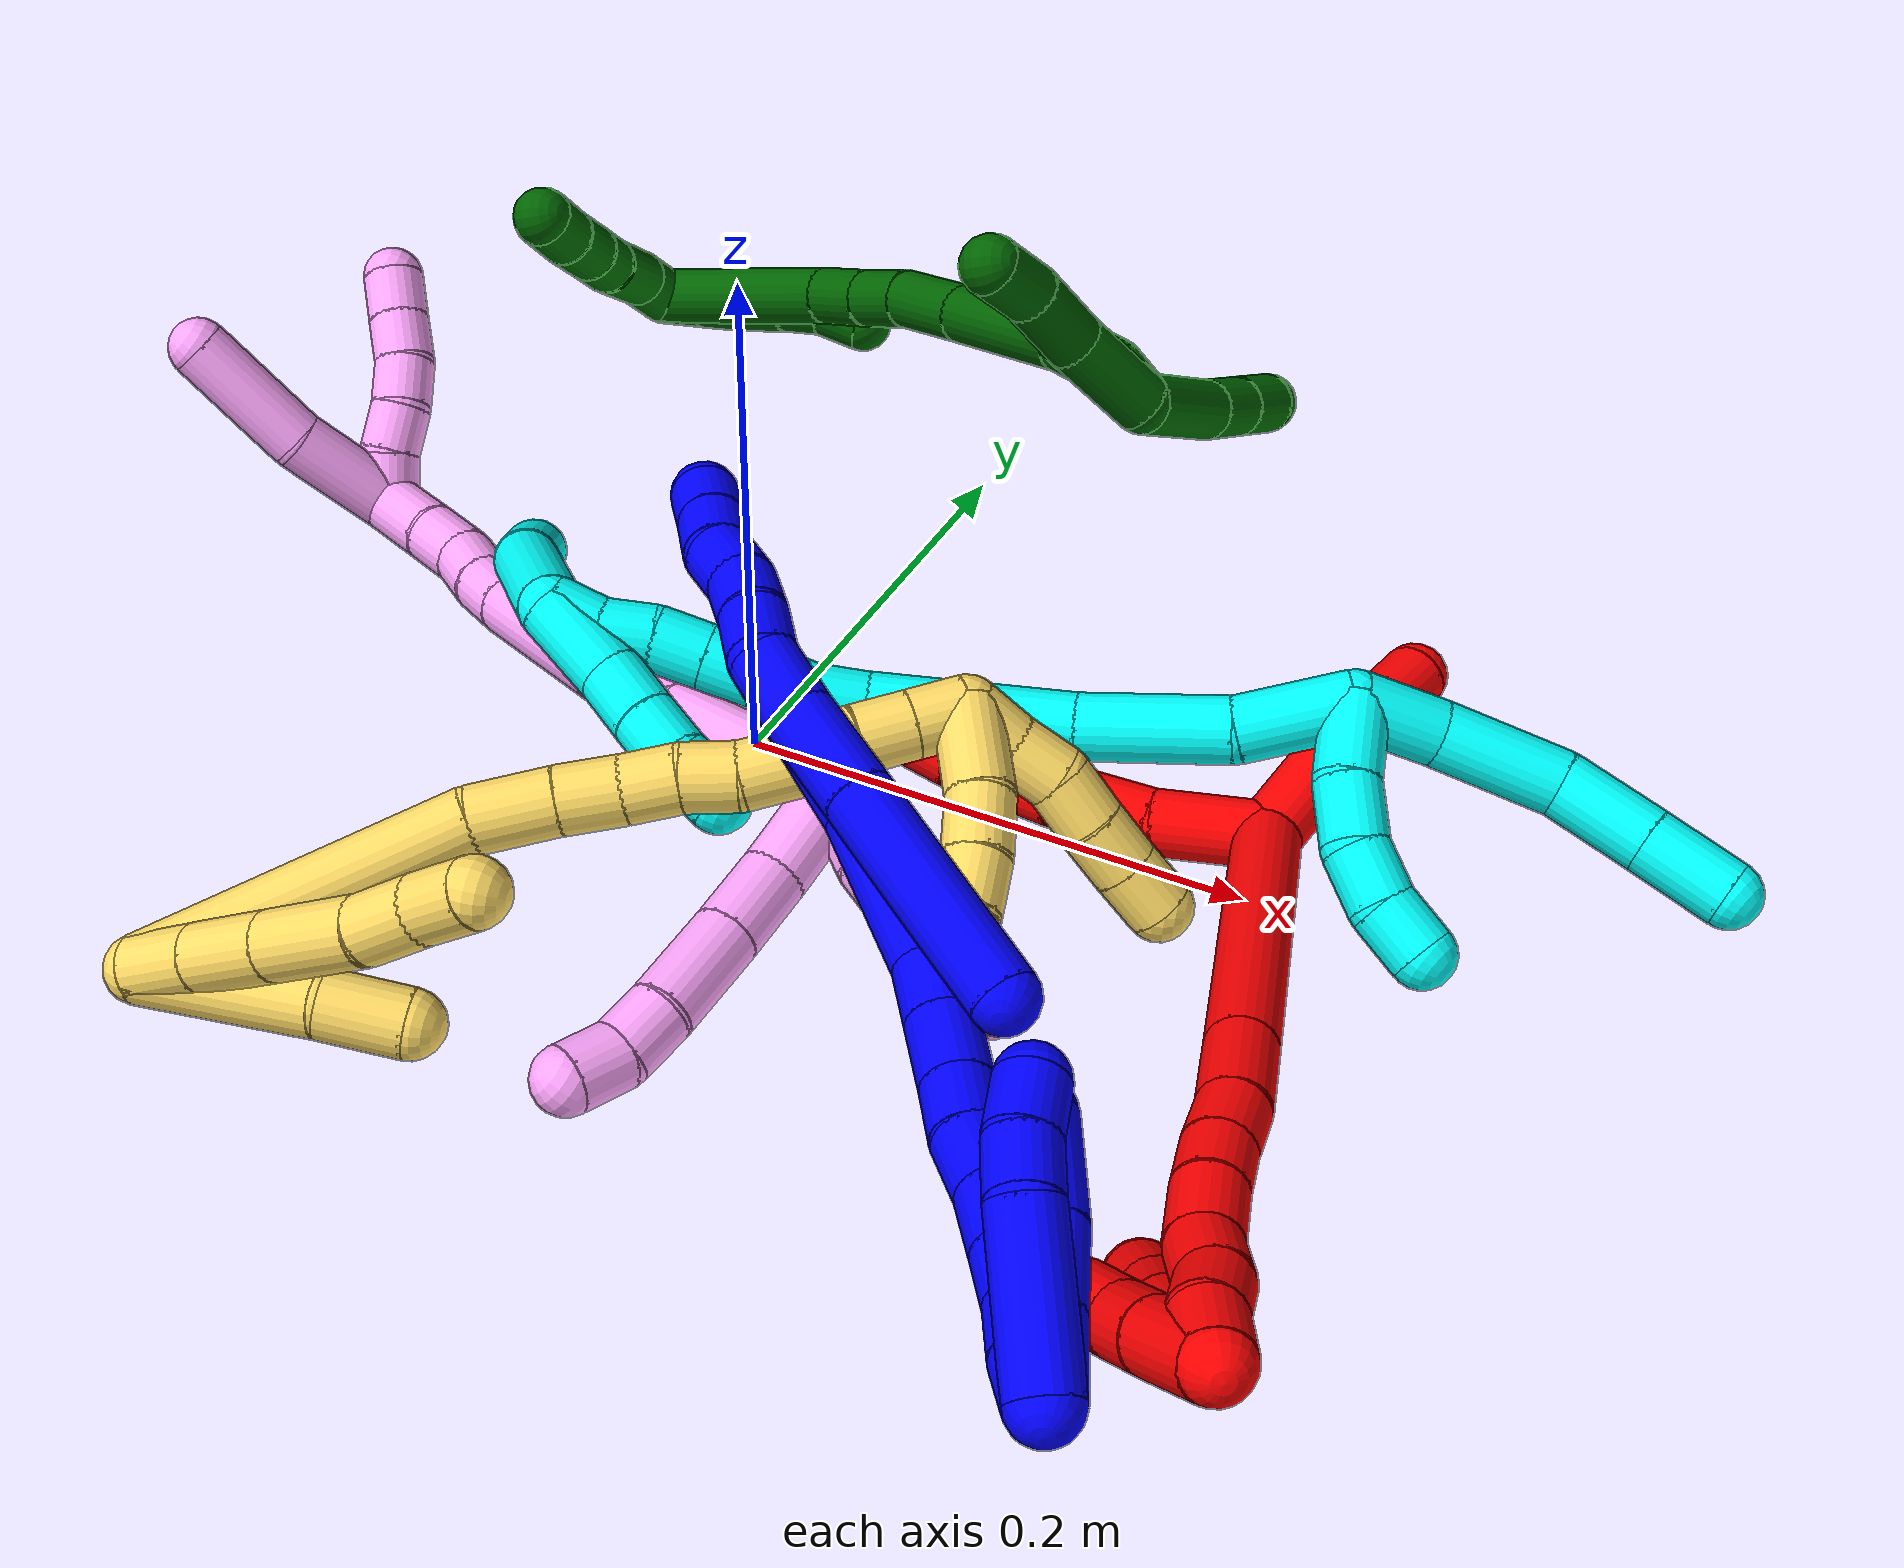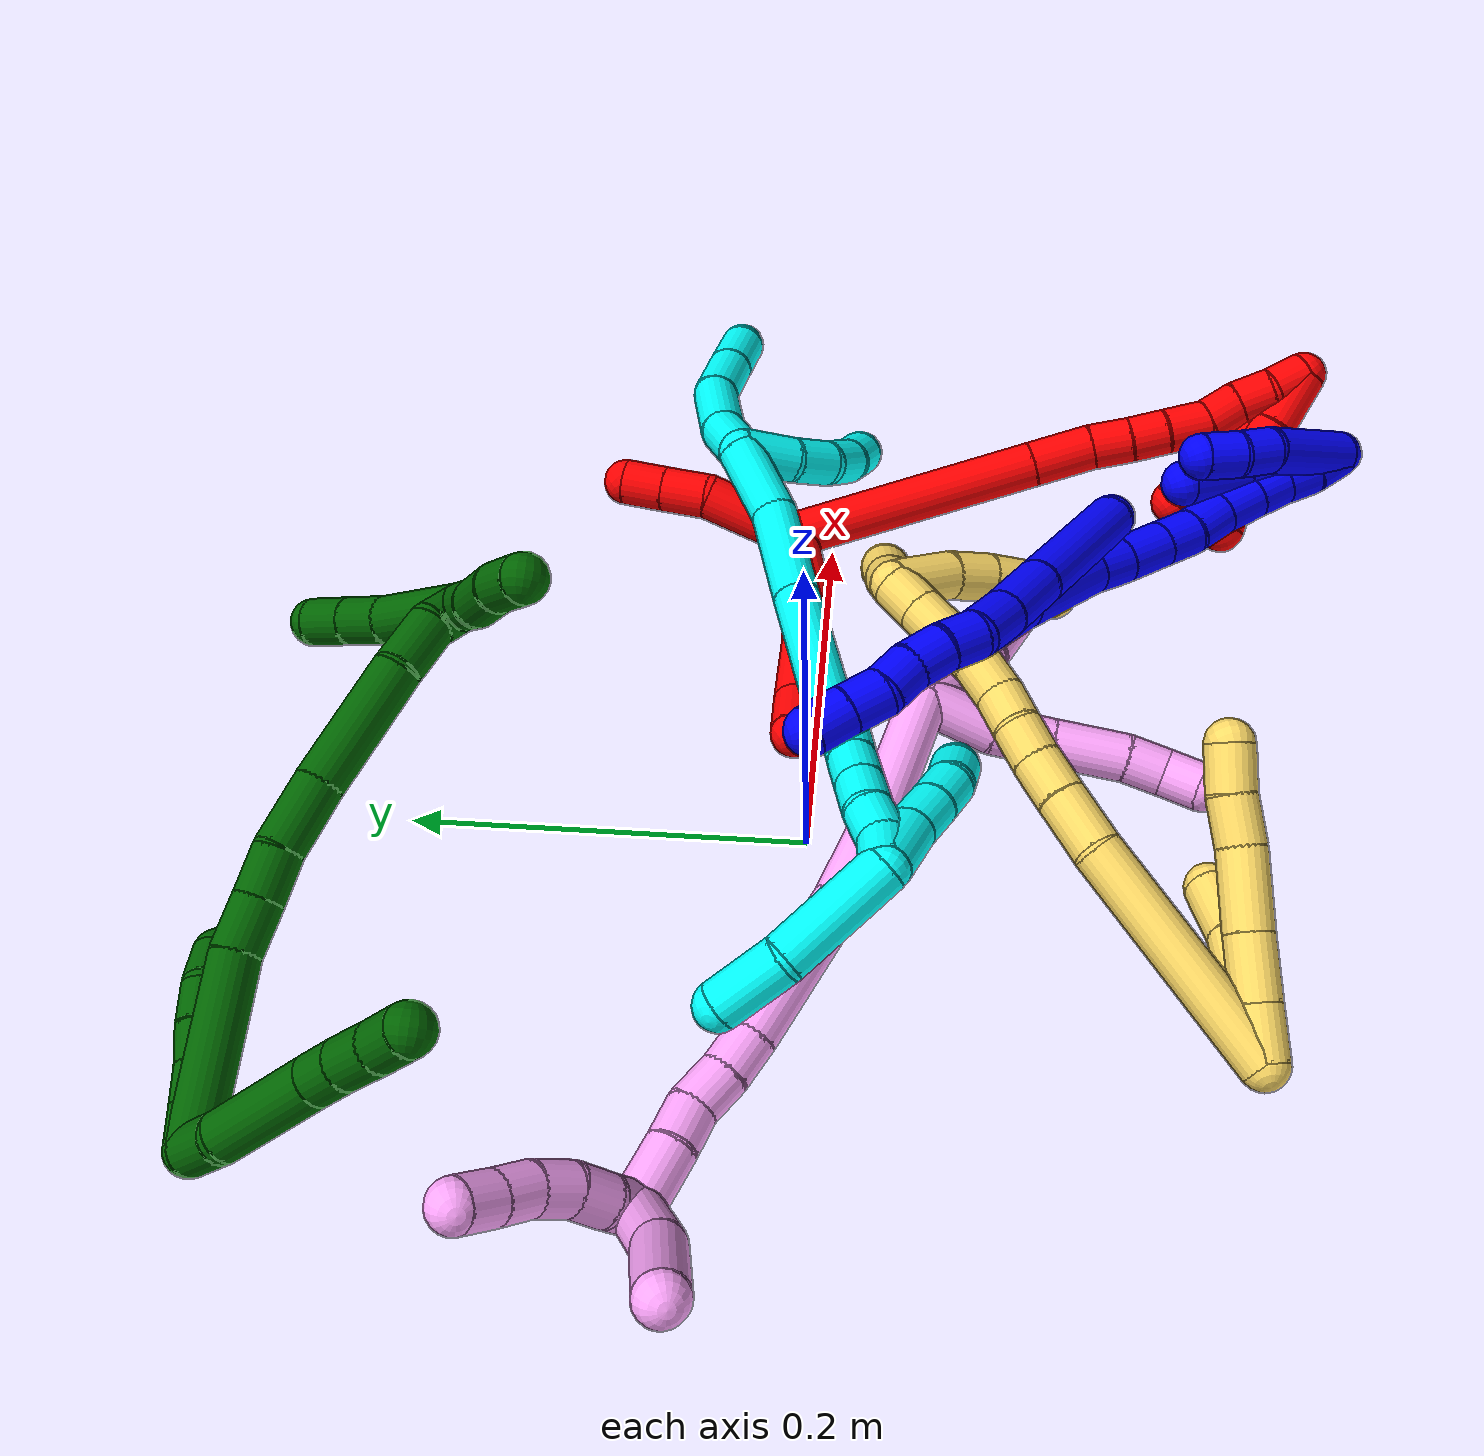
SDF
<sdf version="1.7">
 <world name="default">
  <plugin name="TubeGeneratorPlugin" filename="libtube_generator_plugin.so"/>
  <model name="photoneo_s_sensor">
   <static>1</static>
   <pose>0 0 2 1.57079 1.57079 3.14159</pose>
   <link name="link">
    <inertial><mass>0.1</mass></inertial>
    <sensor name="sensor" type="depth">
     <update_rate>30</update_rate>
     <camera>
      <horizontal_fov>1.22</horizontal_fov>
      <image><width>1920</width><height>1200</height><format>B8G8R8</format></image>
      <clip><near>0.1</near><far>4</far></clip>
      <depth_camera><output>points</output></depth_camera>
     </camera>
     <plugin name="camera_plugin" filename="libgazebo_ros_depth_camera.so">
      <baseline>0.2</baseline>
      <alwaysOn>1</alwaysOn>
      <updateRate>0.0</updateRate>
      <cameraName>camera_ir</cameraName>
      <imageTopicName>/camera/color/image_raw</imageTopicName>
      <cameraInfoTopicName>/camera/color/camera_info</cameraInfoTopicName>
      <depthImageTopicName>/camera/depth/image_raw</depthImageTopicName>
      <depthImageCameraInfoTopicName>/camera/depth/camera_info</depthImageCameraInfoTopicName>
      <pointCloudTopicName>/camera/depth/points</pointCloudTopicName>
      <frameName>fr_optical</frameName>
      <pointCloudCutoff>0.1</pointCloudCutoff>
      <pointCloudCutoffMax>2.0</pointCloudCutoffMax>
      <distortionK1>0</distortionK1>
      <distortionK2>0</distortionK2>
      <distortionK3>0</distortionK3>
      <distortionT1>0</distortionT1>
      <distortionT2>0</distortionT2>
      <CxPrime>0</CxPrime>
      <Cx>0</Cx>
      <Cy>0</Cy>
      <focalLength>0</focalLength>
      <hackBaseline>0</hackBaseline>
     </plugin>
    </sensor>
   </link>
  </model>
  <gravity>0 0 -9.8</gravity>
  <magnetic_field>6e-06 2.3e-05 -4.2e-05</magnetic_field>
  <atmosphere type="adiabatic"/>
  <physics name="default_physics" default="0" type="ode">
   <max_step_size>0.003</max_step_size>
   <real_time_factor>1</real_time_factor>
   <real_time_update_rate>1000</real_time_update_rate>
   <max_contacts>10000</max_contacts>
   <ode>
    <solver>
     <type>quick</type>
     <iters>100</iters>
     <sor>1.3</sor>
     <use_dynamic_moi_rescaling>0</use_dynamic_moi_rescaling>
    </solver>
    <constraints>
     <contact_max_correcting_vel>0</contact_max_correcting_vel>
     <contact_surface_layer>0.001</contact_surface_layer>
     <cfm>0</cfm>
     <erp>0.2</erp>
    </constraints>
   </ode>
  </physics>
  <scene><ambient>0.4 0.4 0.4 1</ambient><background>0.7 0.7 0.7 1</background><shadows>0</shadows></scene>
  <audio><device>default</device></audio>
  <spherical_coordinates>
   <surface_model>EARTH_WGS84</surface_model>
   <latitude_deg>0</latitude_deg>
   <longitude_deg>0</longitude_deg>
   <elevation>0</elevation>
   <heading_deg>0</heading_deg>
  </spherical_coordinates>
  <model name="bin">
   <static>1</static>
   <link name="bottom">
    <collision name="collision-bottom">
     <pose>0 0 -0.01 0 -0 0</pose>
     <geometry><box><size>0.8 0.6 0.02</size></box></geometry>
     <surface>
      <friction><ode><mu>100</mu><mu2>100</mu2></ode></friction>
      <contact><collide_bitmask>65535</collide_bitmask></contact>
     </surface>
    </collision>
   </link>
   <link name="west_wall">
    <collision name="collision-west_wall">
     <pose>-0.41 0 0.1 0 -0 0</pose>
     <geometry><box><size>0.02 0.6 0.2</size></box></geometry>
     <surface>
      <friction><ode><mu>100</mu><mu2>100</mu2></ode></friction>
      <contact><collide_bitmask>65535</collide_bitmask></contact>
     </surface>
    </collision>
   </link>
   <link name="east_wall">
    <collision name="collision-east_wall">
     <pose>0.41 0 0.1 0 -0 0</pose>
     <geometry><box><size>0.02 0.6 0.2</size></box></geometry>
     <surface>
      <friction><ode><mu>100</mu><mu2>100</mu2></ode></friction>
      <contact><collide_bitmask>65535</collide_bitmask></contact>
     </surface>
    </collision>
   </link>
   <link name="south_wall">
    <collision name="collision-south_wall">
     <pose>0 -0.31 0.1 0 -0 0</pose>
     <geometry><box><size>0.8 0.02 0.2</size></box></geometry>
     <surface>
      <friction><ode><mu>100</mu><mu2>100</mu2></ode></friction>
      <contact><collide_bitmask>65535</collide_bitmask></contact>
     </surface>
    </collision>
   </link>
   <link name="north_wall">
    <collision name="collision-north_wall">
     <pose>0 0.31 0.1 0 -0 0</pose>
     <geometry><box><size>0.8 0.02 0.2</size></box></geometry>
     <surface>
      <friction><ode><mu>100</mu><mu2>100</mu2></ode></friction>
      <contact><collide_bitmask>65535</collide_bitmask></contact>
     </surface>
    </collision>
   </link>
  </model>
  <model name="1">
   <static>0</static>
   <link name="1">
    <collision name="collision-cylinder-e_1_2_8">
     <pose>0.007431 -0.004116 0.010105 0.386776 0.597915 0.120565</pose>
     <geometry><cylinder><radius>0.0125</radius><length>0.026403</length></cylinder></geometry>
     <surface>
      <friction><ode><mu>1.16</mu><mu2>1.16</mu2><slip1>0</slip1><slip2>0</slip2></ode></friction>
      <contact><ode><kp>1e+06</kp><kd>1</kd><max_vel>0</max_vel><min_depth>0.001</min_depth></ode></contact>
     </surface>
    </collision>
    <visual name="visual-cylinder-e_1_2_8">
     <pose>0.007431 -0.004116 0.010105 0.386776 0.597915 0.120565</pose>
     <geometry><cylinder><radius>0.0125</radius><length>0.026403</length></cylinder></geometry>
     <material><ambient>0 0 1 1</ambient></material>
    </visual>
    <collision name="collision-cylinder-e_2_8_9">
     <pose>0.026114 -0.013384 0.034146 0.354175 0.648137 0.120086</pose>
     <geometry><cylinder><radius>0.0125</radius><length>0.037274</length></cylinder></geometry>
     <surface>
      <friction><ode><mu>1.16</mu><mu2>1.16</mu2><slip1>0</slip1><slip2>0</slip2></ode></friction>
      <contact><ode><kp>1e+06</kp><kd>1</kd><max_vel>0</max_vel><min_depth>0.001</min_depth></ode></contact>
     </surface>
    </collision>
    <visual name="visual-cylinder-e_2_8_9">
     <pose>0.026114 -0.013384 0.034146 0.354175 0.648137 0.120086</pose>
     <geometry><cylinder><radius>0.0125</radius><length>0.037274</length></cylinder></geometry>
     <material><ambient>0 0 1 1</ambient></material>
    </visual>
    <collision name="collision-cylinder-e_3_9_6">
     <pose>0.063539 -0.031241 0.079964 0.379162 0.651533 0.129457</pose>
     <geometry><cylinder><radius>0.0125</radius><length>0.086323</length></cylinder></geometry>
     <surface>
      <friction><ode><mu>1.16</mu><mu2>1.16</mu2><slip1>0</slip1><slip2>0</slip2></ode></friction>
      <contact><ode><kp>1e+06</kp><kd>1</kd><max_vel>0</max_vel><min_depth>0.001</min_depth></ode></contact>
     </surface>
    </collision>
    <visual name="visual-cylinder-e_3_9_6">
     <pose>0.063539 -0.031241 0.079964 0.379162 0.651533 0.129457</pose>
     <geometry><cylinder><radius>0.0125</radius><length>0.086323</length></cylinder></geometry>
     <material><ambient>0 0 1 1</ambient></material>
    </visual>
    <collision name="collision-cylinder-e_1_2_10">
     <pose>-0.002648 0.001925 -0.009449 -2.94061 -0.268008 1.85721</pose>
     <geometry><cylinder><radius>0.0125</radius><length>0.02</length></cylinder></geometry>
     <surface>
      <friction><ode><mu>1.16</mu><mu2>1.16</mu2><slip1>0</slip1><slip2>0</slip2></ode></friction>
      <contact><ode><kp>1e+06</kp><kd>1</kd><max_vel>0</max_vel><min_depth>0.001</min_depth></ode></contact>
     </surface>
    </collision>
    <visual name="visual-cylinder-e_1_2_10">
     <pose>-0.002648 0.001925 -0.009449 -2.94061 -0.268008 1.85721</pose>
     <geometry><cylinder><radius>0.0125</radius><length>0.02</length></cylinder></geometry>
     <material><ambient>0 0 1 1</ambient></material>
    </visual>
    <collision name="collision-cylinder-e_2_10_11">
     <pose>-0.008397 0.004219 -0.028398 -3.10277 -0.315279 2.89855</pose>
     <geometry><cylinder><radius>0.0125</radius><length>0.02</length></cylinder></geometry>
     <surface>
      <friction><ode><mu>1.16</mu><mu2>1.16</mu2><slip1>0</slip1><slip2>0</slip2></ode></friction>
      <contact><ode><kp>1e+06</kp><kd>1</kd><max_vel>0</max_vel><min_depth>0.001</min_depth></ode></contact>
     </surface>
    </collision>
    <visual name="visual-cylinder-e_2_10_11">
     <pose>-0.008397 0.004219 -0.028398 -3.10277 -0.315279 2.89855</pose>
     <geometry><cylinder><radius>0.0125</radius><length>0.02</length></cylinder></geometry>
     <material><ambient>0 0 1 1</ambient></material>
    </visual>
    <collision name="collision-cylinder-e_3_11_12">
     <pose>-0.016661 0.004837 -0.046458 -3.11252 -0.542545 3.03714</pose>
     <geometry><cylinder><radius>0.0125</radius><length>0.02</length></cylinder></geometry>
     <surface>
      <friction><ode><mu>1.16</mu><mu2>1.16</mu2><slip1>0</slip1><slip2>0</slip2></ode></friction>
      <contact><ode><kp>1e+06</kp><kd>1</kd><max_vel>0</max_vel><min_depth>0.001</min_depth></ode></contact>
     </surface>
    </collision>
    <visual name="visual-cylinder-e_3_11_12">
     <pose>-0.016661 0.004837 -0.046458 -3.11252 -0.542545 3.03714</pose>
     <geometry><cylinder><radius>0.0125</radius><length>0.02</length></cylinder></geometry>
     <material><ambient>0 0 1 1</ambient></material>
    </visual>
    <collision name="collision-cylinder-e_4_12_13">
     <pose>-0.024052 0.005134 -0.064767 -3.13666 -0.224617 3.09786</pose>
     <geometry><cylinder><radius>0.0125</radius><length>0.02</length></cylinder></geometry>
     <surface>
      <friction><ode><mu>1.16</mu><mu2>1.16</mu2><slip1>0</slip1><slip2>0</slip2></ode></friction>
      <contact><ode><kp>1e+06</kp><kd>1</kd><max_vel>0</max_vel><min_depth>0.001</min_depth></ode></contact>
     </surface>
    </collision>
    <visual name="visual-cylinder-e_4_12_13">
     <pose>-0.024052 0.005134 -0.064767 -3.13666 -0.224617 3.09786</pose>
     <geometry><cylinder><radius>0.0125</radius><length>0.02</length></cylinder></geometry>
     <material><ambient>0 0 1 1</ambient></material>
    </visual>
    <collision name="collision-cylinder-e_5_13_5">
     <pose>-0.028784 0.00488 -0.084192 3.11038 -0.253201 -2.89756</pose>
     <geometry><cylinder><radius>0.0125</radius><length>0.02</length></cylinder></geometry>
     <surface>
      <friction><ode><mu>1.16</mu><mu2>1.16</mu2><slip1>0</slip1><slip2>0</slip2></ode></friction>
      <contact><ode><kp>1e+06</kp><kd>1</kd><max_vel>0</max_vel><min_depth>0.001</min_depth></ode></contact>
     </surface>
    </collision>
    <visual name="visual-cylinder-e_5_13_5">
     <pose>-0.028784 0.00488 -0.084192 3.11038 -0.253201 -2.89756</pose>
     <geometry><cylinder><radius>0.0125</radius><length>0.02</length></cylinder></geometry>
     <material><ambient>0 0 1 1</ambient></material>
    </visual>
    <collision name="collision-cylinder-e_1_2_14">
     <pose>0.018681 -0.01611 0.019169 0.6989 0.640971 0.240743</pose>
     <geometry><cylinder><radius>0.0125</radius><length>0.06248</length></cylinder></geometry>
     <surface>
      <friction><ode><mu>1.16</mu><mu2>1.16</mu2><slip1>0</slip1><slip2>0</slip2></ode></friction>
      <contact><ode><kp>1e+06</kp><kd>1</kd><max_vel>0</max_vel><min_depth>0.001</min_depth></ode></contact>
     </surface>
    </collision>
    <visual name="visual-cylinder-e_1_2_14">
     <pose>0.018681 -0.01611 0.019169 0.6989 0.640971 0.240743</pose>
     <geometry><cylinder><radius>0.0125</radius><length>0.06248</length></cylinder></geometry>
     <material><ambient>0 0 1 1</ambient></material>
    </visual>
    <collision name="collision-cylinder-e_2_14_15">
     <pose>0.051216 -0.041942 0.06382 0.364509 0.470013 0.088197</pose>
     <geometry><cylinder><radius>0.0125</radius><length>0.061184</length></cylinder></geometry>
     <surface>
      <friction><ode><mu>1.16</mu><mu2>1.16</mu2><slip1>0</slip1><slip2>0</slip2></ode></friction>
      <contact><ode><kp>1e+06</kp><kd>1</kd><max_vel>0</max_vel><min_depth>0.001</min_depth></ode></contact>
     </surface>
    </collision>
    <visual name="visual-cylinder-e_2_14_15">
     <pose>0.051216 -0.041942 0.06382 0.364509 0.470013 0.088197</pose>
     <geometry><cylinder><radius>0.0125</radius><length>0.061184</length></cylinder></geometry>
     <material><ambient>0 0 1 1</ambient></material>
    </visual>
    <collision name="collision-cylinder-e_3_15_16">
     <pose>0.06807 -0.054457 0.099789 0.260215 0.26962 0.03549</pose>
     <geometry><cylinder><radius>0.0125</radius><length>0.022516</length></cylinder></geometry>
     <surface>
      <friction><ode><mu>1.16</mu><mu2>1.16</mu2><slip1>0</slip1><slip2>0</slip2></ode></friction>
      <contact><ode><kp>1e+06</kp><kd>1</kd><max_vel>0</max_vel><min_depth>0.001</min_depth></ode></contact>
     </surface>
    </collision>
    <visual name="visual-cylinder-e_3_15_16">
     <pose>0.06807 -0.054457 0.099789 0.260215 0.26962 0.03549</pose>
     <geometry><cylinder><radius>0.0125</radius><length>0.022516</length></cylinder></geometry>
     <material><ambient>0 0 1 1</ambient></material>
    </visual>
    <collision name="collision-cylinder-e_4_16_17">
     <pose>0.07436 -0.059198 0.12293 0.152806 0.251549 0.019358</pose>
     <geometry><cylinder><radius>0.0125</radius><length>0.026442</length></cylinder></geometry>
     <surface>
      <friction><ode><mu>1.16</mu><mu2>1.16</mu2><slip1>0</slip1><slip2>0</slip2></ode></friction>
      <contact><ode><kp>1e+06</kp><kd>1</kd><max_vel>0</max_vel><min_depth>0.001</min_depth></ode></contact>
     </surface>
    </collision>
    <visual name="visual-cylinder-e_4_16_17">
     <pose>0.07436 -0.059198 0.12293 0.152806 0.251549 0.019358</pose>
     <geometry><cylinder><radius>0.0125</radius><length>0.026442</length></cylinder></geometry>
     <material><ambient>0 0 1 1</ambient></material>
    </visual>
    <collision name="collision-cylinder-e_5_17_18">
     <pose>0.079908 -0.062223 0.14574 0.105541 0.217644 0.011541</pose>
     <geometry><cylinder><radius>0.0125</radius><length>0.020916</length></cylinder></geometry>
     <surface>
      <friction><ode><mu>1.16</mu><mu2>1.16</mu2><slip1>0</slip1><slip2>0</slip2></ode></friction>
      <contact><ode><kp>1e+06</kp><kd>1</kd><max_vel>0</max_vel><min_depth>0.001</min_depth></ode></contact>
     </surface>
    </collision>
    <visual name="visual-cylinder-e_5_17_18">
     <pose>0.079908 -0.062223 0.14574 0.105541 0.217644 0.011541</pose>
     <geometry><cylinder><radius>0.0125</radius><length>0.020916</length></cylinder></geometry>
     <material><ambient>0 0 1 1</ambient></material>
    </visual>
    <collision name="collision-cylinder-e_6_18_19">
     <pose>0.086527 -0.064084 0.16634 0.075023 0.394426 0.014997</pose>
     <geometry><cylinder><radius>0.0125</radius><length>0.022691</length></cylinder></geometry>
     <surface>
      <friction><ode><mu>1.16</mu><mu2>1.16</mu2><slip1>0</slip1><slip2>0</slip2></ode></friction>
      <contact><ode><kp>1e+06</kp><kd>1</kd><max_vel>0</max_vel><min_depth>0.001</min_depth></ode></contact>
     </surface>
    </collision>
    <visual name="visual-cylinder-e_6_18_19">
     <pose>0.086527 -0.064084 0.16634 0.075023 0.394426 0.014997</pose>
     <geometry><cylinder><radius>0.0125</radius><length>0.022691</length></cylinder></geometry>
     <material><ambient>0 0 1 1</ambient></material>
    </visual>
    <collision name="collision-cylinder-e_7_19_20">
     <pose>0.093907 -0.06555 0.188093 0.060124 0.260551 0.00788</pose>
     <geometry><cylinder><radius>0.0125</radius><length>0.023449</length></cylinder></geometry>
     <surface>
      <friction><ode><mu>1.16</mu><mu2>1.16</mu2><slip1>0</slip1><slip2>0</slip2></ode></friction>
      <contact><ode><kp>1e+06</kp><kd>1</kd><max_vel>0</max_vel><min_depth>0.001</min_depth></ode></contact>
     </surface>
    </collision>
    <visual name="visual-cylinder-e_7_19_20">
     <pose>0.093907 -0.06555 0.188093 0.060124 0.260551 0.00788</pose>
     <geometry><cylinder><radius>0.0125</radius><length>0.023449</length></cylinder></geometry>
     <material><ambient>0 0 1 1</ambient></material>
    </visual>
    <collision name="collision-cylinder-e_8_20_21">
     <pose>0.099413 -0.06675 0.209205 0.052927 0.247977 0.006598</pose>
     <geometry><cylinder><radius>0.0125</radius><length>0.020255</length></cylinder></geometry>
     <surface>
      <friction><ode><mu>1.16</mu><mu2>1.16</mu2><slip1>0</slip1><slip2>0</slip2></ode></friction>
      <contact><ode><kp>1e+06</kp><kd>1</kd><max_vel>0</max_vel><min_depth>0.001</min_depth></ode></contact>
     </surface>
    </collision>
    <visual name="visual-cylinder-e_8_20_21">
     <pose>0.099413 -0.06675 0.209205 0.052927 0.247977 0.006598</pose>
     <geometry><cylinder><radius>0.0125</radius><length>0.020255</length></cylinder></geometry>
     <material><ambient>0 0 1 1</ambient></material>
    </visual>
    <collision name="collision-cylinder-e_9_21_22">
     <pose>0.103174 -0.067763 0.228938 0.049647 0.12761 0.003173</pose>
     <geometry><cylinder><radius>0.0125</radius><length>0.020045</length></cylinder></geometry>
     <surface>
      <friction><ode><mu>1.16</mu><mu2>1.16</mu2><slip1>0</slip1><slip2>0</slip2></ode></friction>
      <contact><ode><kp>1e+06</kp><kd>1</kd><max_vel>0</max_vel><min_depth>0.001</min_depth></ode></contact>
     </surface>
    </collision>
    <visual name="visual-cylinder-e_9_21_22">
     <pose>0.103174 -0.067763 0.228938 0.049647 0.12761 0.003173</pose>
     <geometry><cylinder><radius>0.0125</radius><length>0.020045</length></cylinder></geometry>
     <material><ambient>0 0 1 1</ambient></material>
    </visual>
    <collision name="collision-cylinder-e_10_22_1">
     <pose>0.106772 -0.067044 0.248529 -0.124798 0.234161 -0.014697</pose>
     <geometry><cylinder><radius>0.0125</radius><length>0.020023</length></cylinder></geometry>
     <surface>
      <friction><ode><mu>1.16</mu><mu2>1.16</mu2><slip1>0</slip1><slip2>0</slip2></ode></friction>
      <contact><ode><kp>1e+06</kp><kd>1</kd><max_vel>0</max_vel><min_depth>0.001</min_depth></ode></contact>
     </surface>
    </collision>
    <visual name="visual-cylinder-e_10_22_1">
     <pose>0.106772 -0.067044 0.248529 -0.124798 0.234161 -0.014697</pose>
     <geometry><cylinder><radius>0.0125</radius><length>0.020023</length></cylinder></geometry>
     <material><ambient>0 0 1 1</ambient></material>
    </visual>
    <collision name="collision-cylinder-e_1_1_23">
     <pose>0.108713 -0.064567 0.242925 -3.05897 -0.024965 0.586543</pose>
     <geometry><cylinder><radius>0.0125</radius><length>0.030648</length></cylinder></geometry>
     <surface>
      <friction><ode><mu>1.16</mu><mu2>1.16</mu2><slip1>0</slip1><slip2>0</slip2></ode></friction>
      <contact><ode><kp>1e+06</kp><kd>1</kd><max_vel>0</max_vel><min_depth>0.001</min_depth></ode></contact>
     </surface>
    </collision>
    <visual name="visual-cylinder-e_1_1_23">
     <pose>0.108713 -0.064567 0.242925 -3.05897 -0.024965 0.586543</pose>
     <geometry><cylinder><radius>0.0125</radius><length>0.030648</length></cylinder></geometry>
     <material><ambient>0 0 1 1</ambient></material>
    </visual>
    <collision name="collision-cylinder-e_2_23_24">
     <pose>0.10806 -0.060448 0.212427 -2.95633 -0.017429 0.187069</pose>
     <geometry><cylinder><radius>0.0125</radius><length>0.030997</length></cylinder></geometry>
     <surface>
      <friction><ode><mu>1.16</mu><mu2>1.16</mu2><slip1>0</slip1><slip2>0</slip2></ode></friction>
      <contact><ode><kp>1e+06</kp><kd>1</kd><max_vel>0</max_vel><min_depth>0.001</min_depth></ode></contact>
     </surface>
    </collision>
    <visual name="visual-cylinder-e_2_23_24">
     <pose>0.10806 -0.060448 0.212427 -2.95633 -0.017429 0.187069</pose>
     <geometry><cylinder><radius>0.0125</radius><length>0.030997</length></cylinder></geometry>
     <material><ambient>0 0 1 1</ambient></material>
    </visual>
    <collision name="collision-cylinder-e_3_24_4">
     <pose>0.10526 -0.052521 0.178875 -2.87145 -0.132308 0.90719</pose>
     <geometry><cylinder><radius>0.0125</radius><length>0.038355</length></cylinder></geometry>
     <surface>
      <friction><ode><mu>1.16</mu><mu2>1.16</mu2><slip1>0</slip1><slip2>0</slip2></ode></friction>
      <contact><ode><kp>1e+06</kp><kd>1</kd><max_vel>0</max_vel><min_depth>0.001</min_depth></ode></contact>
     </surface>
    </collision>
    <visual name="visual-cylinder-e_3_24_4">
     <pose>0.10526 -0.052521 0.178875 -2.87145 -0.132308 0.90719</pose>
     <geometry><cylinder><radius>0.0125</radius><length>0.038355</length></cylinder></geometry>
     <material><ambient>0 0 1 1</ambient></material>
    </visual>
    <collision name="collision-cylinder-e_1_1_25">
     <pose>0.104189 -0.051693 0.233256 -2.62579 -0.169499 0.623147</pose>
     <geometry><cylinder><radius>0.0125</radius><length>0.058164</length></cylinder></geometry>
     <surface>
      <friction><ode><mu>1.16</mu><mu2>1.16</mu2><slip1>0</slip1><slip2>0</slip2></ode></friction>
      <contact><ode><kp>1e+06</kp><kd>1</kd><max_vel>0</max_vel><min_depth>0.001</min_depth></ode></contact>
     </surface>
    </collision>
    <visual name="visual-cylinder-e_1_1_25">
     <pose>0.104189 -0.051693 0.233256 -2.62579 -0.169499 0.623147</pose>
     <geometry><cylinder><radius>0.0125</radius><length>0.058164</length></cylinder></geometry>
     <material><ambient>0 0 1 1</ambient></material>
    </visual>
    <collision name="collision-cylinder-e_2_25_26">
     <pose>0.098332 -0.034763 0.198383 -2.86781 -0.091906 0.64439</pose>
     <geometry><cylinder><radius>0.0125</radius><length>0.020732</length></cylinder></geometry>
     <surface>
      <friction><ode><mu>1.16</mu><mu2>1.16</mu2><slip1>0</slip1><slip2>0</slip2></ode></friction>
      <contact><ode><kp>1e+06</kp><kd>1</kd><max_vel>0</max_vel><min_depth>0.001</min_depth></ode></contact>
     </surface>
    </collision>
    <visual name="visual-cylinder-e_2_25_26">
     <pose>0.098332 -0.034763 0.198383 -2.86781 -0.091906 0.64439</pose>
     <geometry><cylinder><radius>0.0125</radius><length>0.020732</length></cylinder></geometry>
     <material><ambient>0 0 1 1</ambient></material>
    </visual>
    <collision name="collision-cylinder-e_3_26_3">
     <pose>0.098358 -0.029948 0.178135 -2.94769 0.092719 -0.890201</pose>
     <geometry><cylinder><radius>0.0125</radius><length>0.021105</length></cylinder></geometry>
     <surface>
      <friction><ode><mu>1.16</mu><mu2>1.16</mu2><slip1>0</slip1><slip2>0</slip2></ode></friction>
      <contact><ode><kp>1e+06</kp><kd>1</kd><max_vel>0</max_vel><min_depth>0.001</min_depth></ode></contact>
     </surface>
    </collision>
    <visual name="visual-cylinder-e_3_26_3">
     <pose>0.098358 -0.029948 0.178135 -2.94769 0.092719 -0.890201</pose>
     <geometry><cylinder><radius>0.0125</radius><length>0.021105</length></cylinder></geometry>
     <material><ambient>0 0 1 1</ambient></material>
    </visual>
    <collision name="collision-sphere-3">
     <pose>0.099335 -0.027923 0.167825 0 -0 0</pose>
     <geometry><sphere><radius>0.0125</radius></sphere></geometry>
     <surface>
      <friction><ode><mu>1.16</mu><mu2>1.16</mu2><slip1>0</slip1><slip2>0</slip2></ode></friction>
      <contact><ode><kp>1e+06</kp><kd>1</kd><max_vel>0</max_vel><min_depth>0.001</min_depth></ode></contact>
     </surface>
    </collision>
    <visual name="visual-sphere-3">
     <pose>0.099335 -0.027923 0.167825 0 -0 0</pose>
     <geometry><sphere><radius>0.0125</radius></sphere></geometry>
     <material><ambient>0 0 1 1</ambient></material>
    </visual>
    <collision name="collision-sphere-26">
     <pose>0.097381 -0.031973 0.188445 0 -0 0</pose>
     <geometry><sphere><radius>0.0125</radius></sphere></geometry>
     <surface>
      <friction><ode><mu>1.16</mu><mu2>1.16</mu2><slip1>0</slip1><slip2>0</slip2></ode></friction>
      <contact><ode><kp>1e+06</kp><kd>1</kd><max_vel>0</max_vel><min_depth>0.001</min_depth></ode></contact>
     </surface>
    </collision>
    <visual name="visual-sphere-26">
     <pose>0.097381 -0.031973 0.188445 0 -0 0</pose>
     <geometry><sphere><radius>0.0125</radius></sphere></geometry>
     <material><ambient>0 0 1 1</ambient></material>
    </visual>
    <collision name="collision-sphere-25">
     <pose>0.099284 -0.037554 0.20832 0 -0 0</pose>
     <geometry><sphere><radius>0.0125</radius></sphere></geometry>
     <surface>
      <friction><ode><mu>1.16</mu><mu2>1.16</mu2><slip1>0</slip1><slip2>0</slip2></ode></friction>
      <contact><ode><kp>1e+06</kp><kd>1</kd><max_vel>0</max_vel><min_depth>0.001</min_depth></ode></contact>
     </surface>
    </collision>
    <visual name="visual-sphere-25">
     <pose>0.099284 -0.037554 0.20832 0 -0 0</pose>
     <geometry><sphere><radius>0.0125</radius></sphere></geometry>
     <material><ambient>0 0 1 1</ambient></material>
    </visual>
    <collision name="collision-sphere-4">
     <pose>0.10273 -0.047448 0.160555 0 -0 0</pose>
     <geometry><sphere><radius>0.0125</radius></sphere></geometry>
     <surface>
      <friction><ode><mu>1.16</mu><mu2>1.16</mu2><slip1>0</slip1><slip2>0</slip2></ode></friction>
      <contact><ode><kp>1e+06</kp><kd>1</kd><max_vel>0</max_vel><min_depth>0.001</min_depth></ode></contact>
     </surface>
    </collision>
    <visual name="visual-sphere-4">
     <pose>0.10273 -0.047448 0.160555 0 -0 0</pose>
     <geometry><sphere><radius>0.0125</radius></sphere></geometry>
     <material><ambient>0 0 1 1</ambient></material>
    </visual>
    <collision name="collision-sphere-24">
     <pose>0.10779 -0.057594 0.197196 0 -0 0</pose>
     <geometry><sphere><radius>0.0125</radius></sphere></geometry>
     <surface>
      <friction><ode><mu>1.16</mu><mu2>1.16</mu2><slip1>0</slip1><slip2>0</slip2></ode></friction>
      <contact><ode><kp>1e+06</kp><kd>1</kd><max_vel>0</max_vel><min_depth>0.001</min_depth></ode></contact>
     </surface>
    </collision>
    <visual name="visual-sphere-24">
     <pose>0.10779 -0.057594 0.197196 0 -0 0</pose>
     <geometry><sphere><radius>0.0125</radius></sphere></geometry>
     <material><ambient>0 0 1 1</ambient></material>
    </visual>
    <collision name="collision-sphere-23">
     <pose>0.10833 -0.063303 0.227658 0 -0 0</pose>
     <geometry><sphere><radius>0.0125</radius></sphere></geometry>
     <surface>
      <friction><ode><mu>1.16</mu><mu2>1.16</mu2><slip1>0</slip1><slip2>0</slip2></ode></friction>
      <contact><ode><kp>1e+06</kp><kd>1</kd><max_vel>0</max_vel><min_depth>0.001</min_depth></ode></contact>
     </surface>
    </collision>
    <visual name="visual-sphere-23">
     <pose>0.10833 -0.063303 0.227658 0 -0 0</pose>
     <geometry><sphere><radius>0.0125</radius></sphere></geometry>
     <material><ambient>0 0 1 1</ambient></material>
    </visual>
    <collision name="collision-sphere-1">
     <pose>0.109095 -0.065832 0.258192 0 -0 0</pose>
     <geometry><sphere><radius>0.0125</radius></sphere></geometry>
     <surface>
      <friction><ode><mu>1.16</mu><mu2>1.16</mu2><slip1>0</slip1><slip2>0</slip2></ode></friction>
      <contact><ode><kp>1e+06</kp><kd>1</kd><max_vel>0</max_vel><min_depth>0.001</min_depth></ode></contact>
     </surface>
    </collision>
    <visual name="visual-sphere-1">
     <pose>0.109095 -0.065832 0.258192 0 -0 0</pose>
     <geometry><sphere><radius>0.0125</radius></sphere></geometry>
     <material><ambient>0 0 1 1</ambient></material>
    </visual>
    <collision name="collision-sphere-22">
     <pose>0.104449 -0.068256 0.238867 0 -0 0</pose>
     <geometry><sphere><radius>0.0125</radius></sphere></geometry>
     <surface>
      <friction><ode><mu>1.16</mu><mu2>1.16</mu2><slip1>0</slip1><slip2>0</slip2></ode></friction>
      <contact><ode><kp>1e+06</kp><kd>1</kd><max_vel>0</max_vel><min_depth>0.001</min_depth></ode></contact>
     </surface>
    </collision>
    <visual name="visual-sphere-22">
     <pose>0.104449 -0.068256 0.238867 0 -0 0</pose>
     <geometry><sphere><radius>0.0125</radius></sphere></geometry>
     <material><ambient>0 0 1 1</ambient></material>
    </visual>
    <collision name="collision-sphere-21">
     <pose>0.101898 -0.067269 0.219009 0 -0 0</pose>
     <geometry><sphere><radius>0.0125</radius></sphere></geometry>
     <surface>
      <friction><ode><mu>1.16</mu><mu2>1.16</mu2><slip1>0</slip1><slip2>0</slip2></ode></friction>
      <contact><ode><kp>1e+06</kp><kd>1</kd><max_vel>0</max_vel><min_depth>0.001</min_depth></ode></contact>
     </surface>
    </collision>
    <visual name="visual-sphere-21">
     <pose>0.101898 -0.067269 0.219009 0 -0 0</pose>
     <geometry><sphere><radius>0.0125</radius></sphere></geometry>
     <material><ambient>0 0 1 1</ambient></material>
    </visual>
    <collision name="collision-sphere-11">
     <pose>-0.011498 0.004588 -0.037898 0 -0 0</pose>
     <geometry><sphere><radius>0.0125</radius></sphere></geometry>
     <surface>
      <friction><ode><mu>1.16</mu><mu2>1.16</mu2><slip1>0</slip1><slip2>0</slip2></ode></friction>
      <contact><ode><kp>1e+06</kp><kd>1</kd><max_vel>0</max_vel><min_depth>0.001</min_depth></ode></contact>
     </surface>
    </collision>
    <visual name="visual-sphere-11">
     <pose>-0.011498 0.004588 -0.037898 0 -0 0</pose>
     <geometry><sphere><radius>0.0125</radius></sphere></geometry>
     <material><ambient>0 0 1 1</ambient></material>
    </visual>
    <collision name="collision-sphere-10">
     <pose>-0.005296 0.00385 -0.018898 0 -0 0</pose>
     <geometry><sphere><radius>0.0125</radius></sphere></geometry>
     <surface>
      <friction><ode><mu>1.16</mu><mu2>1.16</mu2><slip1>0</slip1><slip2>0</slip2></ode></friction>
      <contact><ode><kp>1e+06</kp><kd>1</kd><max_vel>0</max_vel><min_depth>0.001</min_depth></ode></contact>
     </surface>
    </collision>
    <visual name="visual-sphere-10">
     <pose>-0.005296 0.00385 -0.018898 0 -0 0</pose>
     <geometry><sphere><radius>0.0125</radius></sphere></geometry>
     <material><ambient>0 0 1 1</ambient></material>
    </visual>
    <collision name="collision-sphere-6">
     <pose>0.089712 -0.043944 0.111846 0 -0 0</pose>
     <geometry><sphere><radius>0.0125</radius></sphere></geometry>
     <surface>
      <friction><ode><mu>1.16</mu><mu2>1.16</mu2><slip1>0</slip1><slip2>0</slip2></ode></friction>
      <contact><ode><kp>1e+06</kp><kd>1</kd><max_vel>0</max_vel><min_depth>0.001</min_depth></ode></contact>
     </surface>
    </collision>
    <visual name="visual-sphere-6">
     <pose>0.089712 -0.043944 0.111846 0 -0 0</pose>
     <geometry><sphere><radius>0.0125</radius></sphere></geometry>
     <material><ambient>0 0 1 1</ambient></material>
    </visual>
    <collision name="collision-sphere-9">
     <pose>0.037365 -0.018537 0.048081 0 -0 0</pose>
     <geometry><sphere><radius>0.0125</radius></sphere></geometry>
     <surface>
      <friction><ode><mu>1.16</mu><mu2>1.16</mu2><slip1>0</slip1><slip2>0</slip2></ode></friction>
      <contact><ode><kp>1e+06</kp><kd>1</kd><max_vel>0</max_vel><min_depth>0.001</min_depth></ode></contact>
     </surface>
    </collision>
    <visual name="visual-sphere-9">
     <pose>0.037365 -0.018537 0.048081 0 -0 0</pose>
     <geometry><sphere><radius>0.0125</radius></sphere></geometry>
     <material><ambient>0 0 1 1</ambient></material>
    </visual>
    <collision name="collision-sphere-2">
     <geometry><sphere><radius>0.0125</radius></sphere></geometry>
     <surface>
      <friction><ode><mu>1.16</mu><mu2>1.16</mu2><slip1>0</slip1><slip2>0</slip2></ode></friction>
      <contact><ode><kp>1e+06</kp><kd>1</kd><max_vel>0</max_vel><min_depth>0.001</min_depth></ode></contact>
     </surface>
    </collision>
    <visual name="visual-sphere-2">
     <geometry><sphere><radius>0.0125</radius></sphere></geometry>
     <material><ambient>0 0 1 1</ambient></material>
    </visual>
    <collision name="collision-sphere-19">
     <pose>0.090886 -0.064869 0.176785 0 -0 0</pose>
     <geometry><sphere><radius>0.0125</radius></sphere></geometry>
     <surface>
      <friction><ode><mu>1.16</mu><mu2>1.16</mu2><slip1>0</slip1><slip2>0</slip2></ode></friction>
      <contact><ode><kp>1e+06</kp><kd>1</kd><max_vel>0</max_vel><min_depth>0.001</min_depth></ode></contact>
     </surface>
    </collision>
    <visual name="visual-sphere-19">
     <pose>0.090886 -0.064869 0.176785 0 -0 0</pose>
     <geometry><sphere><radius>0.0125</radius></sphere></geometry>
     <material><ambient>0 0 1 1</ambient></material>
    </visual>
    <collision name="collision-sphere-8">
     <pose>0.014863 -0.008232 0.02021 0 -0 0</pose>
     <geometry><sphere><radius>0.0125</radius></sphere></geometry>
     <surface>
      <friction><ode><mu>1.16</mu><mu2>1.16</mu2><slip1>0</slip1><slip2>0</slip2></ode></friction>
      <contact><ode><kp>1e+06</kp><kd>1</kd><max_vel>0</max_vel><min_depth>0.001</min_depth></ode></contact>
     </surface>
    </collision>
    <visual name="visual-sphere-8">
     <pose>0.014863 -0.008232 0.02021 0 -0 0</pose>
     <geometry><sphere><radius>0.0125</radius></sphere></geometry>
     <material><ambient>0 0 1 1</ambient></material>
    </visual>
    <collision name="collision-sphere-12">
     <pose>-0.021824 0.005086 -0.055018 0 -0 0</pose>
     <geometry><sphere><radius>0.0125</radius></sphere></geometry>
     <surface>
      <friction><ode><mu>1.16</mu><mu2>1.16</mu2><slip1>0</slip1><slip2>0</slip2></ode></friction>
      <contact><ode><kp>1e+06</kp><kd>1</kd><max_vel>0</max_vel><min_depth>0.001</min_depth></ode></contact>
     </surface>
    </collision>
    <visual name="visual-sphere-12">
     <pose>-0.021824 0.005086 -0.055018 0 -0 0</pose>
     <geometry><sphere><radius>0.0125</radius></sphere></geometry>
     <material><ambient>0 0 1 1</ambient></material>
    </visual>
    <collision name="collision-sphere-13">
     <pose>-0.026279 0.005182 -0.074516 0 -0 0</pose>
     <geometry><sphere><radius>0.0125</radius></sphere></geometry>
     <surface>
      <friction><ode><mu>1.16</mu><mu2>1.16</mu2><slip1>0</slip1><slip2>0</slip2></ode></friction>
      <contact><ode><kp>1e+06</kp><kd>1</kd><max_vel>0</max_vel><min_depth>0.001</min_depth></ode></contact>
     </surface>
    </collision>
    <visual name="visual-sphere-13">
     <pose>-0.026279 0.005182 -0.074516 0 -0 0</pose>
     <geometry><sphere><radius>0.0125</radius></sphere></geometry>
     <material><ambient>0 0 1 1</ambient></material>
    </visual>
    <collision name="collision-sphere-5">
     <pose>-0.031289 0.004578 -0.093869 0 -0 0</pose>
     <geometry><sphere><radius>0.0125</radius></sphere></geometry>
     <surface>
      <friction><ode><mu>1.16</mu><mu2>1.16</mu2><slip1>0</slip1><slip2>0</slip2></ode></friction>
      <contact><ode><kp>1e+06</kp><kd>1</kd><max_vel>0</max_vel><min_depth>0.001</min_depth></ode></contact>
     </surface>
    </collision>
    <visual name="visual-sphere-5">
     <pose>-0.031289 0.004578 -0.093869 0 -0 0</pose>
     <geometry><sphere><radius>0.0125</radius></sphere></geometry>
     <material><ambient>0 0 1 1</ambient></material>
    </visual>
    <collision name="collision-sphere-14">
     <pose>0.037361 -0.032219 0.038338 0 -0 0</pose>
     <geometry><sphere><radius>0.0125</radius></sphere></geometry>
     <surface>
      <friction><ode><mu>1.16</mu><mu2>1.16</mu2><slip1>0</slip1><slip2>0</slip2></ode></friction>
      <contact><ode><kp>1e+06</kp><kd>1</kd><max_vel>0</max_vel><min_depth>0.001</min_depth></ode></contact>
     </surface>
    </collision>
    <visual name="visual-sphere-14">
     <pose>0.037361 -0.032219 0.038338 0 -0 0</pose>
     <geometry><sphere><radius>0.0125</radius></sphere></geometry>
     <material><ambient>0 0 1 1</ambient></material>
    </visual>
    <collision name="collision-sphere-15">
     <pose>0.065071 -0.051666 0.089303 0 -0 0</pose>
     <geometry><sphere><radius>0.0125</radius></sphere></geometry>
     <surface>
      <friction><ode><mu>1.16</mu><mu2>1.16</mu2><slip1>0</slip1><slip2>0</slip2></ode></friction>
      <contact><ode><kp>1e+06</kp><kd>1</kd><max_vel>0</max_vel><min_depth>0.001</min_depth></ode></contact>
     </surface>
    </collision>
    <visual name="visual-sphere-15">
     <pose>0.065071 -0.051666 0.089303 0 -0 0</pose>
     <geometry><sphere><radius>0.0125</radius></sphere></geometry>
     <material><ambient>0 0 1 1</ambient></material>
    </visual>
    <collision name="collision-sphere-16">
     <pose>0.071069 -0.057249 0.110275 0 -0 0</pose>
     <geometry><sphere><radius>0.0125</radius></sphere></geometry>
     <surface>
      <friction><ode><mu>1.16</mu><mu2>1.16</mu2><slip1>0</slip1><slip2>0</slip2></ode></friction>
      <contact><ode><kp>1e+06</kp><kd>1</kd><max_vel>0</max_vel><min_depth>0.001</min_depth></ode></contact>
     </surface>
    </collision>
    <visual name="visual-sphere-16">
     <pose>0.071069 -0.057249 0.110275 0 -0 0</pose>
     <geometry><sphere><radius>0.0125</radius></sphere></geometry>
     <material><ambient>0 0 1 1</ambient></material>
    </visual>
    <collision name="collision-sphere-17">
     <pose>0.07765 -0.061147 0.135586 0 -0 0</pose>
     <geometry><sphere><radius>0.0125</radius></sphere></geometry>
     <surface>
      <friction><ode><mu>1.16</mu><mu2>1.16</mu2><slip1>0</slip1><slip2>0</slip2></ode></friction>
      <contact><ode><kp>1e+06</kp><kd>1</kd><max_vel>0</max_vel><min_depth>0.001</min_depth></ode></contact>
     </surface>
    </collision>
    <visual name="visual-sphere-17">
     <pose>0.07765 -0.061147 0.135586 0 -0 0</pose>
     <geometry><sphere><radius>0.0125</radius></sphere></geometry>
     <material><ambient>0 0 1 1</ambient></material>
    </visual>
    <collision name="collision-sphere-18">
     <pose>0.082167 -0.063299 0.155895 0 -0 0</pose>
     <geometry><sphere><radius>0.0125</radius></sphere></geometry>
     <surface>
      <friction><ode><mu>1.16</mu><mu2>1.16</mu2><slip1>0</slip1><slip2>0</slip2></ode></friction>
      <contact><ode><kp>1e+06</kp><kd>1</kd><max_vel>0</max_vel><min_depth>0.001</min_depth></ode></contact>
     </surface>
    </collision>
    <visual name="visual-sphere-18">
     <pose>0.082167 -0.063299 0.155895 0 -0 0</pose>
     <geometry><sphere><radius>0.0125</radius></sphere></geometry>
     <material><ambient>0 0 1 1</ambient></material>
    </visual>
    <collision name="collision-sphere-20">
     <pose>0.096927 -0.06623 0.199401 0 -0 0</pose>
     <geometry><sphere><radius>0.0125</radius></sphere></geometry>
     <surface>
      <friction><ode><mu>1.16</mu><mu2>1.16</mu2><slip1>0</slip1><slip2>0</slip2></ode></friction>
      <contact><ode><kp>1e+06</kp><kd>1</kd><max_vel>0</max_vel><min_depth>0.001</min_depth></ode></contact>
     </surface>
    </collision>
    <visual name="visual-sphere-20">
     <pose>0.096927 -0.06623 0.199401 0 -0 0</pose>
     <geometry><sphere><radius>0.0125</radius></sphere></geometry>
     <material><ambient>0 0 1 1</ambient></material>
    </visual>
    <inertial>
     <pose>0.061057 -0.037094 0.10899 0 -0 0</pose>
     <mass>0.75</mass>
     <inertia>
      <ixx>0.000168</ixx>
      <ixy>0</ixy>
      <ixz>0</ixz>
      <iyy>0.000126</iyy>
      <iyz>0</iyz>
      <izz>-2.7e-05</izz>
     </inertia>
    </inertial>
   </link>
   <pose>0.049988 -0.077473 0.108602 1.52521 0.056731 0.398631</pose>
  </model>
  <model name="2">
   <static>0</static>
   <link name="2">
    <collision name="collision-cylinder-e_1_2_8">
     <pose>-0.017169 -0.009959 -0.006948 2.17993 -0.955213 -1.56291</pose>
     <geometry><cylinder><radius>0.0125</radius><length>0.042058</length></cylinder></geometry>
     <surface>
      <friction><ode><mu>1.16</mu><mu2>1.16</mu2><slip1>0</slip1><slip2>0</slip2></ode></friction>
      <contact><ode><kp>1e+06</kp><kd>1</kd><max_vel>0</max_vel><min_depth>0.001</min_depth></ode></contact>
     </surface>
    </collision>
    <visual name="visual-cylinder-e_1_2_8">
     <pose>-0.017169 -0.009959 -0.006948 2.17993 -0.955213 -1.56291</pose>
     <geometry><cylinder><radius>0.0125</radius><length>0.042058</length></cylinder></geometry>
     <material><ambient>1 0 0 1</ambient></material>
    </visual>
    <collision name="collision-cylinder-e_2_8_9">
     <pose>-0.049399 -0.026262 -0.023231 2.54471 -0.927634 -2.03885</pose>
     <geometry><cylinder><radius>0.0125</radius><length>0.037644</length></cylinder></geometry>
     <surface>
      <friction><ode><mu>1.16</mu><mu2>1.16</mu2><slip1>0</slip1><slip2>0</slip2></ode></friction>
      <contact><ode><kp>1e+06</kp><kd>1</kd><max_vel>0</max_vel><min_depth>0.001</min_depth></ode></contact>
     </surface>
    </collision>
    <visual name="visual-cylinder-e_2_8_9">
     <pose>-0.049399 -0.026262 -0.023231 2.54471 -0.927634 -2.03885</pose>
     <geometry><cylinder><radius>0.0125</radius><length>0.037644</length></cylinder></geometry>
     <material><ambient>1 0 0 1</ambient></material>
    </visual>
    <collision name="collision-cylinder-e_3_9_10">
     <pose>-0.081678 -0.038114 -0.043407 2.67152 -0.955991 -2.27564</pose>
     <geometry><cylinder><radius>0.0125</radius><length>0.042156</length></cylinder></geometry>
     <surface>
      <friction><ode><mu>1.16</mu><mu2>1.16</mu2><slip1>0</slip1><slip2>0</slip2></ode></friction>
      <contact><ode><kp>1e+06</kp><kd>1</kd><max_vel>0</max_vel><min_depth>0.001</min_depth></ode></contact>
     </surface>
    </collision>
    <visual name="visual-cylinder-e_3_9_10">
     <pose>-0.081678 -0.038114 -0.043407 2.67152 -0.955991 -2.27564</pose>
     <geometry><cylinder><radius>0.0125</radius><length>0.042156</length></cylinder></geometry>
     <material><ambient>1 0 0 1</ambient></material>
    </visual>
    <collision name="collision-cylinder-e_4_10_6">
     <pose>-0.111747 -0.04522 -0.059752 2.85895 -1.15108 -2.70988</pose>
     <geometry><cylinder><radius>0.0125</radius><length>0.028143</length></cylinder></geometry>
     <surface>
      <friction><ode><mu>1.16</mu><mu2>1.16</mu2><slip1>0</slip1><slip2>0</slip2></ode></friction>
      <contact><ode><kp>1e+06</kp><kd>1</kd><max_vel>0</max_vel><min_depth>0.001</min_depth></ode></contact>
     </surface>
    </collision>
    <visual name="visual-cylinder-e_4_10_6">
     <pose>-0.111747 -0.04522 -0.059752 2.85895 -1.15108 -2.70988</pose>
     <geometry><cylinder><radius>0.0125</radius><length>0.028143</length></cylinder></geometry>
     <material><ambient>1 0 0 1</ambient></material>
    </visual>
    <collision name="collision-cylinder-e_1_2_11">
     <pose>0.007398 0.021413 -0.013169 -2.12217 0.286201 -0.504549</pose>
     <geometry><cylinder><radius>0.0125</radius><length>0.052408</length></cylinder></geometry>
     <surface>
      <friction><ode><mu>1.16</mu><mu2>1.16</mu2><slip1>0</slip1><slip2>0</slip2></ode></friction>
      <contact><ode><kp>1e+06</kp><kd>1</kd><max_vel>0</max_vel><min_depth>0.001</min_depth></ode></contact>
     </surface>
    </collision>
    <visual name="visual-cylinder-e_1_2_11">
     <pose>0.007398 0.021413 -0.013169 -2.12217 0.286201 -0.504549</pose>
     <geometry><cylinder><radius>0.0125</radius><length>0.052408</length></cylinder></geometry>
     <material><ambient>1 0 0 1</ambient></material>
    </visual>
    <collision name="collision-cylinder-e_2_11_12">
     <pose>0.020225 0.050322 -0.034708 -2.41121 0.450101 -1.07901</pose>
     <geometry><cylinder><radius>0.0125</radius><length>0.02496</length></cylinder></geometry>
     <surface>
      <friction><ode><mu>1.16</mu><mu2>1.16</mu2><slip1>0</slip1><slip2>0</slip2></ode></friction>
      <contact><ode><kp>1e+06</kp><kd>1</kd><max_vel>0</max_vel><min_depth>0.001</min_depth></ode></contact>
     </surface>
    </collision>
    <visual name="visual-cylinder-e_2_11_12">
     <pose>0.020225 0.050322 -0.034708 -2.41121 0.450101 -1.07901</pose>
     <geometry><cylinder><radius>0.0125</radius><length>0.02496</length></cylinder></geometry>
     <material><ambient>1 0 0 1</ambient></material>
    </visual>
    <collision name="collision-cylinder-e_3_12_5">
     <pose>0.030534 0.064727 -0.050597 -2.39851 0.44585 -1.05386</pose>
     <geometry><cylinder><radius>0.0125</radius><length>0.022632</length></cylinder></geometry>
     <surface>
      <friction><ode><mu>1.16</mu><mu2>1.16</mu2><slip1>0</slip1><slip2>0</slip2></ode></friction>
      <contact><ode><kp>1e+06</kp><kd>1</kd><max_vel>0</max_vel><min_depth>0.001</min_depth></ode></contact>
     </surface>
    </collision>
    <visual name="visual-cylinder-e_3_12_5">
     <pose>0.030534 0.064727 -0.050597 -2.39851 0.44585 -1.05386</pose>
     <geometry><cylinder><radius>0.0125</radius><length>0.022632</length></cylinder></geometry>
     <material><ambient>1 0 0 1</ambient></material>
    </visual>
    <collision name="collision-cylinder-e_1_2_13">
     <pose>-0.008806 -0.021321 0.065216 0.315979 -0.127643 -0.020363</pose>
     <geometry><cylinder><radius>0.0125</radius><length>0.138352</length></cylinder></geometry>
     <surface>
      <friction><ode><mu>1.16</mu><mu2>1.16</mu2><slip1>0</slip1><slip2>0</slip2></ode></friction>
      <contact><ode><kp>1e+06</kp><kd>1</kd><max_vel>0</max_vel><min_depth>0.001</min_depth></ode></contact>
     </surface>
    </collision>
    <visual name="visual-cylinder-e_1_2_13">
     <pose>-0.008806 -0.021321 0.065216 0.315979 -0.127643 -0.020363</pose>
     <geometry><cylinder><radius>0.0125</radius><length>0.138352</length></cylinder></geometry>
     <material><ambient>1 0 0 1</ambient></material>
    </visual>
    <collision name="collision-cylinder-e_2_13_14">
     <pose>-0.019848 -0.047941 0.146625 0.316258 -0.130522 -0.020842</pose>
     <geometry><cylinder><radius>0.0125</radius><length>0.034367</length></cylinder></geometry>
     <surface>
      <friction><ode><mu>1.16</mu><mu2>1.16</mu2><slip1>0</slip1><slip2>0</slip2></ode></friction>
      <contact><ode><kp>1e+06</kp><kd>1</kd><max_vel>0</max_vel><min_depth>0.001</min_depth></ode></contact>
     </surface>
    </collision>
    <visual name="visual-cylinder-e_2_13_14">
     <pose>-0.019848 -0.047941 0.146625 0.316258 -0.130522 -0.020842</pose>
     <geometry><cylinder><radius>0.0125</radius><length>0.034367</length></cylinder></geometry>
     <material><ambient>1 0 0 1</ambient></material>
    </visual>
    <collision name="collision-cylinder-e_3_14_15">
     <pose>-0.024638 -0.057429 0.172713 0.400384 -0.233265 -0.047539</pose>
     <geometry><cylinder><radius>0.0125</radius><length>0.02209</length></cylinder></geometry>
     <surface>
      <friction><ode><mu>1.16</mu><mu2>1.16</mu2><slip1>0</slip1><slip2>0</slip2></ode></friction>
      <contact><ode><kp>1e+06</kp><kd>1</kd><max_vel>0</max_vel><min_depth>0.001</min_depth></ode></contact>
     </surface>
    </collision>
    <visual name="visual-cylinder-e_3_14_15">
     <pose>-0.024638 -0.057429 0.172713 0.400384 -0.233265 -0.047539</pose>
     <geometry><cylinder><radius>0.0125</radius><length>0.02209</length></cylinder></geometry>
     <material><ambient>1 0 0 1</ambient></material>
    </visual>
    <collision name="collision-cylinder-e_4_15_16">
     <pose>-0.028829 -0.065244 0.191964 0.369846 -0.161831 -0.030336</pose>
     <geometry><cylinder><radius>0.0125</radius><length>0.020333</length></cylinder></geometry>
     <surface>
      <friction><ode><mu>1.16</mu><mu2>1.16</mu2><slip1>0</slip1><slip2>0</slip2></ode></friction>
      <contact><ode><kp>1e+06</kp><kd>1</kd><max_vel>0</max_vel><min_depth>0.001</min_depth></ode></contact>
     </surface>
    </collision>
    <visual name="visual-cylinder-e_4_15_16">
     <pose>-0.028829 -0.065244 0.191964 0.369846 -0.161831 -0.030336</pose>
     <geometry><cylinder><radius>0.0125</radius><length>0.020333</length></cylinder></geometry>
     <material><ambient>1 0 0 1</ambient></material>
    </visual>
    <collision name="collision-cylinder-e_5_16_17">
     <pose>-0.031316 -0.073459 0.212291 0.396034 -0.071248 -0.014301</pose>
     <geometry><cylinder><radius>0.0125</radius><length>0.023847</length></cylinder></geometry>
     <surface>
      <friction><ode><mu>1.16</mu><mu2>1.16</mu2><slip1>0</slip1><slip2>0</slip2></ode></friction>
      <contact><ode><kp>1e+06</kp><kd>1</kd><max_vel>0</max_vel><min_depth>0.001</min_depth></ode></contact>
     </surface>
    </collision>
    <visual name="visual-cylinder-e_5_16_17">
     <pose>-0.031316 -0.073459 0.212291 0.396034 -0.071248 -0.014301</pose>
     <geometry><cylinder><radius>0.0125</radius><length>0.023847</length></cylinder></geometry>
     <material><ambient>1 0 0 1</ambient></material>
    </visual>
    <collision name="collision-cylinder-e_6_17_18">
     <pose>-0.032092 -0.078979 0.233546 0.090424 0.007049 0.000319</pose>
     <geometry><cylinder><radius>0.0125</radius><length>0.020648</length></cylinder></geometry>
     <surface>
      <friction><ode><mu>1.16</mu><mu2>1.16</mu2><slip1>0</slip1><slip2>0</slip2></ode></friction>
      <contact><ode><kp>1e+06</kp><kd>1</kd><max_vel>0</max_vel><min_depth>0.001</min_depth></ode></contact>
     </surface>
    </collision>
    <visual name="visual-cylinder-e_6_17_18">
     <pose>-0.032092 -0.078979 0.233546 0.090424 0.007049 0.000319</pose>
     <geometry><cylinder><radius>0.0125</radius><length>0.020648</length></cylinder></geometry>
     <material><ambient>1 0 0 1</ambient></material>
    </visual>
    <collision name="collision-cylinder-e_7_18_19">
     <pose>-0.034651 -0.081834 0.253446 0.197295 -0.262189 -0.026097</pose>
     <geometry><cylinder><radius>0.0125</radius><length>0.020312</length></cylinder></geometry>
     <surface>
      <friction><ode><mu>1.16</mu><mu2>1.16</mu2><slip1>0</slip1><slip2>0</slip2></ode></friction>
      <contact><ode><kp>1e+06</kp><kd>1</kd><max_vel>0</max_vel><min_depth>0.001</min_depth></ode></contact>
     </surface>
    </collision>
    <visual name="visual-cylinder-e_7_18_19">
     <pose>-0.034651 -0.081834 0.253446 0.197295 -0.262189 -0.026097</pose>
     <geometry><cylinder><radius>0.0125</radius><length>0.020312</length></cylinder></geometry>
     <material><ambient>1 0 0 1</ambient></material>
    </visual>
    <collision name="collision-cylinder-e_8_19_1">
     <pose>-0.037139 -0.085567 0.272925 0.181584 0.014382 0.001309</pose>
     <geometry><cylinder><radius>0.0125</radius><length>0.020052</length></cylinder></geometry>
     <surface>
      <friction><ode><mu>1.16</mu><mu2>1.16</mu2><slip1>0</slip1><slip2>0</slip2></ode></friction>
      <contact><ode><kp>1e+06</kp><kd>1</kd><max_vel>0</max_vel><min_depth>0.001</min_depth></ode></contact>
     </surface>
    </collision>
    <visual name="visual-cylinder-e_8_19_1">
     <pose>-0.037139 -0.085567 0.272925 0.181584 0.014382 0.001309</pose>
     <geometry><cylinder><radius>0.0125</radius><length>0.020052</length></cylinder></geometry>
     <material><ambient>1 0 0 1</ambient></material>
    </visual>
    <collision name="collision-cylinder-e_1_1_20">
     <pose>-0.03509 -0.090239 0.273395 2.84581 0.191697 1.1462</pose>
     <geometry><cylinder><radius>0.0125</radius><length>0.02</length></cylinder></geometry>
     <surface>
      <friction><ode><mu>1.16</mu><mu2>1.16</mu2><slip1>0</slip1><slip2>0</slip2></ode></friction>
      <contact><ode><kp>1e+06</kp><kd>1</kd><max_vel>0</max_vel><min_depth>0.001</min_depth></ode></contact>
     </surface>
    </collision>
    <visual name="visual-cylinder-e_1_1_20">
     <pose>-0.03509 -0.090239 0.273395 2.84581 0.191697 1.1462</pose>
     <geometry><cylinder><radius>0.0125</radius><length>0.02</length></cylinder></geometry>
     <material><ambient>1 0 0 1</ambient></material>
    </visual>
    <collision name="collision-cylinder-e_2_20_21">
     <pose>-0.032277 -0.095075 0.254243 2.94201 0.090861 0.852427</pose>
     <geometry><cylinder><radius>0.0125</radius><length>0.02</length></cylinder></geometry>
     <surface>
      <friction><ode><mu>1.16</mu><mu2>1.16</mu2><slip1>0</slip1><slip2>0</slip2></ode></friction>
      <contact><ode><kp>1e+06</kp><kd>1</kd><max_vel>0</max_vel><min_depth>0.001</min_depth></ode></contact>
     </surface>
    </collision>
    <visual name="visual-cylinder-e_2_20_21">
     <pose>-0.032277 -0.095075 0.254243 2.94201 0.090861 0.852427</pose>
     <geometry><cylinder><radius>0.0125</radius><length>0.02</length></cylinder></geometry>
     <material><ambient>1 0 0 1</ambient></material>
    </visual>
    <collision name="collision-cylinder-e_3_21_22">
     <pose>-0.030731 -0.099012 0.234697 2.94357 0.063897 0.622535</pose>
     <geometry><cylinder><radius>0.0125</radius><length>0.02</length></cylinder></geometry>
     <surface>
      <friction><ode><mu>1.16</mu><mu2>1.16</mu2><slip1>0</slip1><slip2>0</slip2></ode></friction>
      <contact><ode><kp>1e+06</kp><kd>1</kd><max_vel>0</max_vel><min_depth>0.001</min_depth></ode></contact>
     </surface>
    </collision>
    <visual name="visual-cylinder-e_3_21_22">
     <pose>-0.030731 -0.099012 0.234697 2.94357 0.063897 0.622535</pose>
     <geometry><cylinder><radius>0.0125</radius><length>0.02</length></cylinder></geometry>
     <material><ambient>1 0 0 1</ambient></material>
    </visual>
    <collision name="collision-cylinder-e_4_22_23">
     <pose>-0.028601 -0.102575 0.215155 2.97918 0.149712 1.48914</pose>
     <geometry><cylinder><radius>0.0125</radius><length>0.02</length></cylinder></geometry>
     <surface>
      <friction><ode><mu>1.16</mu><mu2>1.16</mu2><slip1>0</slip1><slip2>0</slip2></ode></friction>
      <contact><ode><kp>1e+06</kp><kd>1</kd><max_vel>0</max_vel><min_depth>0.001</min_depth></ode></contact>
     </surface>
    </collision>
    <visual name="visual-cylinder-e_4_22_23">
     <pose>-0.028601 -0.102575 0.215155 2.97918 0.149712 1.48914</pose>
     <geometry><cylinder><radius>0.0125</radius><length>0.02</length></cylinder></geometry>
     <material><ambient>1 0 0 1</ambient></material>
    </visual>
    <collision name="collision-cylinder-e_5_23_4">
     <pose>-0.026302 -0.106124 0.195622 2.94463 0.080845 0.777099</pose>
     <geometry><cylinder><radius>0.0125</radius><length>0.02</length></cylinder></geometry>
     <surface>
      <friction><ode><mu>1.16</mu><mu2>1.16</mu2><slip1>0</slip1><slip2>0</slip2></ode></friction>
      <contact><ode><kp>1e+06</kp><kd>1</kd><max_vel>0</max_vel><min_depth>0.001</min_depth></ode></contact>
     </surface>
    </collision>
    <visual name="visual-cylinder-e_5_23_4">
     <pose>-0.026302 -0.106124 0.195622 2.94463 0.080845 0.777099</pose>
     <geometry><cylinder><radius>0.0125</radius><length>0.02</length></cylinder></geometry>
     <material><ambient>1 0 0 1</ambient></material>
    </visual>
    <collision name="collision-cylinder-e_1_1_24">
     <pose>-0.039358 -0.093315 0.267787 2.76461 -0.145479 -0.729784</pose>
     <geometry><cylinder><radius>0.0125</radius><length>0.032605</length></cylinder></geometry>
     <surface>
      <friction><ode><mu>1.16</mu><mu2>1.16</mu2><slip1>0</slip1><slip2>0</slip2></ode></friction>
      <contact><ode><kp>1e+06</kp><kd>1</kd><max_vel>0</max_vel><min_depth>0.001</min_depth></ode></contact>
     </surface>
    </collision>
    <visual name="visual-cylinder-e_1_1_24">
     <pose>-0.039358 -0.093315 0.267787 2.76461 -0.145479 -0.729784</pose>
     <geometry><cylinder><radius>0.0125</radius><length>0.032605</length></cylinder></geometry>
     <material><ambient>1 0 0 1</ambient></material>
    </visual>
    <collision name="collision-cylinder-e_2_24_25">
     <pose>-0.042594 -0.103111 0.24238 2.78668 -0.078366 -0.430413</pose>
     <geometry><cylinder><radius>0.0125</radius><length>0.022271</length></cylinder></geometry>
     <surface>
      <friction><ode><mu>1.16</mu><mu2>1.16</mu2><slip1>0</slip1><slip2>0</slip2></ode></friction>
      <contact><ode><kp>1e+06</kp><kd>1</kd><max_vel>0</max_vel><min_depth>0.001</min_depth></ode></contact>
     </surface>
    </collision>
    <visual name="visual-cylinder-e_2_24_25">
     <pose>-0.042594 -0.103111 0.24238 2.78668 -0.078366 -0.430413</pose>
     <geometry><cylinder><radius>0.0125</radius><length>0.022271</length></cylinder></geometry>
     <material><ambient>1 0 0 1</ambient></material>
    </visual>
    <collision name="collision-cylinder-e_3_25_26">
     <pose>-0.046806 -0.110246 0.22244 2.81039 -0.320047 -1.53593</pose>
     <geometry><cylinder><radius>0.0125</radius><length>0.021237</length></cylinder></geometry>
     <surface>
      <friction><ode><mu>1.16</mu><mu2>1.16</mu2><slip1>0</slip1><slip2>0</slip2></ode></friction>
      <contact><ode><kp>1e+06</kp><kd>1</kd><max_vel>0</max_vel><min_depth>0.001</min_depth></ode></contact>
     </surface>
    </collision>
    <visual name="visual-cylinder-e_3_25_26">
     <pose>-0.046806 -0.110246 0.22244 2.81039 -0.320047 -1.53593</pose>
     <geometry><cylinder><radius>0.0125</radius><length>0.021237</length></cylinder></geometry>
     <material><ambient>1 0 0 1</ambient></material>
    </visual>
    <collision name="collision-cylinder-e_4_26_3">
     <pose>-0.054018 -0.119214 0.203147 2.61382 -0.330096 -1.10489</pose>
     <geometry><cylinder><radius>0.0125</radius><length>0.023887</length></cylinder></geometry>
     <surface>
      <friction><ode><mu>1.16</mu><mu2>1.16</mu2><slip1>0</slip1><slip2>0</slip2></ode></friction>
      <contact><ode><kp>1e+06</kp><kd>1</kd><max_vel>0</max_vel><min_depth>0.001</min_depth></ode></contact>
     </surface>
    </collision>
    <visual name="visual-cylinder-e_4_26_3">
     <pose>-0.054018 -0.119214 0.203147 2.61382 -0.330096 -1.10489</pose>
     <geometry><cylinder><radius>0.0125</radius><length>0.023887</length></cylinder></geometry>
     <material><ambient>1 0 0 1</ambient></material>
    </visual>
    <collision name="collision-sphere-3">
     <pose>-0.057889 -0.124904 0.193385 0 -0 0</pose>
     <geometry><sphere><radius>0.0125</radius></sphere></geometry>
     <surface>
      <friction><ode><mu>1.16</mu><mu2>1.16</mu2><slip1>0</slip1><slip2>0</slip2></ode></friction>
      <contact><ode><kp>1e+06</kp><kd>1</kd><max_vel>0</max_vel><min_depth>0.001</min_depth></ode></contact>
     </surface>
    </collision>
    <visual name="visual-sphere-3">
     <pose>-0.057889 -0.124904 0.193385 0 -0 0</pose>
     <geometry><sphere><radius>0.0125</radius></sphere></geometry>
     <material><ambient>1 0 0 1</ambient></material>
    </visual>
    <collision name="collision-sphere-26">
     <pose>-0.050147 -0.113524 0.212908 0 -0 0</pose>
     <geometry><sphere><radius>0.0125</radius></sphere></geometry>
     <surface>
      <friction><ode><mu>1.16</mu><mu2>1.16</mu2><slip1>0</slip1><slip2>0</slip2></ode></friction>
      <contact><ode><kp>1e+06</kp><kd>1</kd><max_vel>0</max_vel><min_depth>0.001</min_depth></ode></contact>
     </surface>
    </collision>
    <visual name="visual-sphere-26">
     <pose>-0.050147 -0.113524 0.212908 0 -0 0</pose>
     <geometry><sphere><radius>0.0125</radius></sphere></geometry>
     <material><ambient>1 0 0 1</ambient></material>
    </visual>
    <collision name="collision-sphere-25">
     <pose>-0.043465 -0.106968 0.231971 0 -0 0</pose>
     <geometry><sphere><radius>0.0125</radius></sphere></geometry>
     <surface>
      <friction><ode><mu>1.16</mu><mu2>1.16</mu2><slip1>0</slip1><slip2>0</slip2></ode></friction>
      <contact><ode><kp>1e+06</kp><kd>1</kd><max_vel>0</max_vel><min_depth>0.001</min_depth></ode></contact>
     </surface>
    </collision>
    <visual name="visual-sphere-25">
     <pose>-0.043465 -0.106968 0.231971 0 -0 0</pose>
     <geometry><sphere><radius>0.0125</radius></sphere></geometry>
     <material><ambient>1 0 0 1</ambient></material>
    </visual>
    <collision name="collision-sphere-24">
     <pose>-0.041722 -0.099253 0.25279 0 -0 0</pose>
     <geometry><sphere><radius>0.0125</radius></sphere></geometry>
     <surface>
      <friction><ode><mu>1.16</mu><mu2>1.16</mu2><slip1>0</slip1><slip2>0</slip2></ode></friction>
      <contact><ode><kp>1e+06</kp><kd>1</kd><max_vel>0</max_vel><min_depth>0.001</min_depth></ode></contact>
     </surface>
    </collision>
    <visual name="visual-sphere-24">
     <pose>-0.041722 -0.099253 0.25279 0 -0 0</pose>
     <geometry><sphere><radius>0.0125</radius></sphere></geometry>
     <material><ambient>1 0 0 1</ambient></material>
    </visual>
    <collision name="collision-sphere-4">
     <pose>-0.025495 -0.108074 0.185848 0 -0 0</pose>
     <geometry><sphere><radius>0.0125</radius></sphere></geometry>
     <surface>
      <friction><ode><mu>1.16</mu><mu2>1.16</mu2><slip1>0</slip1><slip2>0</slip2></ode></friction>
      <contact><ode><kp>1e+06</kp><kd>1</kd><max_vel>0</max_vel><min_depth>0.001</min_depth></ode></contact>
     </surface>
    </collision>
    <visual name="visual-sphere-4">
     <pose>-0.025495 -0.108074 0.185848 0 -0 0</pose>
     <geometry><sphere><radius>0.0125</radius></sphere></geometry>
     <material><ambient>1 0 0 1</ambient></material>
    </visual>
    <collision name="collision-sphere-23">
     <pose>-0.02711 -0.104174 0.205397 0 -0 0</pose>
     <geometry><sphere><radius>0.0125</radius></sphere></geometry>
     <surface>
      <friction><ode><mu>1.16</mu><mu2>1.16</mu2><slip1>0</slip1><slip2>0</slip2></ode></friction>
      <contact><ode><kp>1e+06</kp><kd>1</kd><max_vel>0</max_vel><min_depth>0.001</min_depth></ode></contact>
     </surface>
    </collision>
    <visual name="visual-sphere-23">
     <pose>-0.02711 -0.104174 0.205397 0 -0 0</pose>
     <geometry><sphere><radius>0.0125</radius></sphere></geometry>
     <material><ambient>1 0 0 1</ambient></material>
    </visual>
    <collision name="collision-sphere-22">
     <pose>-0.030093 -0.100976 0.224913 0 -0 0</pose>
     <geometry><sphere><radius>0.0125</radius></sphere></geometry>
     <surface>
      <friction><ode><mu>1.16</mu><mu2>1.16</mu2><slip1>0</slip1><slip2>0</slip2></ode></friction>
      <contact><ode><kp>1e+06</kp><kd>1</kd><max_vel>0</max_vel><min_depth>0.001</min_depth></ode></contact>
     </surface>
    </collision>
    <visual name="visual-sphere-22">
     <pose>-0.030093 -0.100976 0.224913 0 -0 0</pose>
     <geometry><sphere><radius>0.0125</radius></sphere></geometry>
     <material><ambient>1 0 0 1</ambient></material>
    </visual>
    <collision name="collision-sphere-21">
     <pose>-0.03137 -0.097049 0.244482 0 -0 0</pose>
     <geometry><sphere><radius>0.0125</radius></sphere></geometry>
     <surface>
      <friction><ode><mu>1.16</mu><mu2>1.16</mu2><slip1>0</slip1><slip2>0</slip2></ode></friction>
      <contact><ode><kp>1e+06</kp><kd>1</kd><max_vel>0</max_vel><min_depth>0.001</min_depth></ode></contact>
     </surface>
    </collision>
    <visual name="visual-sphere-21">
     <pose>-0.03137 -0.097049 0.244482 0 -0 0</pose>
     <geometry><sphere><radius>0.0125</radius></sphere></geometry>
     <material><ambient>1 0 0 1</ambient></material>
    </visual>
    <collision name="collision-sphere-20">
     <pose>-0.033185 -0.0931 0.264004 0 -0 0</pose>
     <geometry><sphere><radius>0.0125</radius></sphere></geometry>
     <surface>
      <friction><ode><mu>1.16</mu><mu2>1.16</mu2><slip1>0</slip1><slip2>0</slip2></ode></friction>
      <contact><ode><kp>1e+06</kp><kd>1</kd><max_vel>0</max_vel><min_depth>0.001</min_depth></ode></contact>
     </surface>
    </collision>
    <visual name="visual-sphere-20">
     <pose>-0.033185 -0.0931 0.264004 0 -0 0</pose>
     <geometry><sphere><radius>0.0125</radius></sphere></geometry>
     <material><ambient>1 0 0 1</ambient></material>
    </visual>
    <collision name="collision-sphere-11">
     <pose>0.014795 0.042825 -0.026338 0 -0 0</pose>
     <geometry><sphere><radius>0.0125</radius></sphere></geometry>
     <surface>
      <friction><ode><mu>1.16</mu><mu2>1.16</mu2><slip1>0</slip1><slip2>0</slip2></ode></friction>
      <contact><ode><kp>1e+06</kp><kd>1</kd><max_vel>0</max_vel><min_depth>0.001</min_depth></ode></contact>
     </surface>
    </collision>
    <visual name="visual-sphere-11">
     <pose>0.014795 0.042825 -0.026338 0 -0 0</pose>
     <geometry><sphere><radius>0.0125</radius></sphere></geometry>
     <material><ambient>1 0 0 1</ambient></material>
    </visual>
    <collision name="collision-sphere-6">
     <pose>-0.124597 -0.046819 -0.065259 0 -0 0</pose>
     <geometry><sphere><radius>0.0125</radius></sphere></geometry>
     <surface>
      <friction><ode><mu>1.16</mu><mu2>1.16</mu2><slip1>0</slip1><slip2>0</slip2></ode></friction>
      <contact><ode><kp>1e+06</kp><kd>1</kd><max_vel>0</max_vel><min_depth>0.001</min_depth></ode></contact>
     </surface>
    </collision>
    <visual name="visual-sphere-6">
     <pose>-0.124597 -0.046819 -0.065259 0 -0 0</pose>
     <geometry><sphere><radius>0.0125</radius></sphere></geometry>
     <material><ambient>1 0 0 1</ambient></material>
    </visual>
    <collision name="collision-sphere-10">
     <pose>-0.098897 -0.043621 -0.054246 0 -0 0</pose>
     <geometry><sphere><radius>0.0125</radius></sphere></geometry>
     <surface>
      <friction><ode><mu>1.16</mu><mu2>1.16</mu2><slip1>0</slip1><slip2>0</slip2></ode></friction>
      <contact><ode><kp>1e+06</kp><kd>1</kd><max_vel>0</max_vel><min_depth>0.001</min_depth></ode></contact>
     </surface>
    </collision>
    <visual name="visual-sphere-10">
     <pose>-0.098897 -0.043621 -0.054246 0 -0 0</pose>
     <geometry><sphere><radius>0.0125</radius></sphere></geometry>
     <material><ambient>1 0 0 1</ambient></material>
    </visual>
    <collision name="collision-sphere-9">
     <pose>-0.06446 -0.032607 -0.032568 0 -0 0</pose>
     <geometry><sphere><radius>0.0125</radius></sphere></geometry>
     <surface>
      <friction><ode><mu>1.16</mu><mu2>1.16</mu2><slip1>0</slip1><slip2>0</slip2></ode></friction>
      <contact><ode><kp>1e+06</kp><kd>1</kd><max_vel>0</max_vel><min_depth>0.001</min_depth></ode></contact>
     </surface>
    </collision>
    <visual name="visual-sphere-9">
     <pose>-0.06446 -0.032607 -0.032568 0 -0 0</pose>
     <geometry><sphere><radius>0.0125</radius></sphere></geometry>
     <material><ambient>1 0 0 1</ambient></material>
    </visual>
    <collision name="collision-sphere-2">
     <geometry><sphere><radius>0.0125</radius></sphere></geometry>
     <surface>
      <friction><ode><mu>1.16</mu><mu2>1.16</mu2><slip1>0</slip1><slip2>0</slip2></ode></friction>
      <contact><ode><kp>1e+06</kp><kd>1</kd><max_vel>0</max_vel><min_depth>0.001</min_depth></ode></contact>
     </surface>
    </collision>
    <visual name="visual-sphere-2">
     <geometry><sphere><radius>0.0125</radius></sphere></geometry>
     <material><ambient>1 0 0 1</ambient></material>
    </visual>
    <collision name="collision-sphere-19">
     <pose>-0.037284 -0.083756 0.263065 0 -0 0</pose>
     <geometry><sphere><radius>0.0125</radius></sphere></geometry>
     <surface>
      <friction><ode><mu>1.16</mu><mu2>1.16</mu2><slip1>0</slip1><slip2>0</slip2></ode></friction>
      <contact><ode><kp>1e+06</kp><kd>1</kd><max_vel>0</max_vel><min_depth>0.001</min_depth></ode></contact>
     </surface>
    </collision>
    <visual name="visual-sphere-19">
     <pose>-0.037284 -0.083756 0.263065 0 -0 0</pose>
     <geometry><sphere><radius>0.0125</radius></sphere></geometry>
     <material><ambient>1 0 0 1</ambient></material>
    </visual>
    <collision name="collision-sphere-8">
     <pose>-0.034338 -0.019918 -0.013895 0 -0 0</pose>
     <geometry><sphere><radius>0.0125</radius></sphere></geometry>
     <surface>
      <friction><ode><mu>1.16</mu><mu2>1.16</mu2><slip1>0</slip1><slip2>0</slip2></ode></friction>
      <contact><ode><kp>1e+06</kp><kd>1</kd><max_vel>0</max_vel><min_depth>0.001</min_depth></ode></contact>
     </surface>
    </collision>
    <visual name="visual-sphere-8">
     <pose>-0.034338 -0.019918 -0.013895 0 -0 0</pose>
     <geometry><sphere><radius>0.0125</radius></sphere></geometry>
     <material><ambient>1 0 0 1</ambient></material>
    </visual>
    <collision name="collision-sphere-12">
     <pose>0.025654 0.057819 -0.043079 0 -0 0</pose>
     <geometry><sphere><radius>0.0125</radius></sphere></geometry>
     <surface>
      <friction><ode><mu>1.16</mu><mu2>1.16</mu2><slip1>0</slip1><slip2>0</slip2></ode></friction>
      <contact><ode><kp>1e+06</kp><kd>1</kd><max_vel>0</max_vel><min_depth>0.001</min_depth></ode></contact>
     </surface>
    </collision>
    <visual name="visual-sphere-12">
     <pose>0.025654 0.057819 -0.043079 0 -0 0</pose>
     <geometry><sphere><radius>0.0125</radius></sphere></geometry>
     <material><ambient>1 0 0 1</ambient></material>
    </visual>
    <collision name="collision-sphere-5">
     <pose>0.035414 0.071634 -0.058116 0 -0 0</pose>
     <geometry><sphere><radius>0.0125</radius></sphere></geometry>
     <surface>
      <friction><ode><mu>1.16</mu><mu2>1.16</mu2><slip1>0</slip1><slip2>0</slip2></ode></friction>
      <contact><ode><kp>1e+06</kp><kd>1</kd><max_vel>0</max_vel><min_depth>0.001</min_depth></ode></contact>
     </surface>
    </collision>
    <visual name="visual-sphere-5">
     <pose>0.035414 0.071634 -0.058116 0 -0 0</pose>
     <geometry><sphere><radius>0.0125</radius></sphere></geometry>
     <material><ambient>1 0 0 1</ambient></material>
    </visual>
    <collision name="collision-sphere-13">
     <pose>-0.017612 -0.042643 0.130433 0 -0 0</pose>
     <geometry><sphere><radius>0.0125</radius></sphere></geometry>
     <surface>
      <friction><ode><mu>1.16</mu><mu2>1.16</mu2><slip1>0</slip1><slip2>0</slip2></ode></friction>
      <contact><ode><kp>1e+06</kp><kd>1</kd><max_vel>0</max_vel><min_depth>0.001</min_depth></ode></contact>
     </surface>
    </collision>
    <visual name="visual-sphere-13">
     <pose>-0.017612 -0.042643 0.130433 0 -0 0</pose>
     <geometry><sphere><radius>0.0125</radius></sphere></geometry>
     <material><ambient>1 0 0 1</ambient></material>
    </visual>
    <collision name="collision-sphere-14">
     <pose>-0.022085 -0.05324 0.162817 0 -0 0</pose>
     <geometry><sphere><radius>0.0125</radius></sphere></geometry>
     <surface>
      <friction><ode><mu>1.16</mu><mu2>1.16</mu2><slip1>0</slip1><slip2>0</slip2></ode></friction>
      <contact><ode><kp>1e+06</kp><kd>1</kd><max_vel>0</max_vel><min_depth>0.001</min_depth></ode></contact>
     </surface>
    </collision>
    <visual name="visual-sphere-14">
     <pose>-0.022085 -0.05324 0.162817 0 -0 0</pose>
     <geometry><sphere><radius>0.0125</radius></sphere></geometry>
     <material><ambient>1 0 0 1</ambient></material>
    </visual>
    <collision name="collision-sphere-15">
     <pose>-0.027191 -0.061617 0.182609 0 -0 0</pose>
     <geometry><sphere><radius>0.0125</radius></sphere></geometry>
     <surface>
      <friction><ode><mu>1.16</mu><mu2>1.16</mu2><slip1>0</slip1><slip2>0</slip2></ode></friction>
      <contact><ode><kp>1e+06</kp><kd>1</kd><max_vel>0</max_vel><min_depth>0.001</min_depth></ode></contact>
     </surface>
    </collision>
    <visual name="visual-sphere-15">
     <pose>-0.027191 -0.061617 0.182609 0 -0 0</pose>
     <geometry><sphere><radius>0.0125</radius></sphere></geometry>
     <material><ambient>1 0 0 1</ambient></material>
    </visual>
    <collision name="collision-sphere-16">
     <pose>-0.030467 -0.068871 0.201319 0 -0 0</pose>
     <geometry><sphere><radius>0.0125</radius></sphere></geometry>
     <surface>
      <friction><ode><mu>1.16</mu><mu2>1.16</mu2><slip1>0</slip1><slip2>0</slip2></ode></friction>
      <contact><ode><kp>1e+06</kp><kd>1</kd><max_vel>0</max_vel><min_depth>0.001</min_depth></ode></contact>
     </surface>
    </collision>
    <visual name="visual-sphere-16">
     <pose>-0.030467 -0.068871 0.201319 0 -0 0</pose>
     <geometry><sphere><radius>0.0125</radius></sphere></geometry>
     <material><ambient>1 0 0 1</ambient></material>
    </visual>
    <collision name="collision-sphere-17">
     <pose>-0.032164 -0.078047 0.223264 0 -0 0</pose>
     <geometry><sphere><radius>0.0125</radius></sphere></geometry>
     <surface>
      <friction><ode><mu>1.16</mu><mu2>1.16</mu2><slip1>0</slip1><slip2>0</slip2></ode></friction>
      <contact><ode><kp>1e+06</kp><kd>1</kd><max_vel>0</max_vel><min_depth>0.001</min_depth></ode></contact>
     </surface>
    </collision>
    <visual name="visual-sphere-17">
     <pose>-0.032164 -0.078047 0.223264 0 -0 0</pose>
     <geometry><sphere><radius>0.0125</radius></sphere></geometry>
     <material><ambient>1 0 0 1</ambient></material>
    </visual>
    <collision name="collision-sphere-18">
     <pose>-0.032019 -0.079911 0.243828 0 -0 0</pose>
     <geometry><sphere><radius>0.0125</radius></sphere></geometry>
     <surface>
      <friction><ode><mu>1.16</mu><mu2>1.16</mu2><slip1>0</slip1><slip2>0</slip2></ode></friction>
      <contact><ode><kp>1e+06</kp><kd>1</kd><max_vel>0</max_vel><min_depth>0.001</min_depth></ode></contact>
     </surface>
    </collision>
    <visual name="visual-sphere-18">
     <pose>-0.032019 -0.079911 0.243828 0 -0 0</pose>
     <geometry><sphere><radius>0.0125</radius></sphere></geometry>
     <material><ambient>1 0 0 1</ambient></material>
    </visual>
    <collision name="collision-sphere-1">
     <pose>-0.036995 -0.087377 0.282785 0 -0 0</pose>
     <geometry><sphere><radius>0.0125</radius></sphere></geometry>
     <surface>
      <friction><ode><mu>1.16</mu><mu2>1.16</mu2><slip1>0</slip1><slip2>0</slip2></ode></friction>
      <contact><ode><kp>1e+06</kp><kd>1</kd><max_vel>0</max_vel><min_depth>0.001</min_depth></ode></contact>
     </surface>
    </collision>
    <visual name="visual-sphere-1">
     <pose>-0.036995 -0.087377 0.282785 0 -0 0</pose>
     <geometry><sphere><radius>0.0125</radius></sphere></geometry>
     <material><ambient>1 0 0 1</ambient></material>
    </visual>
    <inertial>
     <pose>-0.028068 -0.04638 0.109432 0 -0 0</pose>
     <mass>0.75</mass>
     <inertia>
      <ixx>0.000218</ixx>
      <ixy>0</ixy>
      <ixz>0</ixz>
      <iyy>0.000198</iyy>
      <iyz>0</iyz>
      <izz>0.000117</izz>
     </inertia>
    </inertial>
   </link>
   <pose>0.199691 0.021641 0.014017 1.13469 0.572512 0.347429</pose>
  </model>
  <model name="3">
   <static>0</static>
   <link name="3">
    <collision name="collision-cylinder-e_1_2_8">
     <pose>-0.008723 -0.004564 0.012999 0.337675 -0.564436 -0.098772</pose>
     <geometry><cylinder><radius>0.0125</radius><length>0.032611</length></cylinder></geometry>
     <surface>
      <friction><ode><mu>1.16</mu><mu2>1.16</mu2><slip1>0</slip1><slip2>0</slip2></ode></friction>
      <contact><ode><kp>1e+06</kp><kd>1</kd><max_vel>0</max_vel><min_depth>0.001</min_depth></ode></contact>
     </surface>
    </collision>
    <visual name="visual-cylinder-e_1_2_8">
     <pose>-0.008723 -0.004564 0.012999 0.337675 -0.564436 -0.098772</pose>
     <geometry><cylinder><radius>0.0125</radius><length>0.032611</length></cylinder></geometry>
     <material><ambient>0.003922 1 0.996078 1</ambient></material>
    </visual>
    <collision name="collision-cylinder-e_2_8_9">
     <pose>-0.025456 -0.015457 0.047429 0.287154 -0.344193 -0.050247</pose>
     <geometry><cylinder><radius>0.0125</radius><length>0.04748</length></cylinder></geometry>
     <surface>
      <friction><ode><mu>1.16</mu><mu2>1.16</mu2><slip1>0</slip1><slip2>0</slip2></ode></friction>
      <contact><ode><kp>1e+06</kp><kd>1</kd><max_vel>0</max_vel><min_depth>0.001</min_depth></ode></contact>
     </surface>
    </collision>
    <visual name="visual-cylinder-e_2_8_9">
     <pose>-0.025456 -0.015457 0.047429 0.287154 -0.344193 -0.050247</pose>
     <geometry><cylinder><radius>0.0125</radius><length>0.04748</length></cylinder></geometry>
     <material><ambient>0.003922 1 0.996078 1</ambient></material>
    </visual>
    <collision name="collision-cylinder-e_3_9_10">
     <pose>-0.034831 -0.023556 0.086964 0.09742 -0.074898 -0.003653</pose>
     <geometry><cylinder><radius>0.0125</radius><length>0.036479</length></cylinder></geometry>
     <surface>
      <friction><ode><mu>1.16</mu><mu2>1.16</mu2><slip1>0</slip1><slip2>0</slip2></ode></friction>
      <contact><ode><kp>1e+06</kp><kd>1</kd><max_vel>0</max_vel><min_depth>0.001</min_depth></ode></contact>
     </surface>
    </collision>
    <visual name="visual-cylinder-e_3_9_10">
     <pose>-0.034831 -0.023556 0.086964 0.09742 -0.074898 -0.003653</pose>
     <geometry><cylinder><radius>0.0125</radius><length>0.036479</length></cylinder></geometry>
     <material><ambient>0.003922 1 0.996078 1</ambient></material>
    </visual>
    <collision name="collision-cylinder-e_4_10_6">
     <pose>-0.037472 -0.026757 0.121671 0.086025 -0.076374 -0.003289</pose>
     <geometry><cylinder><radius>0.0125</radius><length>0.03343</length></cylinder></geometry>
     <surface>
      <friction><ode><mu>1.16</mu><mu2>1.16</mu2><slip1>0</slip1><slip2>0</slip2></ode></friction>
      <contact><ode><kp>1e+06</kp><kd>1</kd><max_vel>0</max_vel><min_depth>0.001</min_depth></ode></contact>
     </surface>
    </collision>
    <visual name="visual-cylinder-e_4_10_6">
     <pose>-0.037472 -0.026757 0.121671 0.086025 -0.076374 -0.003289</pose>
     <geometry><cylinder><radius>0.0125</radius><length>0.03343</length></cylinder></geometry>
     <material><ambient>0.003922 1 0.996078 1</ambient></material>
    </visual>
    <collision name="collision-cylinder-e_1_2_11">
     <pose>0.006397 0.011177 0.009071 -0.889035 0.418209 -0.201468</pose>
     <geometry><cylinder><radius>0.0125</radius><length>0.031504</length></cylinder></geometry>
     <surface>
      <friction><ode><mu>1.16</mu><mu2>1.16</mu2><slip1>0</slip1><slip2>0</slip2></ode></friction>
      <contact><ode><kp>1e+06</kp><kd>1</kd><max_vel>0</max_vel><min_depth>0.001</min_depth></ode></contact>
     </surface>
    </collision>
    <visual name="visual-cylinder-e_1_2_11">
     <pose>0.006397 0.011177 0.009071 -0.889035 0.418209 -0.201468</pose>
     <geometry><cylinder><radius>0.0125</radius><length>0.031504</length></cylinder></geometry>
     <material><ambient>0.003922 1 0.996078 1</ambient></material>
    </visual>
    <collision name="collision-cylinder-e_2_11_12">
     <pose>0.016141 0.030002 0.027332 -0.694104 0.272889 -0.099237</pose>
     <geometry><cylinder><radius>0.0125</radius><length>0.024832</length></cylinder></geometry>
     <surface>
      <friction><ode><mu>1.16</mu><mu2>1.16</mu2><slip1>0</slip1><slip2>0</slip2></ode></friction>
      <contact><ode><kp>1e+06</kp><kd>1</kd><max_vel>0</max_vel><min_depth>0.001</min_depth></ode></contact>
     </surface>
    </collision>
    <visual name="visual-cylinder-e_2_11_12">
     <pose>0.016141 0.030002 0.027332 -0.694104 0.272889 -0.099237</pose>
     <geometry><cylinder><radius>0.0125</radius><length>0.024832</length></cylinder></geometry>
     <material><ambient>0.003922 1 0.996078 1</ambient></material>
    </visual>
    <collision name="collision-cylinder-e_3_12_13">
     <pose>0.019996 0.042324 0.04664 -0.432697 0.045619 -0.010028</pose>
     <geometry><cylinder><radius>0.0125</radius><length>0.022313</length></cylinder></geometry>
     <surface>
      <friction><ode><mu>1.16</mu><mu2>1.16</mu2><slip1>0</slip1><slip2>0</slip2></ode></friction>
      <contact><ode><kp>1e+06</kp><kd>1</kd><max_vel>0</max_vel><min_depth>0.001</min_depth></ode></contact>
     </surface>
    </collision>
    <visual name="visual-cylinder-e_3_12_13">
     <pose>0.019996 0.042324 0.04664 -0.432697 0.045619 -0.010028</pose>
     <geometry><cylinder><radius>0.0125</radius><length>0.022313</length></cylinder></geometry>
     <material><ambient>0.003922 1 0.996078 1</ambient></material>
    </visual>
    <collision name="collision-cylinder-e_4_13_5">
     <pose>0.019569 0.049109 0.06718 -0.199962 -0.087742 0.008808</pose>
     <geometry><cylinder><radius>0.0125</radius><length>0.021351</length></cylinder></geometry>
     <surface>
      <friction><ode><mu>1.16</mu><mu2>1.16</mu2><slip1>0</slip1><slip2>0</slip2></ode></friction>
      <contact><ode><kp>1e+06</kp><kd>1</kd><max_vel>0</max_vel><min_depth>0.001</min_depth></ode></contact>
     </surface>
    </collision>
    <visual name="visual-cylinder-e_4_13_5">
     <pose>0.019569 0.049109 0.06718 -0.199962 -0.087742 0.008808</pose>
     <geometry><cylinder><radius>0.0125</radius><length>0.021351</length></cylinder></geometry>
     <material><ambient>0.003922 1 0.996078 1</ambient></material>
    </visual>
    <collision name="collision-cylinder-e_1_2_14">
     <pose>0.00497 0.016978 -0.01292 -2.22128 0.228879 -0.455752</pose>
     <geometry><cylinder><radius>0.0125</radius><length>0.043813</length></cylinder></geometry>
     <surface>
      <friction><ode><mu>1.16</mu><mu2>1.16</mu2><slip1>0</slip1><slip2>0</slip2></ode></friction>
      <contact><ode><kp>1e+06</kp><kd>1</kd><max_vel>0</max_vel><min_depth>0.001</min_depth></ode></contact>
     </surface>
    </collision>
    <visual name="visual-cylinder-e_1_2_14">
     <pose>0.00497 0.016978 -0.01292 -2.22128 0.228879 -0.455752</pose>
     <geometry><cylinder><radius>0.0125</radius><length>0.043813</length></cylinder></geometry>
     <material><ambient>0.003922 1 0.996078 1</ambient></material>
    </visual>
    <collision name="collision-cylinder-e_2_14_15">
     <pose>0.014201 0.051301 -0.047977 -2.47701 0.150357 -0.429786</pose>
     <geometry><cylinder><radius>0.0125</radius><length>0.056887</length></cylinder></geometry>
     <surface>
      <friction><ode><mu>1.16</mu><mu2>1.16</mu2><slip1>0</slip1><slip2>0</slip2></ode></friction>
      <contact><ode><kp>1e+06</kp><kd>1</kd><max_vel>0</max_vel><min_depth>0.001</min_depth></ode></contact>
     </surface>
    </collision>
    <visual name="visual-cylinder-e_2_14_15">
     <pose>0.014201 0.051301 -0.047977 -2.47701 0.150357 -0.429786</pose>
     <geometry><cylinder><radius>0.0125</radius><length>0.056887</length></cylinder></geometry>
     <material><ambient>0.003922 1 0.996078 1</ambient></material>
    </visual>
    <collision name="collision-cylinder-e_3_15_16">
     <pose>0.026759 0.089637 -0.10152 -2.55238 0.216225 -0.68702</pose>
     <geometry><cylinder><radius>0.0125</radius><length>0.077352</length></cylinder></geometry>
     <surface>
      <friction><ode><mu>1.16</mu><mu2>1.16</mu2><slip1>0</slip1><slip2>0</slip2></ode></friction>
      <contact><ode><kp>1e+06</kp><kd>1</kd><max_vel>0</max_vel><min_depth>0.001</min_depth></ode></contact>
     </surface>
    </collision>
    <visual name="visual-cylinder-e_3_15_16">
     <pose>0.026759 0.089637 -0.10152 -2.55238 0.216225 -0.68702</pose>
     <geometry><cylinder><radius>0.0125</radius><length>0.077352</length></cylinder></geometry>
     <material><ambient>0.003922 1 0.996078 1</ambient></material>
    </visual>
    <collision name="collision-cylinder-e_4_16_17">
     <pose>0.039749 0.115513 -0.141099 -2.60297 0.457901 -1.40233</pose>
     <geometry><cylinder><radius>0.0125</radius><length>0.021227</length></cylinder></geometry>
     <surface>
      <friction><ode><mu>1.16</mu><mu2>1.16</mu2><slip1>0</slip1><slip2>0</slip2></ode></friction>
      <contact><ode><kp>1e+06</kp><kd>1</kd><max_vel>0</max_vel><min_depth>0.001</min_depth></ode></contact>
     </surface>
    </collision>
    <visual name="visual-cylinder-e_4_16_17">
     <pose>0.039749 0.115513 -0.141099 -2.60297 0.457901 -1.40233</pose>
     <geometry><cylinder><radius>0.0125</radius><length>0.021227</length></cylinder></geometry>
     <material><ambient>0.003922 1 0.996078 1</ambient></material>
    </visual>
    <collision name="collision-cylinder-e_5_17_18">
     <pose>0.04784 0.123243 -0.158375 -2.83846 0.342294 -1.69413</pose>
     <geometry><cylinder><radius>0.0125</radius><length>0.020253</length></cylinder></geometry>
     <surface>
      <friction><ode><mu>1.16</mu><mu2>1.16</mu2><slip1>0</slip1><slip2>0</slip2></ode></friction>
      <contact><ode><kp>1e+06</kp><kd>1</kd><max_vel>0</max_vel><min_depth>0.001</min_depth></ode></contact>
     </surface>
    </collision>
    <visual name="visual-cylinder-e_5_17_18">
     <pose>0.04784 0.123243 -0.158375 -2.83846 0.342294 -1.69413</pose>
     <geometry><cylinder><radius>0.0125</radius><length>0.020253</length></cylinder></geometry>
     <material><ambient>0.003922 1 0.996078 1</ambient></material>
    </visual>
    <collision name="collision-cylinder-e_6_18_19">
     <pose>0.054757 0.129246 -0.176449 -2.80335 0.354428 -1.61848</pose>
     <geometry><cylinder><radius>0.0125</radius><length>0.020276</length></cylinder></geometry>
     <surface>
      <friction><ode><mu>1.16</mu><mu2>1.16</mu2><slip1>0</slip1><slip2>0</slip2></ode></friction>
      <contact><ode><kp>1e+06</kp><kd>1</kd><max_vel>0</max_vel><min_depth>0.001</min_depth></ode></contact>
     </surface>
    </collision>
    <visual name="visual-cylinder-e_6_18_19">
     <pose>0.054757 0.129246 -0.176449 -2.80335 0.354428 -1.61848</pose>
     <geometry><cylinder><radius>0.0125</radius><length>0.020276</length></cylinder></geometry>
     <material><ambient>0.003922 1 0.996078 1</ambient></material>
    </visual>
    <collision name="collision-cylinder-e_7_19_20">
     <pose>0.061794 0.135507 -0.194323 -2.80594 0.357064 -1.63384</pose>
     <geometry><cylinder><radius>0.0125</radius><length>0.020132</length></cylinder></geometry>
     <surface>
      <friction><ode><mu>1.16</mu><mu2>1.16</mu2><slip1>0</slip1><slip2>0</slip2></ode></friction>
      <contact><ode><kp>1e+06</kp><kd>1</kd><max_vel>0</max_vel><min_depth>0.001</min_depth></ode></contact>
     </surface>
    </collision>
    <visual name="visual-cylinder-e_7_19_20">
     <pose>0.061794 0.135507 -0.194323 -2.80594 0.357064 -1.63384</pose>
     <geometry><cylinder><radius>0.0125</radius><length>0.020132</length></cylinder></geometry>
     <material><ambient>0.003922 1 0.996078 1</ambient></material>
    </visual>
    <collision name="collision-cylinder-e_8_20_21">
     <pose>0.069028 0.1436 -0.211076 -2.57558 0.380147 -1.16895</pose>
     <geometry><cylinder><radius>0.0125</radius><length>0.020025</length></cylinder></geometry>
     <surface>
      <friction><ode><mu>1.16</mu><mu2>1.16</mu2><slip1>0</slip1><slip2>0</slip2></ode></friction>
      <contact><ode><kp>1e+06</kp><kd>1</kd><max_vel>0</max_vel><min_depth>0.001</min_depth></ode></contact>
     </surface>
    </collision>
    <visual name="visual-cylinder-e_8_20_21">
     <pose>0.069028 0.1436 -0.211076 -2.57558 0.380147 -1.16895</pose>
     <geometry><cylinder><radius>0.0125</radius><length>0.020025</length></cylinder></geometry>
     <material><ambient>0.003922 1 0.996078 1</ambient></material>
    </visual>
    <collision name="collision-cylinder-e_9_21_1">
     <pose>0.075395 0.15082 -0.228321 -2.90828 0.267963 -1.71028</pose>
     <geometry><cylinder><radius>0.0125</radius><length>0.020033</length></cylinder></geometry>
     <surface>
      <friction><ode><mu>1.16</mu><mu2>1.16</mu2><slip1>0</slip1><slip2>0</slip2></ode></friction>
      <contact><ode><kp>1e+06</kp><kd>1</kd><max_vel>0</max_vel><min_depth>0.001</min_depth></ode></contact>
     </surface>
    </collision>
    <visual name="visual-cylinder-e_9_21_1">
     <pose>0.075395 0.15082 -0.228321 -2.90828 0.267963 -1.71028</pose>
     <geometry><cylinder><radius>0.0125</radius><length>0.020033</length></cylinder></geometry>
     <material><ambient>0.003922 1 0.996078 1</ambient></material>
    </visual>
    <collision name="collision-cylinder-e_1_1_22">
     <pose>0.077914 0.154934 -0.22019 -0.106886 -0.007564 0.000405</pose>
     <geometry><cylinder><radius>0.0125</radius><length>0.03526</length></cylinder></geometry>
     <surface>
      <friction><ode><mu>1.16</mu><mu2>1.16</mu2><slip1>0</slip1><slip2>0</slip2></ode></friction>
      <contact><ode><kp>1e+06</kp><kd>1</kd><max_vel>0</max_vel><min_depth>0.001</min_depth></ode></contact>
     </surface>
    </collision>
    <visual name="visual-cylinder-e_1_1_22">
     <pose>0.077914 0.154934 -0.22019 -0.106886 -0.007564 0.000405</pose>
     <geometry><cylinder><radius>0.0125</radius><length>0.03526</length></cylinder></geometry>
     <material><ambient>0.003922 1 0.996078 1</ambient></material>
    </visual>
    <collision name="collision-cylinder-e_2_22_23">
     <pose>0.079649 0.158175 -0.191307 -0.119277 0.161925 -0.00969</pose>
     <geometry><cylinder><radius>0.0125</radius><length>0.023172</length></cylinder></geometry>
     <surface>
      <friction><ode><mu>1.16</mu><mu2>1.16</mu2><slip1>0</slip1><slip2>0</slip2></ode></friction>
      <contact><ode><kp>1e+06</kp><kd>1</kd><max_vel>0</max_vel><min_depth>0.001</min_depth></ode></contact>
     </surface>
    </collision>
    <visual name="visual-cylinder-e_2_22_23">
     <pose>0.079649 0.158175 -0.191307 -0.119277 0.161925 -0.00969</pose>
     <geometry><cylinder><radius>0.0125</radius><length>0.023172</length></cylinder></geometry>
     <material><ambient>0.003922 1 0.996078 1</ambient></material>
    </visual>
    <collision name="collision-cylinder-e_3_23_24">
     <pose>0.082753 0.160675 -0.169711 -0.11074 0.119401 -0.006626</pose>
     <geometry><cylinder><radius>0.0125</radius><length>0.020759</length></cylinder></geometry>
     <surface>
      <friction><ode><mu>1.16</mu><mu2>1.16</mu2><slip1>0</slip1><slip2>0</slip2></ode></friction>
      <contact><ode><kp>1e+06</kp><kd>1</kd><max_vel>0</max_vel><min_depth>0.001</min_depth></ode></contact>
     </surface>
    </collision>
    <visual name="visual-cylinder-e_3_23_24">
     <pose>0.082753 0.160675 -0.169711 -0.11074 0.119401 -0.006626</pose>
     <geometry><cylinder><radius>0.0125</radius><length>0.020759</length></cylinder></geometry>
     <material><ambient>0.003922 1 0.996078 1</ambient></material>
    </visual>
    <collision name="collision-cylinder-e_4_24_4">
     <pose>0.081883 0.162703 -0.149319 -0.087376 -0.203893 0.008944</pose>
     <geometry><cylinder><radius>0.0125</radius><length>0.020809</length></cylinder></geometry>
     <surface>
      <friction><ode><mu>1.16</mu><mu2>1.16</mu2><slip1>0</slip1><slip2>0</slip2></ode></friction>
      <contact><ode><kp>1e+06</kp><kd>1</kd><max_vel>0</max_vel><min_depth>0.001</min_depth></ode></contact>
     </surface>
    </collision>
    <visual name="visual-cylinder-e_4_24_4">
     <pose>0.081883 0.162703 -0.149319 -0.087376 -0.203893 0.008944</pose>
     <geometry><cylinder><radius>0.0125</radius><length>0.020809</length></cylinder></geometry>
     <material><ambient>0.003922 1 0.996078 1</ambient></material>
    </visual>
    <collision name="collision-cylinder-e_1_1_25">
     <pose>0.05498 0.154722 -0.258821 -3.06265 -0.828296 2.9624</pose>
     <geometry><cylinder><radius>0.0125</radius><length>0.062616</length></cylinder></geometry>
     <surface>
      <friction><ode><mu>1.16</mu><mu2>1.16</mu2><slip1>0</slip1><slip2>0</slip2></ode></friction>
      <contact><ode><kp>1e+06</kp><kd>1</kd><max_vel>0</max_vel><min_depth>0.001</min_depth></ode></contact>
     </surface>
    </collision>
    <visual name="visual-cylinder-e_1_1_25">
     <pose>0.05498 0.154722 -0.258821 -3.06265 -0.828296 2.9624</pose>
     <geometry><cylinder><radius>0.0125</radius><length>0.062616</length></cylinder></geometry>
     <material><ambient>0.003922 1 0.996078 1</ambient></material>
    </visual>
    <collision name="collision-cylinder-e_2_25_3">
     <pose>0.015118 0.157393 -0.288066 -3.01917 -1.11644 2.94594</pose>
     <geometry><cylinder><radius>0.0125</radius><length>0.037384</length></cylinder></geometry>
     <surface>
      <friction><ode><mu>1.16</mu><mu2>1.16</mu2><slip1>0</slip1><slip2>0</slip2></ode></friction>
      <contact><ode><kp>1e+06</kp><kd>1</kd><max_vel>0</max_vel><min_depth>0.001</min_depth></ode></contact>
     </surface>
    </collision>
    <visual name="visual-cylinder-e_2_25_3">
     <pose>0.015118 0.157393 -0.288066 -3.01917 -1.11644 2.94594</pose>
     <geometry><cylinder><radius>0.0125</radius><length>0.037384</length></cylinder></geometry>
     <material><ambient>0.003922 1 0.996078 1</ambient></material>
    </visual>
    <collision name="collision-sphere-3">
     <pose>-0.001678 0.158395 -0.296208 0 -0 0</pose>
     <geometry><sphere><radius>0.0125</radius></sphere></geometry>
     <surface>
      <friction><ode><mu>1.16</mu><mu2>1.16</mu2><slip1>0</slip1><slip2>0</slip2></ode></friction>
      <contact><ode><kp>1e+06</kp><kd>1</kd><max_vel>0</max_vel><min_depth>0.001</min_depth></ode></contact>
     </surface>
    </collision>
    <visual name="visual-sphere-3">
     <pose>-0.001678 0.158395 -0.296208 0 -0 0</pose>
     <geometry><sphere><radius>0.0125</radius></sphere></geometry>
     <material><ambient>0.003922 1 0.996078 1</ambient></material>
    </visual>
    <collision name="collision-sphere-25">
     <pose>0.031913 0.156391 -0.279923 0 -0 0</pose>
     <geometry><sphere><radius>0.0125</radius></sphere></geometry>
     <surface>
      <friction><ode><mu>1.16</mu><mu2>1.16</mu2><slip1>0</slip1><slip2>0</slip2></ode></friction>
      <contact><ode><kp>1e+06</kp><kd>1</kd><max_vel>0</max_vel><min_depth>0.001</min_depth></ode></contact>
     </surface>
    </collision>
    <visual name="visual-sphere-25">
     <pose>0.031913 0.156391 -0.279923 0 -0 0</pose>
     <geometry><sphere><radius>0.0125</radius></sphere></geometry>
     <material><ambient>0.003922 1 0.996078 1</ambient></material>
    </visual>
    <collision name="collision-sphere-4">
     <pose>0.079776 0.163592 -0.139169 0 -0 0</pose>
     <geometry><sphere><radius>0.0125</radius></sphere></geometry>
     <surface>
      <friction><ode><mu>1.16</mu><mu2>1.16</mu2><slip1>0</slip1><slip2>0</slip2></ode></friction>
      <contact><ode><kp>1e+06</kp><kd>1</kd><max_vel>0</max_vel><min_depth>0.001</min_depth></ode></contact>
     </surface>
    </collision>
    <visual name="visual-sphere-4">
     <pose>0.079776 0.163592 -0.139169 0 -0 0</pose>
     <geometry><sphere><radius>0.0125</radius></sphere></geometry>
     <material><ambient>0.003922 1 0.996078 1</ambient></material>
    </visual>
    <collision name="collision-sphere-24">
     <pose>0.083989 0.161813 -0.159469 0 -0 0</pose>
     <geometry><sphere><radius>0.0125</radius></sphere></geometry>
     <surface>
      <friction><ode><mu>1.16</mu><mu2>1.16</mu2><slip1>0</slip1><slip2>0</slip2></ode></friction>
      <contact><ode><kp>1e+06</kp><kd>1</kd><max_vel>0</max_vel><min_depth>0.001</min_depth></ode></contact>
     </surface>
    </collision>
    <visual name="visual-sphere-24">
     <pose>0.083989 0.161813 -0.159469 0 -0 0</pose>
     <geometry><sphere><radius>0.0125</radius></sphere></geometry>
     <material><ambient>0.003922 1 0.996078 1</ambient></material>
    </visual>
    <collision name="collision-sphere-23">
     <pose>0.081517 0.159536 -0.179954 0 -0 0</pose>
     <geometry><sphere><radius>0.0125</radius></sphere></geometry>
     <surface>
      <friction><ode><mu>1.16</mu><mu2>1.16</mu2><slip1>0</slip1><slip2>0</slip2></ode></friction>
      <contact><ode><kp>1e+06</kp><kd>1</kd><max_vel>0</max_vel><min_depth>0.001</min_depth></ode></contact>
     </surface>
    </collision>
    <visual name="visual-sphere-23">
     <pose>0.081517 0.159536 -0.179954 0 -0 0</pose>
     <geometry><sphere><radius>0.0125</radius></sphere></geometry>
     <material><ambient>0.003922 1 0.996078 1</ambient></material>
    </visual>
    <collision name="collision-sphere-22">
     <pose>0.077781 0.156814 -0.202661 0 -0 0</pose>
     <geometry><sphere><radius>0.0125</radius></sphere></geometry>
     <surface>
      <friction><ode><mu>1.16</mu><mu2>1.16</mu2><slip1>0</slip1><slip2>0</slip2></ode></friction>
      <contact><ode><kp>1e+06</kp><kd>1</kd><max_vel>0</max_vel><min_depth>0.001</min_depth></ode></contact>
     </surface>
    </collision>
    <visual name="visual-sphere-22">
     <pose>0.077781 0.156814 -0.202661 0 -0 0</pose>
     <geometry><sphere><radius>0.0125</radius></sphere></geometry>
     <material><ambient>0.003922 1 0.996078 1</ambient></material>
    </visual>
    <collision name="collision-sphere-1">
     <pose>0.078047 0.153053 -0.237718 0 -0 0</pose>
     <geometry><sphere><radius>0.0125</radius></sphere></geometry>
     <surface>
      <friction><ode><mu>1.16</mu><mu2>1.16</mu2><slip1>0</slip1><slip2>0</slip2></ode></friction>
      <contact><ode><kp>1e+06</kp><kd>1</kd><max_vel>0</max_vel><min_depth>0.001</min_depth></ode></contact>
     </surface>
    </collision>
    <visual name="visual-sphere-1">
     <pose>0.078047 0.153053 -0.237718 0 -0 0</pose>
     <geometry><sphere><radius>0.0125</radius></sphere></geometry>
     <material><ambient>0.003922 1 0.996078 1</ambient></material>
    </visual>
    <collision name="collision-sphere-21">
     <pose>0.072743 0.148586 -0.218923 0 -0 0</pose>
     <geometry><sphere><radius>0.0125</radius></sphere></geometry>
     <surface>
      <friction><ode><mu>1.16</mu><mu2>1.16</mu2><slip1>0</slip1><slip2>0</slip2></ode></friction>
      <contact><ode><kp>1e+06</kp><kd>1</kd><max_vel>0</max_vel><min_depth>0.001</min_depth></ode></contact>
     </surface>
    </collision>
    <visual name="visual-sphere-21">
     <pose>0.072743 0.148586 -0.218923 0 -0 0</pose>
     <geometry><sphere><radius>0.0125</radius></sphere></geometry>
     <material><ambient>0.003922 1 0.996078 1</ambient></material>
    </visual>
    <collision name="collision-sphere-11">
     <pose>0.012794 0.022353 0.018141 0 -0 0</pose>
     <geometry><sphere><radius>0.0125</radius></sphere></geometry>
     <surface>
      <friction><ode><mu>1.16</mu><mu2>1.16</mu2><slip1>0</slip1><slip2>0</slip2></ode></friction>
      <contact><ode><kp>1e+06</kp><kd>1</kd><max_vel>0</max_vel><min_depth>0.001</min_depth></ode></contact>
     </surface>
    </collision>
    <visual name="visual-sphere-11">
     <pose>0.012794 0.022353 0.018141 0 -0 0</pose>
     <geometry><sphere><radius>0.0125</radius></sphere></geometry>
     <material><ambient>0.003922 1 0.996078 1</ambient></material>
    </visual>
    <collision name="collision-sphere-6">
     <pose>-0.038747 -0.028189 0.138275 0 -0 0</pose>
     <geometry><sphere><radius>0.0125</radius></sphere></geometry>
     <surface>
      <friction><ode><mu>1.16</mu><mu2>1.16</mu2><slip1>0</slip1><slip2>0</slip2></ode></friction>
      <contact><ode><kp>1e+06</kp><kd>1</kd><max_vel>0</max_vel><min_depth>0.001</min_depth></ode></contact>
     </surface>
    </collision>
    <visual name="visual-sphere-6">
     <pose>-0.038747 -0.028189 0.138275 0 -0 0</pose>
     <geometry><sphere><radius>0.0125</radius></sphere></geometry>
     <material><ambient>0.003922 1 0.996078 1</ambient></material>
    </visual>
    <collision name="collision-sphere-10">
     <pose>-0.036196 -0.025325 0.105066 0 -0 0</pose>
     <geometry><sphere><radius>0.0125</radius></sphere></geometry>
     <surface>
      <friction><ode><mu>1.16</mu><mu2>1.16</mu2><slip1>0</slip1><slip2>0</slip2></ode></friction>
      <contact><ode><kp>1e+06</kp><kd>1</kd><max_vel>0</max_vel><min_depth>0.001</min_depth></ode></contact>
     </surface>
    </collision>
    <visual name="visual-sphere-10">
     <pose>-0.036196 -0.025325 0.105066 0 -0 0</pose>
     <geometry><sphere><radius>0.0125</radius></sphere></geometry>
     <material><ambient>0.003922 1 0.996078 1</ambient></material>
    </visual>
    <collision name="collision-sphere-9">
     <pose>-0.033467 -0.021787 0.068862 0 -0 0</pose>
     <geometry><sphere><radius>0.0125</radius></sphere></geometry>
     <surface>
      <friction><ode><mu>1.16</mu><mu2>1.16</mu2><slip1>0</slip1><slip2>0</slip2></ode></friction>
      <contact><ode><kp>1e+06</kp><kd>1</kd><max_vel>0</max_vel><min_depth>0.001</min_depth></ode></contact>
     </surface>
    </collision>
    <visual name="visual-sphere-9">
     <pose>-0.033467 -0.021787 0.068862 0 -0 0</pose>
     <geometry><sphere><radius>0.0125</radius></sphere></geometry>
     <material><ambient>0.003922 1 0.996078 1</ambient></material>
    </visual>
    <collision name="collision-sphere-2">
     <geometry><sphere><radius>0.0125</radius></sphere></geometry>
     <surface>
      <friction><ode><mu>1.16</mu><mu2>1.16</mu2><slip1>0</slip1><slip2>0</slip2></ode></friction>
      <contact><ode><kp>1e+06</kp><kd>1</kd><max_vel>0</max_vel><min_depth>0.001</min_depth></ode></contact>
     </surface>
    </collision>
    <visual name="visual-sphere-2">
     <geometry><sphere><radius>0.0125</radius></sphere></geometry>
     <material><ambient>0.003922 1 0.996078 1</ambient></material>
    </visual>
    <collision name="collision-sphere-19">
     <pose>0.058276 0.132401 -0.185418 0 -0 0</pose>
     <geometry><sphere><radius>0.0125</radius></sphere></geometry>
     <surface>
      <friction><ode><mu>1.16</mu><mu2>1.16</mu2><slip1>0</slip1><slip2>0</slip2></ode></friction>
      <contact><ode><kp>1e+06</kp><kd>1</kd><max_vel>0</max_vel><min_depth>0.001</min_depth></ode></contact>
     </surface>
    </collision>
    <visual name="visual-sphere-19">
     <pose>0.058276 0.132401 -0.185418 0 -0 0</pose>
     <geometry><sphere><radius>0.0125</radius></sphere></geometry>
     <material><ambient>0.003922 1 0.996078 1</ambient></material>
    </visual>
    <collision name="collision-sphere-8">
     <pose>-0.017445 -0.009128 0.025997 0 -0 0</pose>
     <geometry><sphere><radius>0.0125</radius></sphere></geometry>
     <surface>
      <friction><ode><mu>1.16</mu><mu2>1.16</mu2><slip1>0</slip1><slip2>0</slip2></ode></friction>
      <contact><ode><kp>1e+06</kp><kd>1</kd><max_vel>0</max_vel><min_depth>0.001</min_depth></ode></contact>
     </surface>
    </collision>
    <visual name="visual-sphere-8">
     <pose>-0.017445 -0.009128 0.025997 0 -0 0</pose>
     <geometry><sphere><radius>0.0125</radius></sphere></geometry>
     <material><ambient>0.003922 1 0.996078 1</ambient></material>
    </visual>
    <collision name="collision-sphere-12">
     <pose>0.019487 0.03765 0.036522 0 -0 0</pose>
     <geometry><sphere><radius>0.0125</radius></sphere></geometry>
     <surface>
      <friction><ode><mu>1.16</mu><mu2>1.16</mu2><slip1>0</slip1><slip2>0</slip2></ode></friction>
      <contact><ode><kp>1e+06</kp><kd>1</kd><max_vel>0</max_vel><min_depth>0.001</min_depth></ode></contact>
     </surface>
    </collision>
    <visual name="visual-sphere-12">
     <pose>0.019487 0.03765 0.036522 0 -0 0</pose>
     <geometry><sphere><radius>0.0125</radius></sphere></geometry>
     <material><ambient>0.003922 1 0.996078 1</ambient></material>
    </visual>
    <collision name="collision-sphere-13">
     <pose>0.020505 0.046997 0.056757 0 -0 0</pose>
     <geometry><sphere><radius>0.0125</radius></sphere></geometry>
     <surface>
      <friction><ode><mu>1.16</mu><mu2>1.16</mu2><slip1>0</slip1><slip2>0</slip2></ode></friction>
      <contact><ode><kp>1e+06</kp><kd>1</kd><max_vel>0</max_vel><min_depth>0.001</min_depth></ode></contact>
     </surface>
    </collision>
    <visual name="visual-sphere-13">
     <pose>0.020505 0.046997 0.056757 0 -0 0</pose>
     <geometry><sphere><radius>0.0125</radius></sphere></geometry>
     <material><ambient>0.003922 1 0.996078 1</ambient></material>
    </visual>
    <collision name="collision-sphere-5">
     <pose>0.018634 0.051222 0.077603 0 -0 0</pose>
     <geometry><sphere><radius>0.0125</radius></sphere></geometry>
     <surface>
      <friction><ode><mu>1.16</mu><mu2>1.16</mu2><slip1>0</slip1><slip2>0</slip2></ode></friction>
      <contact><ode><kp>1e+06</kp><kd>1</kd><max_vel>0</max_vel><min_depth>0.001</min_depth></ode></contact>
     </surface>
    </collision>
    <visual name="visual-sphere-5">
     <pose>0.018634 0.051222 0.077603 0 -0 0</pose>
     <geometry><sphere><radius>0.0125</radius></sphere></geometry>
     <material><ambient>0.003922 1 0.996078 1</ambient></material>
    </visual>
    <collision name="collision-sphere-14">
     <pose>0.009941 0.033957 -0.02584 0 -0 0</pose>
     <geometry><sphere><radius>0.0125</radius></sphere></geometry>
     <surface>
      <friction><ode><mu>1.16</mu><mu2>1.16</mu2><slip1>0</slip1><slip2>0</slip2></ode></friction>
      <contact><ode><kp>1e+06</kp><kd>1</kd><max_vel>0</max_vel><min_depth>0.001</min_depth></ode></contact>
     </surface>
    </collision>
    <visual name="visual-sphere-14">
     <pose>0.009941 0.033957 -0.02584 0 -0 0</pose>
     <geometry><sphere><radius>0.0125</radius></sphere></geometry>
     <material><ambient>0.003922 1 0.996078 1</ambient></material>
    </visual>
    <collision name="collision-sphere-15">
     <pose>0.018462 0.068645 -0.070114 0 -0 0</pose>
     <geometry><sphere><radius>0.0125</radius></sphere></geometry>
     <surface>
      <friction><ode><mu>1.16</mu><mu2>1.16</mu2><slip1>0</slip1><slip2>0</slip2></ode></friction>
      <contact><ode><kp>1e+06</kp><kd>1</kd><max_vel>0</max_vel><min_depth>0.001</min_depth></ode></contact>
     </surface>
    </collision>
    <visual name="visual-sphere-15">
     <pose>0.018462 0.068645 -0.070114 0 -0 0</pose>
     <geometry><sphere><radius>0.0125</radius></sphere></geometry>
     <material><ambient>0.003922 1 0.996078 1</ambient></material>
    </visual>
    <collision name="collision-sphere-16">
     <pose>0.035057 0.110629 -0.132926 0 -0 0</pose>
     <geometry><sphere><radius>0.0125</radius></sphere></geometry>
     <surface>
      <friction><ode><mu>1.16</mu><mu2>1.16</mu2><slip1>0</slip1><slip2>0</slip2></ode></friction>
      <contact><ode><kp>1e+06</kp><kd>1</kd><max_vel>0</max_vel><min_depth>0.001</min_depth></ode></contact>
     </surface>
    </collision>
    <visual name="visual-sphere-16">
     <pose>0.035057 0.110629 -0.132926 0 -0 0</pose>
     <geometry><sphere><radius>0.0125</radius></sphere></geometry>
     <material><ambient>0.003922 1 0.996078 1</ambient></material>
    </visual>
    <collision name="collision-sphere-17">
     <pose>0.044441 0.120396 -0.149271 0 -0 0</pose>
     <geometry><sphere><radius>0.0125</radius></sphere></geometry>
     <surface>
      <friction><ode><mu>1.16</mu><mu2>1.16</mu2><slip1>0</slip1><slip2>0</slip2></ode></friction>
      <contact><ode><kp>1e+06</kp><kd>1</kd><max_vel>0</max_vel><min_depth>0.001</min_depth></ode></contact>
     </surface>
    </collision>
    <visual name="visual-sphere-17">
     <pose>0.044441 0.120396 -0.149271 0 -0 0</pose>
     <geometry><sphere><radius>0.0125</radius></sphere></geometry>
     <material><ambient>0.003922 1 0.996078 1</ambient></material>
    </visual>
    <collision name="collision-sphere-18">
     <pose>0.051239 0.126091 -0.167479 0 -0 0</pose>
     <geometry><sphere><radius>0.0125</radius></sphere></geometry>
     <surface>
      <friction><ode><mu>1.16</mu><mu2>1.16</mu2><slip1>0</slip1><slip2>0</slip2></ode></friction>
      <contact><ode><kp>1e+06</kp><kd>1</kd><max_vel>0</max_vel><min_depth>0.001</min_depth></ode></contact>
     </surface>
    </collision>
    <visual name="visual-sphere-18">
     <pose>0.051239 0.126091 -0.167479 0 -0 0</pose>
     <geometry><sphere><radius>0.0125</radius></sphere></geometry>
     <material><ambient>0.003922 1 0.996078 1</ambient></material>
    </visual>
    <collision name="collision-sphere-20">
     <pose>0.065313 0.138614 -0.203228 0 -0 0</pose>
     <geometry><sphere><radius>0.0125</radius></sphere></geometry>
     <surface>
      <friction><ode><mu>1.16</mu><mu2>1.16</mu2><slip1>0</slip1><slip2>0</slip2></ode></friction>
      <contact><ode><kp>1e+06</kp><kd>1</kd><max_vel>0</max_vel><min_depth>0.001</min_depth></ode></contact>
     </surface>
    </collision>
    <visual name="visual-sphere-20">
     <pose>0.065313 0.138614 -0.203228 0 -0 0</pose>
     <geometry><sphere><radius>0.0125</radius></sphere></geometry>
     <material><ambient>0.003922 1 0.996078 1</ambient></material>
    </visual>
    <inertial>
     <pose>0.02617 0.078219 -0.088119 0 -0 0</pose>
     <mass>0.75</mass>
     <inertia><ixx>3.5e-05</ixx><ixy>0</ixy><ixz>0</ixz><iyy>3e-06</iyy><iyz>0</iyz><izz>-3.5e-05</izz></inertia>
    </inertial>
   </link>
   <pose>0.21778 0.052076 0.05936 -1.96684 -0.687017 -1.56657</pose>
  </model>
  <model name="4">
   <static>0</static>
   <link name="4">
    <collision name="collision-cylinder-e_1_2_8">
     <pose>-0.007782 -0.017626 0.002929 1.4061 -0.410736 -0.349482</pose>
     <geometry><cylinder><radius>0.0125</radius><length>0.038977</length></cylinder></geometry>
     <surface>
      <friction><ode><mu>1.16</mu><mu2>1.16</mu2><slip1>0</slip1><slip2>0</slip2></ode></friction>
      <contact><ode><kp>1e+06</kp><kd>1</kd><max_vel>0</max_vel><min_depth>0.001</min_depth></ode></contact>
     </surface>
    </collision>
    <visual name="visual-cylinder-e_1_2_8">
     <pose>-0.007782 -0.017626 0.002929 1.4061 -0.410736 -0.349482</pose>
     <geometry><cylinder><radius>0.0125</radius><length>0.038977</length></cylinder></geometry>
     <material><ambient>1 0.65098 0.996078 1</ambient></material>
    </visual>
    <collision name="collision-cylinder-e_2_8_9">
     <pose>-0.018221 -0.04992 0.009893 1.30241 -0.172968 -0.131958</pose>
     <geometry><cylinder><radius>0.0125</radius><length>0.030886</length></cylinder></geometry>
     <surface>
      <friction><ode><mu>1.16</mu><mu2>1.16</mu2><slip1>0</slip1><slip2>0</slip2></ode></friction>
      <contact><ode><kp>1e+06</kp><kd>1</kd><max_vel>0</max_vel><min_depth>0.001</min_depth></ode></contact>
     </surface>
    </collision>
    <visual name="visual-cylinder-e_2_8_9">
     <pose>-0.018221 -0.04992 0.009893 1.30241 -0.172968 -0.131958</pose>
     <geometry><cylinder><radius>0.0125</radius><length>0.030886</length></cylinder></geometry>
     <material><ambient>1 0.65098 0.996078 1</ambient></material>
    </visual>
    <collision name="collision-cylinder-e_3_9_10">
     <pose>-0.024102 -0.082708 0.019457 1.27458 -0.168542 -0.124912</pose>
     <geometry><cylinder><radius>0.0125</radius><length>0.038435</length></cylinder></geometry>
     <surface>
      <friction><ode><mu>1.16</mu><mu2>1.16</mu2><slip1>0</slip1><slip2>0</slip2></ode></friction>
      <contact><ode><kp>1e+06</kp><kd>1</kd><max_vel>0</max_vel><min_depth>0.001</min_depth></ode></contact>
     </surface>
    </collision>
    <visual name="visual-cylinder-e_3_9_10">
     <pose>-0.024102 -0.082708 0.019457 1.27458 -0.168542 -0.124912</pose>
     <geometry><cylinder><radius>0.0125</radius><length>0.038435</length></cylinder></geometry>
     <material><ambient>1 0.65098 0.996078 1</ambient></material>
    </visual>
    <collision name="collision-cylinder-e_4_10_11">
     <pose>-0.030626 -0.11024 0.028287 1.23363 -0.319521 -0.227536</pose>
     <geometry><cylinder><radius>0.0125</radius><length>0.021012</length></cylinder></geometry>
     <surface>
      <friction><ode><mu>1.16</mu><mu2>1.16</mu2><slip1>0</slip1><slip2>0</slip2></ode></friction>
      <contact><ode><kp>1e+06</kp><kd>1</kd><max_vel>0</max_vel><min_depth>0.001</min_depth></ode></contact>
     </surface>
    </collision>
    <visual name="visual-cylinder-e_4_10_11">
     <pose>-0.030626 -0.11024 0.028287 1.23363 -0.319521 -0.227536</pose>
     <geometry><cylinder><radius>0.0125</radius><length>0.021012</length></cylinder></geometry>
     <material><ambient>1 0.65098 0.996078 1</ambient></material>
    </visual>
    <collision name="collision-cylinder-e_5_11_6">
     <pose>-0.036739 -0.127439 0.03779 0.898041 -0.275348 -0.133323</pose>
     <geometry><cylinder><radius>0.0125</radius><length>0.02069</length></cylinder></geometry>
     <surface>
      <friction><ode><mu>1.16</mu><mu2>1.16</mu2><slip1>0</slip1><slip2>0</slip2></ode></friction>
      <contact><ode><kp>1e+06</kp><kd>1</kd><max_vel>0</max_vel><min_depth>0.001</min_depth></ode></contact>
     </surface>
    </collision>
    <visual name="visual-cylinder-e_5_11_6">
     <pose>-0.036739 -0.127439 0.03779 0.898041 -0.275348 -0.133323</pose>
     <geometry><cylinder><radius>0.0125</radius><length>0.02069</length></cylinder></geometry>
     <material><ambient>1 0.65098 0.996078 1</ambient></material>
    </visual>
    <collision name="collision-cylinder-e_1_2_12">
     <pose>0.00298 -0.011873 -0.008974 2.21803 0.197622 0.393247</pose>
     <geometry><cylinder><radius>0.0125</radius><length>0.030356</length></cylinder></geometry>
     <surface>
      <friction><ode><mu>1.16</mu><mu2>1.16</mu2><slip1>0</slip1><slip2>0</slip2></ode></friction>
      <contact><ode><kp>1e+06</kp><kd>1</kd><max_vel>0</max_vel><min_depth>0.001</min_depth></ode></contact>
     </surface>
    </collision>
    <visual name="visual-cylinder-e_1_2_12">
     <pose>0.00298 -0.011873 -0.008974 2.21803 0.197622 0.393247</pose>
     <geometry><cylinder><radius>0.0125</radius><length>0.030356</length></cylinder></geometry>
     <material><ambient>1 0.65098 0.996078 1</ambient></material>
    </visual>
    <collision name="collision-cylinder-e_2_12_13">
     <pose>0.012364 -0.034381 -0.026509 2.24853 0.438618 0.871403</pose>
     <geometry><cylinder><radius>0.0125</radius><length>0.030161</length></cylinder></geometry>
     <surface>
      <friction><ode><mu>1.16</mu><mu2>1.16</mu2><slip1>0</slip1><slip2>0</slip2></ode></friction>
      <contact><ode><kp>1e+06</kp><kd>1</kd><max_vel>0</max_vel><min_depth>0.001</min_depth></ode></contact>
     </surface>
    </collision>
    <visual name="visual-cylinder-e_2_12_13">
     <pose>0.012364 -0.034381 -0.026509 2.24853 0.438618 0.871403</pose>
     <geometry><cylinder><radius>0.0125</radius><length>0.030161</length></cylinder></geometry>
     <material><ambient>1 0.65098 0.996078 1</ambient></material>
    </visual>
    <collision name="collision-cylinder-e_3_13_5">
     <pose>0.026585 -0.056979 -0.04869 2.4209 0.407069 1.00223</pose>
     <geometry><cylinder><radius>0.0125</radius><length>0.039483</length></cylinder></geometry>
     <surface>
      <friction><ode><mu>1.16</mu><mu2>1.16</mu2><slip1>0</slip1><slip2>0</slip2></ode></friction>
      <contact><ode><kp>1e+06</kp><kd>1</kd><max_vel>0</max_vel><min_depth>0.001</min_depth></ode></contact>
     </surface>
    </collision>
    <visual name="visual-cylinder-e_3_13_5">
     <pose>0.026585 -0.056979 -0.04869 2.4209 0.407069 1.00223</pose>
     <geometry><cylinder><radius>0.0125</radius><length>0.039483</length></cylinder></geometry>
     <material><ambient>1 0.65098 0.996078 1</ambient></material>
    </visual>
    <collision name="collision-cylinder-e_1_2_14">
     <pose>-0.028983 0.018718 0.021398 -0.718697 -0.795038 0.31288</pose>
     <geometry><cylinder><radius>0.0125</radius><length>0.081196</length></cylinder></geometry>
     <surface>
      <friction><ode><mu>1.16</mu><mu2>1.16</mu2><slip1>0</slip1><slip2>0</slip2></ode></friction>
      <contact><ode><kp>1e+06</kp><kd>1</kd><max_vel>0</max_vel><min_depth>0.001</min_depth></ode></contact>
     </surface>
    </collision>
    <visual name="visual-cylinder-e_1_2_14">
     <pose>-0.028983 0.018718 0.021398 -0.718697 -0.795038 0.31288</pose>
     <geometry><cylinder><radius>0.0125</radius><length>0.081196</length></cylinder></geometry>
     <material><ambient>1 0.65098 0.996078 1</ambient></material>
    </visual>
    <collision name="collision-cylinder-e_2_14_15">
     <pose>-0.072889 0.048282 0.051839 -0.875777 -0.813005 0.397775</pose>
     <geometry><cylinder><radius>0.0125</radius><length>0.041092</length></cylinder></geometry>
     <surface>
      <friction><ode><mu>1.16</mu><mu2>1.16</mu2><slip1>0</slip1><slip2>0</slip2></ode></friction>
      <contact><ode><kp>1e+06</kp><kd>1</kd><max_vel>0</max_vel><min_depth>0.001</min_depth></ode></contact>
     </surface>
    </collision>
    <visual name="visual-cylinder-e_2_14_15">
     <pose>-0.072889 0.048282 0.051839 -0.875777 -0.813005 0.397775</pose>
     <geometry><cylinder><radius>0.0125</radius><length>0.041092</length></cylinder></geometry>
     <material><ambient>1 0.65098 0.996078 1</ambient></material>
    </visual>
    <collision name="collision-cylinder-e_3_15_16">
     <pose>-0.115645 0.083235 0.075459 -1.02696 -0.779337 0.455158</pose>
     <geometry><cylinder><radius>0.0125</radius><length>0.079203</length></cylinder></geometry>
     <surface>
      <friction><ode><mu>1.16</mu><mu2>1.16</mu2><slip1>0</slip1><slip2>0</slip2></ode></friction>
      <contact><ode><kp>1e+06</kp><kd>1</kd><max_vel>0</max_vel><min_depth>0.001</min_depth></ode></contact>
     </surface>
    </collision>
    <visual name="visual-cylinder-e_3_15_16">
     <pose>-0.115645 0.083235 0.075459 -1.02696 -0.779337 0.455158</pose>
     <geometry><cylinder><radius>0.0125</radius><length>0.079203</length></cylinder></geometry>
     <material><ambient>1 0.65098 0.996078 1</ambient></material>
    </visual>
    <collision name="collision-cylinder-e_4_16_17">
     <pose>-0.150564 0.114434 0.094296 -1.02985 -0.708327 0.412497</pose>
     <geometry><cylinder><radius>0.0125</radius><length>0.021786</length></cylinder></geometry>
     <surface>
      <friction><ode><mu>1.16</mu><mu2>1.16</mu2><slip1>0</slip1><slip2>0</slip2></ode></friction>
      <contact><ode><kp>1e+06</kp><kd>1</kd><max_vel>0</max_vel><min_depth>0.001</min_depth></ode></contact>
     </surface>
    </collision>
    <visual name="visual-cylinder-e_4_16_17">
     <pose>-0.150564 0.114434 0.094296 -1.02985 -0.708327 0.412497</pose>
     <geometry><cylinder><radius>0.0125</radius><length>0.021786</length></cylinder></geometry>
     <material><ambient>1 0.65098 0.996078 1</ambient></material>
    </visual>
    <collision name="collision-cylinder-e_5_17_18">
     <pose>-0.16399 0.129791 0.102572 -1.11843 -0.603892 0.385041</pose>
     <geometry><cylinder><radius>0.0125</radius><length>0.022329</length></cylinder></geometry>
     <surface>
      <friction><ode><mu>1.16</mu><mu2>1.16</mu2><slip1>0</slip1><slip2>0</slip2></ode></friction>
      <contact><ode><kp>1e+06</kp><kd>1</kd><max_vel>0</max_vel><min_depth>0.001</min_depth></ode></contact>
     </surface>
    </collision>
    <visual name="visual-cylinder-e_5_17_18">
     <pose>-0.16399 0.129791 0.102572 -1.11843 -0.603892 0.385041</pose>
     <geometry><cylinder><radius>0.0125</radius><length>0.022329</length></cylinder></geometry>
     <material><ambient>1 0.65098 0.996078 1</ambient></material>
    </visual>
    <collision name="collision-cylinder-e_6_18_19">
     <pose>-0.176615 0.143846 0.113109 -0.726128 -0.624555 0.244079</pose>
     <geometry><cylinder><radius>0.0125</radius><length>0.021496</length></cylinder></geometry>
     <surface>
      <friction><ode><mu>1.16</mu><mu2>1.16</mu2><slip1>0</slip1><slip2>0</slip2></ode></friction>
      <contact><ode><kp>1e+06</kp><kd>1</kd><max_vel>0</max_vel><min_depth>0.001</min_depth></ode></contact>
     </surface>
    </collision>
    <visual name="visual-cylinder-e_6_18_19">
     <pose>-0.176615 0.143846 0.113109 -0.726128 -0.624555 0.244079</pose>
     <geometry><cylinder><radius>0.0125</radius><length>0.021496</length></cylinder></geometry>
     <material><ambient>1 0.65098 0.996078 1</ambient></material>
    </visual>
    <collision name="collision-cylinder-e_7_19_1">
     <pose>-0.193505 0.159147 0.127852 -0.857881 -0.700677 0.331174</pose>
     <geometry><cylinder><radius>0.0125</radius><length>0.032897</length></cylinder></geometry>
     <surface>
      <friction><ode><mu>1.16</mu><mu2>1.16</mu2><slip1>0</slip1><slip2>0</slip2></ode></friction>
      <contact><ode><kp>1e+06</kp><kd>1</kd><max_vel>0</max_vel><min_depth>0.001</min_depth></ode></contact>
     </surface>
    </collision>
    <visual name="visual-cylinder-e_7_19_1">
     <pose>-0.193505 0.159147 0.127852 -0.857881 -0.700677 0.331174</pose>
     <geometry><cylinder><radius>0.0125</radius><length>0.032897</length></cylinder></geometry>
     <material><ambient>1 0.65098 0.996078 1</ambient></material>
    </visual>
    <collision name="collision-cylinder-e_1_1_20">
     <pose>-0.199644 0.175871 0.14137 -0.937636 0.462891 -0.237599</pose>
     <geometry><cylinder><radius>0.0125</radius><length>0.02</length></cylinder></geometry>
     <surface>
      <friction><ode><mu>1.16</mu><mu2>1.16</mu2><slip1>0</slip1><slip2>0</slip2></ode></friction>
      <contact><ode><kp>1e+06</kp><kd>1</kd><max_vel>0</max_vel><min_depth>0.001</min_depth></ode></contact>
     </surface>
    </collision>
    <visual name="visual-cylinder-e_1_1_20">
     <pose>-0.199644 0.175871 0.14137 -0.937636 0.462891 -0.237599</pose>
     <geometry><cylinder><radius>0.0125</radius><length>0.02</length></cylinder></geometry>
     <material><ambient>1 0.65098 0.996078 1</ambient></material>
    </visual>
    <collision name="collision-cylinder-e_2_20_21">
     <pose>-0.190583 0.19139 0.149811 -1.20864 0.477555 -0.333052</pose>
     <geometry><cylinder><radius>0.0125</radius><length>0.02</length></cylinder></geometry>
     <surface>
      <friction><ode><mu>1.16</mu><mu2>1.16</mu2><slip1>0</slip1><slip2>0</slip2></ode></friction>
      <contact><ode><kp>1e+06</kp><kd>1</kd><max_vel>0</max_vel><min_depth>0.001</min_depth></ode></contact>
     </surface>
    </collision>
    <visual name="visual-cylinder-e_2_20_21">
     <pose>-0.190583 0.19139 0.149811 -1.20864 0.477555 -0.333052</pose>
     <geometry><cylinder><radius>0.0125</radius><length>0.02</length></cylinder></geometry>
     <material><ambient>1 0.65098 0.996078 1</ambient></material>
    </visual>
    <collision name="collision-cylinder-e_3_21_22">
     <pose>-0.183733 0.208634 0.156833 -1.16172 0.227369 -0.149611</pose>
     <geometry><cylinder><radius>0.0125</radius><length>0.02</length></cylinder></geometry>
     <surface>
      <friction><ode><mu>1.16</mu><mu2>1.16</mu2><slip1>0</slip1><slip2>0</slip2></ode></friction>
      <contact><ode><kp>1e+06</kp><kd>1</kd><max_vel>0</max_vel><min_depth>0.001</min_depth></ode></contact>
     </surface>
    </collision>
    <visual name="visual-cylinder-e_3_21_22">
     <pose>-0.183733 0.208634 0.156833 -1.16172 0.227369 -0.149611</pose>
     <geometry><cylinder><radius>0.0125</radius><length>0.02</length></cylinder></geometry>
     <material><ambient>1 0.65098 0.996078 1</ambient></material>
    </visual>
    <collision name="collision-cylinder-e_4_22_23">
     <pose>-0.180839 0.226054 0.165967 -1.01575 0.063966 -0.03561</pose>
     <geometry><cylinder><radius>0.0125</radius><length>0.02</length></cylinder></geometry>
     <surface>
      <friction><ode><mu>1.16</mu><mu2>1.16</mu2><slip1>0</slip1><slip2>0</slip2></ode></friction>
      <contact><ode><kp>1e+06</kp><kd>1</kd><max_vel>0</max_vel><min_depth>0.001</min_depth></ode></contact>
     </surface>
    </collision>
    <visual name="visual-cylinder-e_4_22_23">
     <pose>-0.180839 0.226054 0.165967 -1.01575 0.063966 -0.03561</pose>
     <geometry><cylinder><radius>0.0125</radius><length>0.02</length></cylinder></geometry>
     <material><ambient>1 0.65098 0.996078 1</ambient></material>
    </visual>
    <collision name="collision-cylinder-e_5_23_4">
     <pose>-0.179074 0.242892 0.176602 -0.999155 0.11284 -0.061629</pose>
     <geometry><cylinder><radius>0.0125</radius><length>0.02</length></cylinder></geometry>
     <surface>
      <friction><ode><mu>1.16</mu><mu2>1.16</mu2><slip1>0</slip1><slip2>0</slip2></ode></friction>
      <contact><ode><kp>1e+06</kp><kd>1</kd><max_vel>0</max_vel><min_depth>0.001</min_depth></ode></contact>
     </surface>
    </collision>
    <visual name="visual-cylinder-e_5_23_4">
     <pose>-0.179074 0.242892 0.176602 -0.999155 0.11284 -0.061629</pose>
     <geometry><cylinder><radius>0.0125</radius><length>0.02</length></cylinder></geometry>
     <material><ambient>1 0.65098 0.996078 1</ambient></material>
    </visual>
    <collision name="collision-cylinder-e_1_1_24">
     <pose>-0.20317 0.167805 0.159135 0.036969 0.040714 0.000753</pose>
     <geometry><cylinder><radius>0.0125</radius><length>0.046188</length></cylinder></geometry>
     <surface>
      <friction><ode><mu>1.16</mu><mu2>1.16</mu2><slip1>0</slip1><slip2>0</slip2></ode></friction>
      <contact><ode><kp>1e+06</kp><kd>1</kd><max_vel>0</max_vel><min_depth>0.001</min_depth></ode></contact>
     </surface>
    </collision>
    <visual name="visual-cylinder-e_1_1_24">
     <pose>-0.20317 0.167805 0.159135 0.036969 0.040714 0.000753</pose>
     <geometry><cylinder><radius>0.0125</radius><length>0.046188</length></cylinder></geometry>
     <material><ambient>1 0.65098 0.996078 1</ambient></material>
    </visual>
    <collision name="collision-cylinder-e_2_24_3">
     <pose>-0.201218 0.171639 0.208669 -0.17521 0.037606 -0.003303</pose>
     <geometry><cylinder><radius>0.0125</radius><length>0.053812</length></cylinder></geometry>
     <surface>
      <friction><ode><mu>1.16</mu><mu2>1.16</mu2><slip1>0</slip1><slip2>0</slip2></ode></friction>
      <contact><ode><kp>1e+06</kp><kd>1</kd><max_vel>0</max_vel><min_depth>0.001</min_depth></ode></contact>
     </surface>
    </collision>
    <visual name="visual-cylinder-e_2_24_3">
     <pose>-0.201218 0.171639 0.208669 -0.17521 0.037606 -0.003303</pose>
     <geometry><cylinder><radius>0.0125</radius><length>0.053812</length></cylinder></geometry>
     <material><ambient>1 0.65098 0.996078 1</ambient></material>
    </visual>
    <collision name="collision-sphere-3">
     <pose>-0.200207 0.176326 0.235145 0 -0 0</pose>
     <geometry><sphere><radius>0.0125</radius></sphere></geometry>
     <surface>
      <friction><ode><mu>1.16</mu><mu2>1.16</mu2><slip1>0</slip1><slip2>0</slip2></ode></friction>
      <contact><ode><kp>1e+06</kp><kd>1</kd><max_vel>0</max_vel><min_depth>0.001</min_depth></ode></contact>
     </surface>
    </collision>
    <visual name="visual-sphere-3">
     <pose>-0.200207 0.176326 0.235145 0 -0 0</pose>
     <geometry><sphere><radius>0.0125</radius></sphere></geometry>
     <material><ambient>1 0.65098 0.996078 1</ambient></material>
    </visual>
    <collision name="collision-sphere-24">
     <pose>-0.20223 0.166952 0.182194 0 -0 0</pose>
     <geometry><sphere><radius>0.0125</radius></sphere></geometry>
     <surface>
      <friction><ode><mu>1.16</mu><mu2>1.16</mu2><slip1>0</slip1><slip2>0</slip2></ode></friction>
      <contact><ode><kp>1e+06</kp><kd>1</kd><max_vel>0</max_vel><min_depth>0.001</min_depth></ode></contact>
     </surface>
    </collision>
    <visual name="visual-sphere-24">
     <pose>-0.20223 0.166952 0.182194 0 -0 0</pose>
     <geometry><sphere><radius>0.0125</radius></sphere></geometry>
     <material><ambient>1 0.65098 0.996078 1</ambient></material>
    </visual>
    <collision name="collision-sphere-4">
     <pose>-0.177948 0.251248 0.181977 0 -0 0</pose>
     <geometry><sphere><radius>0.0125</radius></sphere></geometry>
     <surface>
      <friction><ode><mu>1.16</mu><mu2>1.16</mu2><slip1>0</slip1><slip2>0</slip2></ode></friction>
      <contact><ode><kp>1e+06</kp><kd>1</kd><max_vel>0</max_vel><min_depth>0.001</min_depth></ode></contact>
     </surface>
    </collision>
    <visual name="visual-sphere-4">
     <pose>-0.177948 0.251248 0.181977 0 -0 0</pose>
     <geometry><sphere><radius>0.0125</radius></sphere></geometry>
     <material><ambient>1 0.65098 0.996078 1</ambient></material>
    </visual>
    <collision name="collision-sphere-23">
     <pose>-0.1802 0.234535 0.171226 0 -0 0</pose>
     <geometry><sphere><radius>0.0125</radius></sphere></geometry>
     <surface>
      <friction><ode><mu>1.16</mu><mu2>1.16</mu2><slip1>0</slip1><slip2>0</slip2></ode></friction>
      <contact><ode><kp>1e+06</kp><kd>1</kd><max_vel>0</max_vel><min_depth>0.001</min_depth></ode></contact>
     </surface>
    </collision>
    <visual name="visual-sphere-23">
     <pose>-0.1802 0.234535 0.171226 0 -0 0</pose>
     <geometry><sphere><radius>0.0125</radius></sphere></geometry>
     <material><ambient>1 0.65098 0.996078 1</ambient></material>
    </visual>
    <collision name="collision-sphere-22">
     <pose>-0.181478 0.217572 0.160708 0 -0 0</pose>
     <geometry><sphere><radius>0.0125</radius></sphere></geometry>
     <surface>
      <friction><ode><mu>1.16</mu><mu2>1.16</mu2><slip1>0</slip1><slip2>0</slip2></ode></friction>
      <contact><ode><kp>1e+06</kp><kd>1</kd><max_vel>0</max_vel><min_depth>0.001</min_depth></ode></contact>
     </surface>
    </collision>
    <visual name="visual-sphere-22">
     <pose>-0.181478 0.217572 0.160708 0 -0 0</pose>
     <geometry><sphere><radius>0.0125</radius></sphere></geometry>
     <material><ambient>1 0.65098 0.996078 1</ambient></material>
    </visual>
    <collision name="collision-sphere-21">
     <pose>-0.185987 0.199695 0.152957 0 -0 0</pose>
     <geometry><sphere><radius>0.0125</radius></sphere></geometry>
     <surface>
      <friction><ode><mu>1.16</mu><mu2>1.16</mu2><slip1>0</slip1><slip2>0</slip2></ode></friction>
      <contact><ode><kp>1e+06</kp><kd>1</kd><max_vel>0</max_vel><min_depth>0.001</min_depth></ode></contact>
     </surface>
    </collision>
    <visual name="visual-sphere-21">
     <pose>-0.185987 0.199695 0.152957 0 -0 0</pose>
     <geometry><sphere><radius>0.0125</radius></sphere></geometry>
     <material><ambient>1 0.65098 0.996078 1</ambient></material>
    </visual>
    <collision name="collision-sphere-20">
     <pose>-0.195179 0.183085 0.146664 0 -0 0</pose>
     <geometry><sphere><radius>0.0125</radius></sphere></geometry>
     <surface>
      <friction><ode><mu>1.16</mu><mu2>1.16</mu2><slip1>0</slip1><slip2>0</slip2></ode></friction>
      <contact><ode><kp>1e+06</kp><kd>1</kd><max_vel>0</max_vel><min_depth>0.001</min_depth></ode></contact>
     </surface>
    </collision>
    <visual name="visual-sphere-20">
     <pose>-0.195179 0.183085 0.146664 0 -0 0</pose>
     <geometry><sphere><radius>0.0125</radius></sphere></geometry>
     <material><ambient>1 0.65098 0.996078 1</ambient></material>
    </visual>
    <collision name="collision-sphere-6">
     <pose>-0.039551 -0.135225 0.043994 0 -0 0</pose>
     <geometry><sphere><radius>0.0125</radius></sphere></geometry>
     <surface>
      <friction><ode><mu>1.16</mu><mu2>1.16</mu2><slip1>0</slip1><slip2>0</slip2></ode></friction>
      <contact><ode><kp>1e+06</kp><kd>1</kd><max_vel>0</max_vel><min_depth>0.001</min_depth></ode></contact>
     </surface>
    </collision>
    <visual name="visual-sphere-6">
     <pose>-0.039551 -0.135225 0.043994 0 -0 0</pose>
     <geometry><sphere><radius>0.0125</radius></sphere></geometry>
     <material><ambient>1 0.65098 0.996078 1</ambient></material>
    </visual>
    <collision name="collision-sphere-11">
     <pose>-0.033926 -0.119653 0.031586 0 -0 0</pose>
     <geometry><sphere><radius>0.0125</radius></sphere></geometry>
     <surface>
      <friction><ode><mu>1.16</mu><mu2>1.16</mu2><slip1>0</slip1><slip2>0</slip2></ode></friction>
      <contact><ode><kp>1e+06</kp><kd>1</kd><max_vel>0</max_vel><min_depth>0.001</min_depth></ode></contact>
     </surface>
    </collision>
    <visual name="visual-sphere-11">
     <pose>-0.033926 -0.119653 0.031586 0 -0 0</pose>
     <geometry><sphere><radius>0.0125</radius></sphere></geometry>
     <material><ambient>1 0.65098 0.996078 1</ambient></material>
    </visual>
    <collision name="collision-sphere-10">
     <pose>-0.027326 -0.100828 0.024987 0 -0 0</pose>
     <geometry><sphere><radius>0.0125</radius></sphere></geometry>
     <surface>
      <friction><ode><mu>1.16</mu><mu2>1.16</mu2><slip1>0</slip1><slip2>0</slip2></ode></friction>
      <contact><ode><kp>1e+06</kp><kd>1</kd><max_vel>0</max_vel><min_depth>0.001</min_depth></ode></contact>
     </surface>
    </collision>
    <visual name="visual-sphere-10">
     <pose>-0.027326 -0.100828 0.024987 0 -0 0</pose>
     <geometry><sphere><radius>0.0125</radius></sphere></geometry>
     <material><ambient>1 0.65098 0.996078 1</ambient></material>
    </visual>
    <collision name="collision-sphere-9">
     <pose>-0.020879 -0.064588 0.013927 0 -0 0</pose>
     <geometry><sphere><radius>0.0125</radius></sphere></geometry>
     <surface>
      <friction><ode><mu>1.16</mu><mu2>1.16</mu2><slip1>0</slip1><slip2>0</slip2></ode></friction>
      <contact><ode><kp>1e+06</kp><kd>1</kd><max_vel>0</max_vel><min_depth>0.001</min_depth></ode></contact>
     </surface>
    </collision>
    <visual name="visual-sphere-9">
     <pose>-0.020879 -0.064588 0.013927 0 -0 0</pose>
     <geometry><sphere><radius>0.0125</radius></sphere></geometry>
     <material><ambient>1 0.65098 0.996078 1</ambient></material>
    </visual>
    <collision name="collision-sphere-2">
     <geometry><sphere><radius>0.0125</radius></sphere></geometry>
     <surface>
      <friction><ode><mu>1.16</mu><mu2>1.16</mu2><slip1>0</slip1><slip2>0</slip2></ode></friction>
      <contact><ode><kp>1e+06</kp><kd>1</kd><max_vel>0</max_vel><min_depth>0.001</min_depth></ode></contact>
     </surface>
    </collision>
    <visual name="visual-sphere-2">
     <geometry><sphere><radius>0.0125</radius></sphere></geometry>
     <material><ambient>1 0.65098 0.996078 1</ambient></material>
    </visual>
    <collision name="collision-sphere-19">
     <pose>-0.1829 0.149636 0.119629 0 -0 0</pose>
     <geometry><sphere><radius>0.0125</radius></sphere></geometry>
     <surface>
      <friction><ode><mu>1.16</mu><mu2>1.16</mu2><slip1>0</slip1><slip2>0</slip2></ode></friction>
      <contact><ode><kp>1e+06</kp><kd>1</kd><max_vel>0</max_vel><min_depth>0.001</min_depth></ode></contact>
     </surface>
    </collision>
    <visual name="visual-sphere-19">
     <pose>-0.1829 0.149636 0.119629 0 -0 0</pose>
     <geometry><sphere><radius>0.0125</radius></sphere></geometry>
     <material><ambient>1 0.65098 0.996078 1</ambient></material>
    </visual>
    <collision name="collision-sphere-8">
     <pose>-0.015563 -0.035252 0.005859 0 -0 0</pose>
     <geometry><sphere><radius>0.0125</radius></sphere></geometry>
     <surface>
      <friction><ode><mu>1.16</mu><mu2>1.16</mu2><slip1>0</slip1><slip2>0</slip2></ode></friction>
      <contact><ode><kp>1e+06</kp><kd>1</kd><max_vel>0</max_vel><min_depth>0.001</min_depth></ode></contact>
     </surface>
    </collision>
    <visual name="visual-sphere-8">
     <pose>-0.015563 -0.035252 0.005859 0 -0 0</pose>
     <geometry><sphere><radius>0.0125</radius></sphere></geometry>
     <material><ambient>1 0.65098 0.996078 1</ambient></material>
    </visual>
    <collision name="collision-sphere-12">
     <pose>0.00596 -0.023745 -0.017948 0 -0 0</pose>
     <geometry><sphere><radius>0.0125</radius></sphere></geometry>
     <surface>
      <friction><ode><mu>1.16</mu><mu2>1.16</mu2><slip1>0</slip1><slip2>0</slip2></ode></friction>
      <contact><ode><kp>1e+06</kp><kd>1</kd><max_vel>0</max_vel><min_depth>0.001</min_depth></ode></contact>
     </surface>
    </collision>
    <visual name="visual-sphere-12">
     <pose>0.00596 -0.023745 -0.017948 0 -0 0</pose>
     <geometry><sphere><radius>0.0125</radius></sphere></geometry>
     <material><ambient>1 0.65098 0.996078 1</ambient></material>
    </visual>
    <collision name="collision-sphere-13">
     <pose>0.018769 -0.045016 -0.035069 0 -0 0</pose>
     <geometry><sphere><radius>0.0125</radius></sphere></geometry>
     <surface>
      <friction><ode><mu>1.16</mu><mu2>1.16</mu2><slip1>0</slip1><slip2>0</slip2></ode></friction>
      <contact><ode><kp>1e+06</kp><kd>1</kd><max_vel>0</max_vel><min_depth>0.001</min_depth></ode></contact>
     </surface>
    </collision>
    <visual name="visual-sphere-13">
     <pose>0.018769 -0.045016 -0.035069 0 -0 0</pose>
     <geometry><sphere><radius>0.0125</radius></sphere></geometry>
     <material><ambient>1 0.65098 0.996078 1</ambient></material>
    </visual>
    <collision name="collision-sphere-5">
     <pose>0.034401 -0.068942 -0.062311 0 -0 0</pose>
     <geometry><sphere><radius>0.0125</radius></sphere></geometry>
     <surface>
      <friction><ode><mu>1.16</mu><mu2>1.16</mu2><slip1>0</slip1><slip2>0</slip2></ode></friction>
      <contact><ode><kp>1e+06</kp><kd>1</kd><max_vel>0</max_vel><min_depth>0.001</min_depth></ode></contact>
     </surface>
    </collision>
    <visual name="visual-sphere-5">
     <pose>0.034401 -0.068942 -0.062311 0 -0 0</pose>
     <geometry><sphere><radius>0.0125</radius></sphere></geometry>
     <material><ambient>1 0.65098 0.996078 1</ambient></material>
    </visual>
    <collision name="collision-sphere-14">
     <pose>-0.057965 0.037436 0.042795 0 -0 0</pose>
     <geometry><sphere><radius>0.0125</radius></sphere></geometry>
     <surface>
      <friction><ode><mu>1.16</mu><mu2>1.16</mu2><slip1>0</slip1><slip2>0</slip2></ode></friction>
      <contact><ode><kp>1e+06</kp><kd>1</kd><max_vel>0</max_vel><min_depth>0.001</min_depth></ode></contact>
     </surface>
    </collision>
    <visual name="visual-sphere-14">
     <pose>-0.057965 0.037436 0.042795 0 -0 0</pose>
     <geometry><sphere><radius>0.0125</radius></sphere></geometry>
     <material><ambient>1 0.65098 0.996078 1</ambient></material>
    </visual>
    <collision name="collision-sphere-15">
     <pose>-0.087813 0.059128 0.060882 0 -0 0</pose>
     <geometry><sphere><radius>0.0125</radius></sphere></geometry>
     <surface>
      <friction><ode><mu>1.16</mu><mu2>1.16</mu2><slip1>0</slip1><slip2>0</slip2></ode></friction>
      <contact><ode><kp>1e+06</kp><kd>1</kd><max_vel>0</max_vel><min_depth>0.001</min_depth></ode></contact>
     </surface>
    </collision>
    <visual name="visual-sphere-15">
     <pose>-0.087813 0.059128 0.060882 0 -0 0</pose>
     <geometry><sphere><radius>0.0125</radius></sphere></geometry>
     <material><ambient>1 0.65098 0.996078 1</ambient></material>
    </visual>
    <collision name="collision-sphere-16">
     <pose>-0.143477 0.107342 0.090036 0 -0 0</pose>
     <geometry><sphere><radius>0.0125</radius></sphere></geometry>
     <surface>
      <friction><ode><mu>1.16</mu><mu2>1.16</mu2><slip1>0</slip1><slip2>0</slip2></ode></friction>
      <contact><ode><kp>1e+06</kp><kd>1</kd><max_vel>0</max_vel><min_depth>0.001</min_depth></ode></contact>
     </surface>
    </collision>
    <visual name="visual-sphere-16">
     <pose>-0.143477 0.107342 0.090036 0 -0 0</pose>
     <geometry><sphere><radius>0.0125</radius></sphere></geometry>
     <material><ambient>1 0.65098 0.996078 1</ambient></material>
    </visual>
    <collision name="collision-sphere-17">
     <pose>-0.157651 0.121526 0.098556 0 -0 0</pose>
     <geometry><sphere><radius>0.0125</radius></sphere></geometry>
     <surface>
      <friction><ode><mu>1.16</mu><mu2>1.16</mu2><slip1>0</slip1><slip2>0</slip2></ode></friction>
      <contact><ode><kp>1e+06</kp><kd>1</kd><max_vel>0</max_vel><min_depth>0.001</min_depth></ode></contact>
     </surface>
    </collision>
    <visual name="visual-sphere-17">
     <pose>-0.157651 0.121526 0.098556 0 -0 0</pose>
     <geometry><sphere><radius>0.0125</radius></sphere></geometry>
     <material><ambient>1 0.65098 0.996078 1</ambient></material>
    </visual>
    <collision name="collision-sphere-18">
     <pose>-0.17033 0.138057 0.106589 0 -0 0</pose>
     <geometry><sphere><radius>0.0125</radius></sphere></geometry>
     <surface>
      <friction><ode><mu>1.16</mu><mu2>1.16</mu2><slip1>0</slip1><slip2>0</slip2></ode></friction>
      <contact><ode><kp>1e+06</kp><kd>1</kd><max_vel>0</max_vel><min_depth>0.001</min_depth></ode></contact>
     </surface>
    </collision>
    <visual name="visual-sphere-18">
     <pose>-0.17033 0.138057 0.106589 0 -0 0</pose>
     <geometry><sphere><radius>0.0125</radius></sphere></geometry>
     <material><ambient>1 0.65098 0.996078 1</ambient></material>
    </visual>
    <collision name="collision-sphere-1">
     <pose>-0.20411 0.168658 0.136076 0 -0 0</pose>
     <geometry><sphere><radius>0.0125</radius></sphere></geometry>
     <surface>
      <friction><ode><mu>1.16</mu><mu2>1.16</mu2><slip1>0</slip1><slip2>0</slip2></ode></friction>
      <contact><ode><kp>1e+06</kp><kd>1</kd><max_vel>0</max_vel><min_depth>0.001</min_depth></ode></contact>
     </surface>
    </collision>
    <visual name="visual-sphere-1">
     <pose>-0.20411 0.168658 0.136076 0 -0 0</pose>
     <geometry><sphere><radius>0.0125</radius></sphere></geometry>
     <material><ambient>1 0.65098 0.996078 1</ambient></material>
    </visual>
    <inertial>
     <pose>-0.096246 0.063588 0.073022 0 -0 0</pose>
     <mass>0.75</mass>
     <inertia>
      <ixx>0.000149</ixx>
      <ixy>0</ixy>
      <ixz>0</ixz>
      <iyy>0.000155</iyy>
      <iyz>0</iyz>
      <izz>5.5e-05</izz>
     </inertia>
    </inertial>
   </link>
   <pose>0.064852 -0.054819 0.040452 0.304812 -0.826263 0.019936</pose>
  </model>
  <model name="5">
   <static>0</static>
   <link name="5">
    <collision name="collision-cylinder-e_1_2_8">
     <pose>0.005964 -0.003396 -0.0121 2.86798 0.443072 2.04432</pose>
     <geometry><cylinder><radius>0.0125</radius><length>0.027822</length></cylinder></geometry>
     <surface>
      <friction><ode><mu>1.16</mu><mu2>1.16</mu2><slip1>0</slip1><slip2>0</slip2></ode></friction>
      <contact><ode><kp>1e+06</kp><kd>1</kd><max_vel>0</max_vel><min_depth>0.001</min_depth></ode></contact>
     </surface>
    </collision>
    <visual name="visual-cylinder-e_1_2_8">
     <pose>0.005964 -0.003396 -0.0121 2.86798 0.443072 2.04432</pose>
     <geometry><cylinder><radius>0.0125</radius><length>0.027822</length></cylinder></geometry>
     <material><ambient>1 0.858824 0.4 1</ambient></material>
    </visual>
    <collision name="collision-cylinder-e_2_8_9">
     <pose>0.018851 -0.010995 -0.038326 2.85237 0.43917 1.98532</pose>
     <geometry><cylinder><radius>0.0125</radius><length>0.032566</length></cylinder></geometry>
     <surface>
      <friction><ode><mu>1.16</mu><mu2>1.16</mu2><slip1>0</slip1><slip2>0</slip2></ode></friction>
      <contact><ode><kp>1e+06</kp><kd>1</kd><max_vel>0</max_vel><min_depth>0.001</min_depth></ode></contact>
     </surface>
    </collision>
    <visual name="visual-cylinder-e_2_8_9">
     <pose>0.018851 -0.010995 -0.038326 2.85237 0.43917 1.98532</pose>
     <geometry><cylinder><radius>0.0125</radius><length>0.032566</length></cylinder></geometry>
     <material><ambient>1 0.858824 0.4 1</ambient></material>
    </visual>
    <collision name="collision-cylinder-e_3_9_10">
     <pose>0.034395 -0.020926 -0.069828 2.82319 0.440298 1.89683</pose>
     <geometry><cylinder><radius>0.0125</radius><length>0.04045</length></cylinder></geometry>
     <surface>
      <friction><ode><mu>1.16</mu><mu2>1.16</mu2><slip1>0</slip1><slip2>0</slip2></ode></friction>
      <contact><ode><kp>1e+06</kp><kd>1</kd><max_vel>0</max_vel><min_depth>0.001</min_depth></ode></contact>
     </surface>
    </collision>
    <visual name="visual-cylinder-e_3_9_10">
     <pose>0.034395 -0.020926 -0.069828 2.82319 0.440298 1.89683</pose>
     <geometry><cylinder><radius>0.0125</radius><length>0.04045</length></cylinder></geometry>
     <material><ambient>1 0.858824 0.4 1</ambient></material>
    </visual>
    <collision name="collision-cylinder-e_4_10_11">
     <pose>0.049981 -0.029169 -0.097455 2.90095 0.583386 2.37597</pose>
     <geometry><cylinder><radius>0.0125</radius><length>0.025292</length></cylinder></geometry>
     <surface>
      <friction><ode><mu>1.16</mu><mu2>1.16</mu2><slip1>0</slip1><slip2>0</slip2></ode></friction>
      <contact><ode><kp>1e+06</kp><kd>1</kd><max_vel>0</max_vel><min_depth>0.001</min_depth></ode></contact>
     </surface>
    </collision>
    <visual name="visual-cylinder-e_4_10_11">
     <pose>0.049981 -0.029169 -0.097455 2.90095 0.583386 2.37597</pose>
     <geometry><cylinder><radius>0.0125</radius><length>0.025292</length></cylinder></geometry>
     <material><ambient>1 0.858824 0.4 1</ambient></material>
    </visual>
    <collision name="collision-cylinder-e_5_11_6">
     <pose>0.063087 -0.035705 -0.117117 2.73794 0.540404 1.8691</pose>
     <geometry><cylinder><radius>0.0125</radius><length>0.02387</length></cylinder></geometry>
     <surface>
      <friction><ode><mu>1.16</mu><mu2>1.16</mu2><slip1>0</slip1><slip2>0</slip2></ode></friction>
      <contact><ode><kp>1e+06</kp><kd>1</kd><max_vel>0</max_vel><min_depth>0.001</min_depth></ode></contact>
     </surface>
    </collision>
    <visual name="visual-cylinder-e_5_11_6">
     <pose>0.063087 -0.035705 -0.117117 2.73794 0.540404 1.8691</pose>
     <geometry><cylinder><radius>0.0125</radius><length>0.02387</length></cylinder></geometry>
     <material><ambient>1 0.858824 0.4 1</ambient></material>
    </visual>
    <collision name="collision-cylinder-e_1_2_12">
     <pose>0.002939 -0.003114 -0.03423 3.05086 0.085295 1.50896</pose>
     <geometry><cylinder><radius>0.0125</radius><length>0.068994</length></cylinder></geometry>
     <surface>
      <friction><ode><mu>1.16</mu><mu2>1.16</mu2><slip1>0</slip1><slip2>0</slip2></ode></friction>
      <contact><ode><kp>1e+06</kp><kd>1</kd><max_vel>0</max_vel><min_depth>0.001</min_depth></ode></contact>
     </surface>
    </collision>
    <visual name="visual-cylinder-e_1_2_12">
     <pose>0.002939 -0.003114 -0.03423 3.05086 0.085295 1.50896</pose>
     <geometry><cylinder><radius>0.0125</radius><length>0.068994</length></cylinder></geometry>
     <material><ambient>1 0.858824 0.4 1</ambient></material>
    </visual>
    <collision name="collision-cylinder-e_2_12_5">
     <pose>0.005324 -0.004568 -0.083864 -3.03422 -0.0357 0.641452</pose>
     <geometry><cylinder><radius>0.0125</radius><length>0.031006</length></cylinder></geometry>
     <surface>
      <friction><ode><mu>1.16</mu><mu2>1.16</mu2><slip1>0</slip1><slip2>0</slip2></ode></friction>
      <contact><ode><kp>1e+06</kp><kd>1</kd><max_vel>0</max_vel><min_depth>0.001</min_depth></ode></contact>
     </surface>
    </collision>
    <visual name="visual-cylinder-e_2_12_5">
     <pose>0.005324 -0.004568 -0.083864 -3.03422 -0.0357 0.641452</pose>
     <geometry><cylinder><radius>0.0125</radius><length>0.031006</length></cylinder></geometry>
     <material><ambient>1 0.858824 0.4 1</ambient></material>
    </visual>
    <collision name="collision-cylinder-e_1_2_13">
     <pose>0.033339 0.017505 -0.049345 -2.80069 0.567011 -2.0744</pose>
     <geometry><cylinder><radius>0.0125</radius><length>0.124143</length></cylinder></geometry>
     <surface>
      <friction><ode><mu>1.16</mu><mu2>1.16</mu2><slip1>0</slip1><slip2>0</slip2></ode></friction>
      <contact><ode><kp>1e+06</kp><kd>1</kd><max_vel>0</max_vel><min_depth>0.001</min_depth></ode></contact>
     </surface>
    </collision>
    <visual name="visual-cylinder-e_1_2_13">
     <pose>0.033339 0.017505 -0.049345 -2.80069 0.567011 -2.0744</pose>
     <geometry><cylinder><radius>0.0125</radius><length>0.124143</length></cylinder></geometry>
     <material><ambient>1 0.858824 0.4 1</ambient></material>
    </visual>
    <collision name="collision-cylinder-e_2_13_14">
     <pose>0.07237 0.038706 -0.112405 -2.87836 0.381112 -1.93867</pose>
     <geometry><cylinder><radius>0.0125</radius><length>0.030604</length></cylinder></geometry>
     <surface>
      <friction><ode><mu>1.16</mu><mu2>1.16</mu2><slip1>0</slip1><slip2>0</slip2></ode></friction>
      <contact><ode><kp>1e+06</kp><kd>1</kd><max_vel>0</max_vel><min_depth>0.001</min_depth></ode></contact>
     </surface>
    </collision>
    <visual name="visual-cylinder-e_2_13_14">
     <pose>0.07237 0.038706 -0.112405 -2.87836 0.381112 -1.93867</pose>
     <geometry><cylinder><radius>0.0125</radius><length>0.030604</length></cylinder></geometry>
     <material><ambient>1 0.858824 0.4 1</ambient></material>
    </visual>
    <collision name="collision-cylinder-e_3_14_15">
     <pose>0.08176 0.045058 -0.136732 -2.89636 0.32597 -1.85535</pose>
     <geometry><cylinder><radius>0.0125</radius><length>0.023096</length></cylinder></geometry>
     <surface>
      <friction><ode><mu>1.16</mu><mu2>1.16</mu2><slip1>0</slip1><slip2>0</slip2></ode></friction>
      <contact><ode><kp>1e+06</kp><kd>1</kd><max_vel>0</max_vel><min_depth>0.001</min_depth></ode></contact>
     </surface>
    </collision>
    <visual name="visual-cylinder-e_3_14_15">
     <pose>0.08176 0.045058 -0.136732 -2.89636 0.32597 -1.85535</pose>
     <geometry><cylinder><radius>0.0125</radius><length>0.023096</length></cylinder></geometry>
     <material><ambient>1 0.858824 0.4 1</ambient></material>
    </visual>
    <collision name="collision-cylinder-e_4_15_16">
     <pose>0.089203 0.049381 -0.156506 -2.96162 0.382405 -2.26919</pose>
     <geometry><cylinder><radius>0.0125</radius><length>0.020072</length></cylinder></geometry>
     <surface>
      <friction><ode><mu>1.16</mu><mu2>1.16</mu2><slip1>0</slip1><slip2>0</slip2></ode></friction>
      <contact><ode><kp>1e+06</kp><kd>1</kd><max_vel>0</max_vel><min_depth>0.001</min_depth></ode></contact>
     </surface>
    </collision>
    <visual name="visual-cylinder-e_4_15_16">
     <pose>0.089203 0.049381 -0.156506 -2.96162 0.382405 -2.26919</pose>
     <geometry><cylinder><radius>0.0125</radius><length>0.020072</length></cylinder></geometry>
     <material><ambient>1 0.858824 0.4 1</ambient></material>
    </visual>
    <collision name="collision-cylinder-e_5_16_17">
     <pose>0.094967 0.052707 -0.175449 -2.9736 0.200763 -1.74904</pose>
     <geometry><cylinder><radius>0.0125</radius><length>0.020251</length></cylinder></geometry>
     <surface>
      <friction><ode><mu>1.16</mu><mu2>1.16</mu2><slip1>0</slip1><slip2>0</slip2></ode></friction>
      <contact><ode><kp>1e+06</kp><kd>1</kd><max_vel>0</max_vel><min_depth>0.001</min_depth></ode></contact>
     </surface>
    </collision>
    <visual name="visual-cylinder-e_5_16_17">
     <pose>0.094967 0.052707 -0.175449 -2.9736 0.200763 -1.74904</pose>
     <geometry><cylinder><radius>0.0125</radius><length>0.020251</length></cylinder></geometry>
     <material><ambient>1 0.858824 0.4 1</ambient></material>
    </visual>
    <collision name="collision-cylinder-e_6_17_18">
     <pose>0.101208 0.057142 -0.194801 -2.85924 0.400754 -1.92046</pose>
     <geometry><cylinder><radius>0.0125</radius><length>0.021644</length></cylinder></geometry>
     <surface>
      <friction><ode><mu>1.16</mu><mu2>1.16</mu2><slip1>0</slip1><slip2>0</slip2></ode></friction>
      <contact><ode><kp>1e+06</kp><kd>1</kd><max_vel>0</max_vel><min_depth>0.001</min_depth></ode></contact>
     </surface>
    </collision>
    <visual name="visual-cylinder-e_6_17_18">
     <pose>0.101208 0.057142 -0.194801 -2.85924 0.400754 -1.92046</pose>
     <geometry><cylinder><radius>0.0125</radius><length>0.021644</length></cylinder></geometry>
     <material><ambient>1 0.858824 0.4 1</ambient></material>
    </visual>
    <collision name="collision-cylinder-e_7_18_19">
     <pose>0.109869 0.064449 -0.21218 -2.61583 0.457039 -1.42543</pose>
     <geometry><cylinder><radius>0.0125</radius><length>0.020119</length></cylinder></geometry>
     <surface>
      <friction><ode><mu>1.16</mu><mu2>1.16</mu2><slip1>0</slip1><slip2>0</slip2></ode></friction>
      <contact><ode><kp>1e+06</kp><kd>1</kd><max_vel>0</max_vel><min_depth>0.001</min_depth></ode></contact>
     </surface>
    </collision>
    <visual name="visual-cylinder-e_7_18_19">
     <pose>0.109869 0.064449 -0.21218 -2.61583 0.457039 -1.42543</pose>
     <geometry><cylinder><radius>0.0125</radius><length>0.020119</length></cylinder></geometry>
     <material><ambient>1 0.858824 0.4 1</ambient></material>
    </visual>
    <collision name="collision-cylinder-e_8_19_20">
     <pose>0.11786 0.073043 -0.22843 -2.69301 0.362258 -1.35287</pose>
     <geometry><cylinder><radius>0.0125</radius><length>0.02004</length></cylinder></geometry>
     <surface>
      <friction><ode><mu>1.16</mu><mu2>1.16</mu2><slip1>0</slip1><slip2>0</slip2></ode></friction>
      <contact><ode><kp>1e+06</kp><kd>1</kd><max_vel>0</max_vel><min_depth>0.001</min_depth></ode></contact>
     </surface>
    </collision>
    <visual name="visual-cylinder-e_8_19_20">
     <pose>0.11786 0.073043 -0.22843 -2.69301 0.362258 -1.35287</pose>
     <geometry><cylinder><radius>0.0125</radius><length>0.02004</length></cylinder></geometry>
     <material><ambient>1 0.858824 0.4 1</ambient></material>
    </visual>
    <collision name="collision-cylinder-e_9_20_1">
     <pose>0.125015 0.081174 -0.245285 -2.69116 0.368156 -1.36483</pose>
     <geometry><cylinder><radius>0.0125</radius><length>0.02003</length></cylinder></geometry>
     <surface>
      <friction><ode><mu>1.16</mu><mu2>1.16</mu2><slip1>0</slip1><slip2>0</slip2></ode></friction>
      <contact><ode><kp>1e+06</kp><kd>1</kd><max_vel>0</max_vel><min_depth>0.001</min_depth></ode></contact>
     </surface>
    </collision>
    <visual name="visual-cylinder-e_9_20_1">
     <pose>0.125015 0.081174 -0.245285 -2.69116 0.368156 -1.36483</pose>
     <geometry><cylinder><radius>0.0125</radius><length>0.02003</length></cylinder></geometry>
     <material><ambient>1 0.858824 0.4 1</ambient></material>
    </visual>
    <collision name="collision-cylinder-e_1_1_21">
     <pose>0.117475 0.073084 -0.260355 2.07183 -0.67713 -1.07245</pose>
     <geometry><cylinder><radius>0.0125</radius><length>0.035572</length></cylinder></geometry>
     <surface>
      <friction><ode><mu>1.16</mu><mu2>1.16</mu2><slip1>0</slip1><slip2>0</slip2></ode></friction>
      <contact><ode><kp>1e+06</kp><kd>1</kd><max_vel>0</max_vel><min_depth>0.001</min_depth></ode></contact>
     </surface>
    </collision>
    <visual name="visual-cylinder-e_1_1_21">
     <pose>0.117475 0.073084 -0.260355 2.07183 -0.67713 -1.07245</pose>
     <geometry><cylinder><radius>0.0125</radius><length>0.035572</length></cylinder></geometry>
     <material><ambient>1 0.858824 0.4 1</ambient></material>
    </visual>
    <collision name="collision-cylinder-e_2_21_22">
     <pose>0.098047 0.053009 -0.269291 1.85093 -0.788179 -1.00929</pose>
     <geometry><cylinder><radius>0.0125</radius><length>0.023367</length></cylinder></geometry>
     <surface>
      <friction><ode><mu>1.16</mu><mu2>1.16</mu2><slip1>0</slip1><slip2>0</slip2></ode></friction>
      <contact><ode><kp>1e+06</kp><kd>1</kd><max_vel>0</max_vel><min_depth>0.001</min_depth></ode></contact>
     </surface>
    </collision>
    <visual name="visual-cylinder-e_2_21_22">
     <pose>0.098047 0.053009 -0.269291 1.85093 -0.788179 -1.00929</pose>
     <geometry><cylinder><radius>0.0125</radius><length>0.023367</length></cylinder></geometry>
     <material><ambient>1 0.858824 0.4 1</ambient></material>
    </visual>
    <collision name="collision-cylinder-e_3_22_23">
     <pose>0.08227 0.038233 -0.272227 1.66638 -0.827247 -0.899984</pose>
     <geometry><cylinder><radius>0.0125</radius><length>0.020358</length></cylinder></geometry>
     <surface>
      <friction><ode><mu>1.16</mu><mu2>1.16</mu2><slip1>0</slip1><slip2>0</slip2></ode></friction>
      <contact><ode><kp>1e+06</kp><kd>1</kd><max_vel>0</max_vel><min_depth>0.001</min_depth></ode></contact>
     </surface>
    </collision>
    <visual name="visual-cylinder-e_3_22_23">
     <pose>0.08227 0.038233 -0.272227 1.66638 -0.827247 -0.899984</pose>
     <geometry><cylinder><radius>0.0125</radius><length>0.020358</length></cylinder></geometry>
     <material><ambient>1 0.858824 0.4 1</ambient></material>
    </visual>
    <collision name="collision-cylinder-e_4_23_4">
     <pose>0.066227 0.025552 -0.272518 1.508 -0.972036 -0.921061</pose>
     <geometry><cylinder><radius>0.0125</radius><length>0.020704</length></cylinder></geometry>
     <surface>
      <friction><ode><mu>1.16</mu><mu2>1.16</mu2><slip1>0</slip1><slip2>0</slip2></ode></friction>
      <contact><ode><kp>1e+06</kp><kd>1</kd><max_vel>0</max_vel><min_depth>0.001</min_depth></ode></contact>
     </surface>
    </collision>
    <visual name="visual-cylinder-e_4_23_4">
     <pose>0.066227 0.025552 -0.272518 1.508 -0.972036 -0.921061</pose>
     <geometry><cylinder><radius>0.0125</radius><length>0.020704</length></cylinder></geometry>
     <material><ambient>1 0.858824 0.4 1</ambient></material>
    </visual>
    <collision name="collision-cylinder-e_1_1_24">
     <pose>0.123341 0.087363 -0.261922 -2.88928 -0.556002 2.30521</pose>
     <geometry><cylinder><radius>0.0125</radius><length>0.02</length></cylinder></geometry>
     <surface>
      <friction><ode><mu>1.16</mu><mu2>1.16</mu2><slip1>0</slip1><slip2>0</slip2></ode></friction>
      <contact><ode><kp>1e+06</kp><kd>1</kd><max_vel>0</max_vel><min_depth>0.001</min_depth></ode></contact>
     </surface>
    </collision>
    <visual name="visual-cylinder-e_1_1_24">
     <pose>0.123341 0.087363 -0.261922 -2.88928 -0.556002 2.30521</pose>
     <geometry><cylinder><radius>0.0125</radius><length>0.02</length></cylinder></geometry>
     <material><ambient>1 0.858824 0.4 1</ambient></material>
    </visual>
    <collision name="collision-cylinder-e_2_24_25">
     <pose>0.11383 0.090822 -0.279107 -2.99326 -0.437133 2.49594</pose>
     <geometry><cylinder><radius>0.0125</radius><length>0.02</length></cylinder></geometry>
     <surface>
      <friction><ode><mu>1.16</mu><mu2>1.16</mu2><slip1>0</slip1><slip2>0</slip2></ode></friction>
      <contact><ode><kp>1e+06</kp><kd>1</kd><max_vel>0</max_vel><min_depth>0.001</min_depth></ode></contact>
     </surface>
    </collision>
    <visual name="visual-cylinder-e_2_24_25">
     <pose>0.11383 0.090822 -0.279107 -2.99326 -0.437133 2.49594</pose>
     <geometry><cylinder><radius>0.0125</radius><length>0.02</length></cylinder></geometry>
     <material><ambient>1 0.858824 0.4 1</ambient></material>
    </visual>
    <collision name="collision-cylinder-e_3_25_26">
     <pose>0.102531 0.093386 -0.295037 -2.96771 -0.784566 2.72632</pose>
     <geometry><cylinder><radius>0.0125</radius><length>0.02</length></cylinder></geometry>
     <surface>
      <friction><ode><mu>1.16</mu><mu2>1.16</mu2><slip1>0</slip1><slip2>0</slip2></ode></friction>
      <contact><ode><kp>1e+06</kp><kd>1</kd><max_vel>0</max_vel><min_depth>0.001</min_depth></ode></contact>
     </surface>
    </collision>
    <visual name="visual-cylinder-e_3_25_26">
     <pose>0.102531 0.093386 -0.295037 -2.96771 -0.784566 2.72632</pose>
     <geometry><cylinder><radius>0.0125</radius><length>0.02</length></cylinder></geometry>
     <material><ambient>1 0.858824 0.4 1</ambient></material>
    </visual>
    <collision name="collision-cylinder-e_4_26_27">
     <pose>0.088605 0.096712 -0.308972 -2.84854 -0.75607 2.42998</pose>
     <geometry><cylinder><radius>0.0125</radius><length>0.02</length></cylinder></geometry>
     <surface>
      <friction><ode><mu>1.16</mu><mu2>1.16</mu2><slip1>0</slip1><slip2>0</slip2></ode></friction>
      <contact><ode><kp>1e+06</kp><kd>1</kd><max_vel>0</max_vel><min_depth>0.001</min_depth></ode></contact>
     </surface>
    </collision>
    <visual name="visual-cylinder-e_4_26_27">
     <pose>0.088605 0.096712 -0.308972 -2.84854 -0.75607 2.42998</pose>
     <geometry><cylinder><radius>0.0125</radius><length>0.02</length></cylinder></geometry>
     <material><ambient>1 0.858824 0.4 1</ambient></material>
    </visual>
    <collision name="collision-cylinder-e_5_27_3">
     <pose>0.07512 0.100852 -0.323146 -2.86599 -0.724157 2.43967</pose>
     <geometry><cylinder><radius>0.0125</radius><length>0.02</length></cylinder></geometry>
     <surface>
      <friction><ode><mu>1.16</mu><mu2>1.16</mu2><slip1>0</slip1><slip2>0</slip2></ode></friction>
      <contact><ode><kp>1e+06</kp><kd>1</kd><max_vel>0</max_vel><min_depth>0.001</min_depth></ode></contact>
     </surface>
    </collision>
    <visual name="visual-cylinder-e_5_27_3">
     <pose>0.07512 0.100852 -0.323146 -2.86599 -0.724157 2.43967</pose>
     <geometry><cylinder><radius>0.0125</radius><length>0.02</length></cylinder></geometry>
     <material><ambient>1 0.858824 0.4 1</ambient></material>
    </visual>
    <collision name="collision-sphere-3">
     <pose>0.068495 0.10289 -0.330353 0 -0 0</pose>
     <geometry><sphere><radius>0.0125</radius></sphere></geometry>
     <surface>
      <friction><ode><mu>1.16</mu><mu2>1.16</mu2><slip1>0</slip1><slip2>0</slip2></ode></friction>
      <contact><ode><kp>1e+06</kp><kd>1</kd><max_vel>0</max_vel><min_depth>0.001</min_depth></ode></contact>
     </surface>
    </collision>
    <visual name="visual-sphere-3">
     <pose>0.068495 0.10289 -0.330353 0 -0 0</pose>
     <geometry><sphere><radius>0.0125</radius></sphere></geometry>
     <material><ambient>1 0.858824 0.4 1</ambient></material>
    </visual>
    <collision name="collision-sphere-27">
     <pose>0.081745 0.098813 -0.315938 0 -0 0</pose>
     <geometry><sphere><radius>0.0125</radius></sphere></geometry>
     <surface>
      <friction><ode><mu>1.16</mu><mu2>1.16</mu2><slip1>0</slip1><slip2>0</slip2></ode></friction>
      <contact><ode><kp>1e+06</kp><kd>1</kd><max_vel>0</max_vel><min_depth>0.001</min_depth></ode></contact>
     </surface>
    </collision>
    <visual name="visual-sphere-27">
     <pose>0.081745 0.098813 -0.315938 0 -0 0</pose>
     <geometry><sphere><radius>0.0125</radius></sphere></geometry>
     <material><ambient>1 0.858824 0.4 1</ambient></material>
    </visual>
    <collision name="collision-sphere-26">
     <pose>0.095466 0.09461 -0.302007 0 -0 0</pose>
     <geometry><sphere><radius>0.0125</radius></sphere></geometry>
     <surface>
      <friction><ode><mu>1.16</mu><mu2>1.16</mu2><slip1>0</slip1><slip2>0</slip2></ode></friction>
      <contact><ode><kp>1e+06</kp><kd>1</kd><max_vel>0</max_vel><min_depth>0.001</min_depth></ode></contact>
     </surface>
    </collision>
    <visual name="visual-sphere-26">
     <pose>0.095466 0.09461 -0.302007 0 -0 0</pose>
     <geometry><sphere><radius>0.0125</radius></sphere></geometry>
     <material><ambient>1 0.858824 0.4 1</ambient></material>
    </visual>
    <collision name="collision-sphere-25">
     <pose>0.109597 0.092161 -0.288067 0 -0 0</pose>
     <geometry><sphere><radius>0.0125</radius></sphere></geometry>
     <surface>
      <friction><ode><mu>1.16</mu><mu2>1.16</mu2><slip1>0</slip1><slip2>0</slip2></ode></friction>
      <contact><ode><kp>1e+06</kp><kd>1</kd><max_vel>0</max_vel><min_depth>0.001</min_depth></ode></contact>
     </surface>
    </collision>
    <visual name="visual-sphere-25">
     <pose>0.109597 0.092161 -0.288067 0 -0 0</pose>
     <geometry><sphere><radius>0.0125</radius></sphere></geometry>
     <material><ambient>1 0.858824 0.4 1</ambient></material>
    </visual>
    <collision name="collision-sphere-24">
     <pose>0.118063 0.089483 -0.270146 0 -0 0</pose>
     <geometry><sphere><radius>0.0125</radius></sphere></geometry>
     <surface>
      <friction><ode><mu>1.16</mu><mu2>1.16</mu2><slip1>0</slip1><slip2>0</slip2></ode></friction>
      <contact><ode><kp>1e+06</kp><kd>1</kd><max_vel>0</max_vel><min_depth>0.001</min_depth></ode></contact>
     </surface>
    </collision>
    <visual name="visual-sphere-24">
     <pose>0.118063 0.089483 -0.270146 0 -0 0</pose>
     <geometry><sphere><radius>0.0125</radius></sphere></geometry>
     <material><ambient>1 0.858824 0.4 1</ambient></material>
    </visual>
    <collision name="collision-sphere-4">
     <pose>0.057676 0.019729 -0.272152 0 -0 0</pose>
     <geometry><sphere><radius>0.0125</radius></sphere></geometry>
     <surface>
      <friction><ode><mu>1.16</mu><mu2>1.16</mu2><slip1>0</slip1><slip2>0</slip2></ode></friction>
      <contact><ode><kp>1e+06</kp><kd>1</kd><max_vel>0</max_vel><min_depth>0.001</min_depth></ode></contact>
     </surface>
    </collision>
    <visual name="visual-sphere-4">
     <pose>0.057676 0.019729 -0.272152 0 -0 0</pose>
     <geometry><sphere><radius>0.0125</radius></sphere></geometry>
     <material><ambient>1 0.858824 0.4 1</ambient></material>
    </visual>
    <collision name="collision-sphere-23">
     <pose>0.074778 0.031375 -0.272884 0 -0 0</pose>
     <geometry><sphere><radius>0.0125</radius></sphere></geometry>
     <surface>
      <friction><ode><mu>1.16</mu><mu2>1.16</mu2><slip1>0</slip1><slip2>0</slip2></ode></friction>
      <contact><ode><kp>1e+06</kp><kd>1</kd><max_vel>0</max_vel><min_depth>0.001</min_depth></ode></contact>
     </surface>
    </collision>
    <visual name="visual-sphere-23">
     <pose>0.074778 0.031375 -0.272884 0 -0 0</pose>
     <geometry><sphere><radius>0.0125</radius></sphere></geometry>
     <material><ambient>1 0.858824 0.4 1</ambient></material>
    </visual>
    <collision name="collision-sphere-22">
     <pose>0.089763 0.045092 -0.271569 0 -0 0</pose>
     <geometry><sphere><radius>0.0125</radius></sphere></geometry>
     <surface>
      <friction><ode><mu>1.16</mu><mu2>1.16</mu2><slip1>0</slip1><slip2>0</slip2></ode></friction>
      <contact><ode><kp>1e+06</kp><kd>1</kd><max_vel>0</max_vel><min_depth>0.001</min_depth></ode></contact>
     </surface>
    </collision>
    <visual name="visual-sphere-22">
     <pose>0.089763 0.045092 -0.271569 0 -0 0</pose>
     <geometry><sphere><radius>0.0125</radius></sphere></geometry>
     <material><ambient>1 0.858824 0.4 1</ambient></material>
    </visual>
    <collision name="collision-sphere-21">
     <pose>0.106331 0.060926 -0.267013 0 -0 0</pose>
     <geometry><sphere><radius>0.0125</radius></sphere></geometry>
     <surface>
      <friction><ode><mu>1.16</mu><mu2>1.16</mu2><slip1>0</slip1><slip2>0</slip2></ode></friction>
      <contact><ode><kp>1e+06</kp><kd>1</kd><max_vel>0</max_vel><min_depth>0.001</min_depth></ode></contact>
     </surface>
    </collision>
    <visual name="visual-sphere-21">
     <pose>0.106331 0.060926 -0.267013 0 -0 0</pose>
     <geometry><sphere><radius>0.0125</radius></sphere></geometry>
     <material><ambient>1 0.858824 0.4 1</ambient></material>
    </visual>
    <collision name="collision-sphere-1">
     <pose>0.128619 0.085242 -0.253697 0 -0 0</pose>
     <geometry><sphere><radius>0.0125</radius></sphere></geometry>
     <surface>
      <friction><ode><mu>1.16</mu><mu2>1.16</mu2><slip1>0</slip1><slip2>0</slip2></ode></friction>
      <contact><ode><kp>1e+06</kp><kd>1</kd><max_vel>0</max_vel><min_depth>0.001</min_depth></ode></contact>
     </surface>
    </collision>
    <visual name="visual-sphere-1">
     <pose>0.128619 0.085242 -0.253697 0 -0 0</pose>
     <geometry><sphere><radius>0.0125</radius></sphere></geometry>
     <material><ambient>1 0.858824 0.4 1</ambient></material>
    </visual>
    <collision name="collision-sphere-6">
     <pose>0.069227 -0.039724 -0.126529 0 -0 0</pose>
     <geometry><sphere><radius>0.0125</radius></sphere></geometry>
     <surface>
      <friction><ode><mu>1.16</mu><mu2>1.16</mu2><slip1>0</slip1><slip2>0</slip2></ode></friction>
      <contact><ode><kp>1e+06</kp><kd>1</kd><max_vel>0</max_vel><min_depth>0.001</min_depth></ode></contact>
     </surface>
    </collision>
    <visual name="visual-sphere-6">
     <pose>0.069227 -0.039724 -0.126529 0 -0 0</pose>
     <geometry><sphere><radius>0.0125</radius></sphere></geometry>
     <material><ambient>1 0.858824 0.4 1</ambient></material>
    </visual>
    <collision name="collision-sphere-11">
     <pose>0.056947 -0.031685 -0.107705 0 -0 0</pose>
     <geometry><sphere><radius>0.0125</radius></sphere></geometry>
     <surface>
      <friction><ode><mu>1.16</mu><mu2>1.16</mu2><slip1>0</slip1><slip2>0</slip2></ode></friction>
      <contact><ode><kp>1e+06</kp><kd>1</kd><max_vel>0</max_vel><min_depth>0.001</min_depth></ode></contact>
     </surface>
    </collision>
    <visual name="visual-sphere-11">
     <pose>0.056947 -0.031685 -0.107705 0 -0 0</pose>
     <geometry><sphere><radius>0.0125</radius></sphere></geometry>
     <material><ambient>1 0.858824 0.4 1</ambient></material>
    </visual>
    <collision name="collision-sphere-10">
     <pose>0.043015 -0.026654 -0.087205 0 -0 0</pose>
     <geometry><sphere><radius>0.0125</radius></sphere></geometry>
     <surface>
      <friction><ode><mu>1.16</mu><mu2>1.16</mu2><slip1>0</slip1><slip2>0</slip2></ode></friction>
      <contact><ode><kp>1e+06</kp><kd>1</kd><max_vel>0</max_vel><min_depth>0.001</min_depth></ode></contact>
     </surface>
    </collision>
    <visual name="visual-sphere-10">
     <pose>0.043015 -0.026654 -0.087205 0 -0 0</pose>
     <geometry><sphere><radius>0.0125</radius></sphere></geometry>
     <material><ambient>1 0.858824 0.4 1</ambient></material>
    </visual>
    <collision name="collision-sphere-9">
     <pose>0.025774 -0.015199 -0.052452 0 -0 0</pose>
     <geometry><sphere><radius>0.0125</radius></sphere></geometry>
     <surface>
      <friction><ode><mu>1.16</mu><mu2>1.16</mu2><slip1>0</slip1><slip2>0</slip2></ode></friction>
      <contact><ode><kp>1e+06</kp><kd>1</kd><max_vel>0</max_vel><min_depth>0.001</min_depth></ode></contact>
     </surface>
    </collision>
    <visual name="visual-sphere-9">
     <pose>0.025774 -0.015199 -0.052452 0 -0 0</pose>
     <geometry><sphere><radius>0.0125</radius></sphere></geometry>
     <material><ambient>1 0.858824 0.4 1</ambient></material>
    </visual>
    <collision name="collision-sphere-2">
     <geometry><sphere><radius>0.0125</radius></sphere></geometry>
     <surface>
      <friction><ode><mu>1.16</mu><mu2>1.16</mu2><slip1>0</slip1><slip2>0</slip2></ode></friction>
      <contact><ode><kp>1e+06</kp><kd>1</kd><max_vel>0</max_vel><min_depth>0.001</min_depth></ode></contact>
     </surface>
    </collision>
    <visual name="visual-sphere-2">
     <geometry><sphere><radius>0.0125</radius></sphere></geometry>
     <material><ambient>1 0.858824 0.4 1</ambient></material>
    </visual>
    <collision name="collision-sphere-19">
     <pose>0.114309 0.06898 -0.219987 0 -0 0</pose>
     <geometry><sphere><radius>0.0125</radius></sphere></geometry>
     <surface>
      <friction><ode><mu>1.16</mu><mu2>1.16</mu2><slip1>0</slip1><slip2>0</slip2></ode></friction>
      <contact><ode><kp>1e+06</kp><kd>1</kd><max_vel>0</max_vel><min_depth>0.001</min_depth></ode></contact>
     </surface>
    </collision>
    <visual name="visual-sphere-19">
     <pose>0.114309 0.06898 -0.219987 0 -0 0</pose>
     <geometry><sphere><radius>0.0125</radius></sphere></geometry>
     <material><ambient>1 0.858824 0.4 1</ambient></material>
    </visual>
    <collision name="collision-sphere-8">
     <pose>0.011928 -0.006792 -0.024201 0 -0 0</pose>
     <geometry><sphere><radius>0.0125</radius></sphere></geometry>
     <surface>
      <friction><ode><mu>1.16</mu><mu2>1.16</mu2><slip1>0</slip1><slip2>0</slip2></ode></friction>
      <contact><ode><kp>1e+06</kp><kd>1</kd><max_vel>0</max_vel><min_depth>0.001</min_depth></ode></contact>
     </surface>
    </collision>
    <visual name="visual-sphere-8">
     <pose>0.011928 -0.006792 -0.024201 0 -0 0</pose>
     <geometry><sphere><radius>0.0125</radius></sphere></geometry>
     <material><ambient>1 0.858824 0.4 1</ambient></material>
    </visual>
    <collision name="collision-sphere-12">
     <pose>0.005878 -0.006229 -0.06846 0 -0 0</pose>
     <geometry><sphere><radius>0.0125</radius></sphere></geometry>
     <surface>
      <friction><ode><mu>1.16</mu><mu2>1.16</mu2><slip1>0</slip1><slip2>0</slip2></ode></friction>
      <contact><ode><kp>1e+06</kp><kd>1</kd><max_vel>0</max_vel><min_depth>0.001</min_depth></ode></contact>
     </surface>
    </collision>
    <visual name="visual-sphere-12">
     <pose>0.005878 -0.006229 -0.06846 0 -0 0</pose>
     <geometry><sphere><radius>0.0125</radius></sphere></geometry>
     <material><ambient>1 0.858824 0.4 1</ambient></material>
    </visual>
    <collision name="collision-sphere-5">
     <pose>0.004771 -0.002908 -0.099268 0 -0 0</pose>
     <geometry><sphere><radius>0.0125</radius></sphere></geometry>
     <surface>
      <friction><ode><mu>1.16</mu><mu2>1.16</mu2><slip1>0</slip1><slip2>0</slip2></ode></friction>
      <contact><ode><kp>1e+06</kp><kd>1</kd><max_vel>0</max_vel><min_depth>0.001</min_depth></ode></contact>
     </surface>
    </collision>
    <visual name="visual-sphere-5">
     <pose>0.004771 -0.002908 -0.099268 0 -0 0</pose>
     <geometry><sphere><radius>0.0125</radius></sphere></geometry>
     <material><ambient>1 0.858824 0.4 1</ambient></material>
    </visual>
    <collision name="collision-sphere-13">
     <pose>0.066679 0.03501 -0.09869 0 -0 0</pose>
     <geometry><sphere><radius>0.0125</radius></sphere></geometry>
     <surface>
      <friction><ode><mu>1.16</mu><mu2>1.16</mu2><slip1>0</slip1><slip2>0</slip2></ode></friction>
      <contact><ode><kp>1e+06</kp><kd>1</kd><max_vel>0</max_vel><min_depth>0.001</min_depth></ode></contact>
     </surface>
    </collision>
    <visual name="visual-sphere-13">
     <pose>0.066679 0.03501 -0.09869 0 -0 0</pose>
     <geometry><sphere><radius>0.0125</radius></sphere></geometry>
     <material><ambient>1 0.858824 0.4 1</ambient></material>
    </visual>
    <collision name="collision-sphere-14">
     <pose>0.078062 0.042402 -0.126119 0 -0 0</pose>
     <geometry><sphere><radius>0.0125</radius></sphere></geometry>
     <surface>
      <friction><ode><mu>1.16</mu><mu2>1.16</mu2><slip1>0</slip1><slip2>0</slip2></ode></friction>
      <contact><ode><kp>1e+06</kp><kd>1</kd><max_vel>0</max_vel><min_depth>0.001</min_depth></ode></contact>
     </surface>
    </collision>
    <visual name="visual-sphere-14">
     <pose>0.078062 0.042402 -0.126119 0 -0 0</pose>
     <geometry><sphere><radius>0.0125</radius></sphere></geometry>
     <material><ambient>1 0.858824 0.4 1</ambient></material>
    </visual>
    <collision name="collision-sphere-15">
     <pose>0.085458 0.047714 -0.147345 0 -0 0</pose>
     <geometry><sphere><radius>0.0125</radius></sphere></geometry>
     <surface>
      <friction><ode><mu>1.16</mu><mu2>1.16</mu2><slip1>0</slip1><slip2>0</slip2></ode></friction>
      <contact><ode><kp>1e+06</kp><kd>1</kd><max_vel>0</max_vel><min_depth>0.001</min_depth></ode></contact>
     </surface>
    </collision>
    <visual name="visual-sphere-15">
     <pose>0.085458 0.047714 -0.147345 0 -0 0</pose>
     <geometry><sphere><radius>0.0125</radius></sphere></geometry>
     <material><ambient>1 0.858824 0.4 1</ambient></material>
    </visual>
    <collision name="collision-sphere-16">
     <pose>0.092948 0.051048 -0.165666 0 -0 0</pose>
     <geometry><sphere><radius>0.0125</radius></sphere></geometry>
     <surface>
      <friction><ode><mu>1.16</mu><mu2>1.16</mu2><slip1>0</slip1><slip2>0</slip2></ode></friction>
      <contact><ode><kp>1e+06</kp><kd>1</kd><max_vel>0</max_vel><min_depth>0.001</min_depth></ode></contact>
     </surface>
    </collision>
    <visual name="visual-sphere-16">
     <pose>0.092948 0.051048 -0.165666 0 -0 0</pose>
     <geometry><sphere><radius>0.0125</radius></sphere></geometry>
     <material><ambient>1 0.858824 0.4 1</ambient></material>
    </visual>
    <collision name="collision-sphere-17">
     <pose>0.096986 0.054366 -0.185231 0 -0 0</pose>
     <geometry><sphere><radius>0.0125</radius></sphere></geometry>
     <surface>
      <friction><ode><mu>1.16</mu><mu2>1.16</mu2><slip1>0</slip1><slip2>0</slip2></ode></friction>
      <contact><ode><kp>1e+06</kp><kd>1</kd><max_vel>0</max_vel><min_depth>0.001</min_depth></ode></contact>
     </surface>
    </collision>
    <visual name="visual-sphere-17">
     <pose>0.096986 0.054366 -0.185231 0 -0 0</pose>
     <geometry><sphere><radius>0.0125</radius></sphere></geometry>
     <material><ambient>1 0.858824 0.4 1</ambient></material>
    </visual>
    <collision name="collision-sphere-18">
     <pose>0.10543 0.059919 -0.204372 0 -0 0</pose>
     <geometry><sphere><radius>0.0125</radius></sphere></geometry>
     <surface>
      <friction><ode><mu>1.16</mu><mu2>1.16</mu2><slip1>0</slip1><slip2>0</slip2></ode></friction>
      <contact><ode><kp>1e+06</kp><kd>1</kd><max_vel>0</max_vel><min_depth>0.001</min_depth></ode></contact>
     </surface>
    </collision>
    <visual name="visual-sphere-18">
     <pose>0.10543 0.059919 -0.204372 0 -0 0</pose>
     <geometry><sphere><radius>0.0125</radius></sphere></geometry>
     <material><ambient>1 0.858824 0.4 1</ambient></material>
    </visual>
    <collision name="collision-sphere-20">
     <pose>0.12141 0.077106 -0.236873 0 -0 0</pose>
     <geometry><sphere><radius>0.0125</radius></sphere></geometry>
     <surface>
      <friction><ode><mu>1.16</mu><mu2>1.16</mu2><slip1>0</slip1><slip2>0</slip2></ode></friction>
      <contact><ode><kp>1e+06</kp><kd>1</kd><max_vel>0</max_vel><min_depth>0.001</min_depth></ode></contact>
     </surface>
    </collision>
    <visual name="visual-sphere-20">
     <pose>0.12141 0.077106 -0.236873 0 -0 0</pose>
     <geometry><sphere><radius>0.0125</radius></sphere></geometry>
     <material><ambient>1 0.858824 0.4 1</ambient></material>
    </visual>
    <inertial>
     <pose>0.061488 0.031151 -0.14417 0 -0 0</pose>
     <mass>0.75</mass>
     <inertia>
      <ixx>-0.000156</ixx>
      <ixy>0</ixy>
      <ixz>0</ixz>
      <iyy>3e-05</iyy>
      <iyz>0</iyz>
      <izz>-0.000175</izz>
     </inertia>
    </inertial>
   </link>
   <pose>-0.118438 -0.218523 0.01294 -1.40223 -1.15064 1.63058</pose>
  </model>
  <model name="6">
   <static>0</static>
   <link name="6">
    <collision name="collision-cylinder-e_1_2_8">
     <pose>0.011835 0.004859 -0.003293 -2.16646 1.11037 -1.72693</pose>
     <geometry><cylinder><radius>0.0125</radius><length>0.026421</length></cylinder></geometry>
     <surface>
      <friction><ode><mu>1.16</mu><mu2>1.16</mu2><slip1>0</slip1><slip2>0</slip2></ode></friction>
      <contact><ode><kp>1e+06</kp><kd>1</kd><max_vel>0</max_vel><min_depth>0.001</min_depth></ode></contact>
     </surface>
    </collision>
    <visual name="visual-cylinder-e_1_2_8">
     <pose>0.011835 0.004859 -0.003293 -2.16646 1.11037 -1.72693</pose>
     <geometry><cylinder><radius>0.0125</radius><length>0.026421</length></cylinder></geometry>
     <material><ambient>0 0.392157 0.003922 1</ambient></material>
    </visual>
    <collision name="collision-cylinder-e_2_8_9">
     <pose>0.048466 0.012934 -0.020066 -2.90734 1.06117 -2.74574</pose>
     <geometry><cylinder><radius>0.0125</radius><length>0.056812</length></cylinder></geometry>
     <surface>
      <friction><ode><mu>1.16</mu><mu2>1.16</mu2><slip1>0</slip1><slip2>0</slip2></ode></friction>
      <contact><ode><kp>1e+06</kp><kd>1</kd><max_vel>0</max_vel><min_depth>0.001</min_depth></ode></contact>
     </surface>
    </collision>
    <visual name="visual-cylinder-e_2_8_9">
     <pose>0.048466 0.012934 -0.020066 -2.90734 1.06117 -2.74574</pose>
     <geometry><cylinder><radius>0.0125</radius><length>0.056812</length></cylinder></geometry>
     <material><ambient>0 0.392157 0.003922 1</ambient></material>
    </visual>
    <collision name="collision-cylinder-e_3_9_10">
     <pose>0.082395 0.019048 -0.037292 -2.48337 1.09239 -2.11781</pose>
     <geometry><cylinder><radius>0.0125</radius><length>0.020575</length></cylinder></geometry>
     <surface>
      <friction><ode><mu>1.16</mu><mu2>1.16</mu2><slip1>0</slip1><slip2>0</slip2></ode></friction>
      <contact><ode><kp>1e+06</kp><kd>1</kd><max_vel>0</max_vel><min_depth>0.001</min_depth></ode></contact>
     </surface>
    </collision>
    <visual name="visual-cylinder-e_3_9_10">
     <pose>0.082395 0.019048 -0.037292 -2.48337 1.09239 -2.11781</pose>
     <geometry><cylinder><radius>0.0125</radius><length>0.020575</length></cylinder></geometry>
     <material><ambient>0 0.392157 0.003922 1</ambient></material>
    </visual>
    <collision name="collision-cylinder-e_4_10_11">
     <pose>0.102312 0.025663 -0.044784 -2.35995 1.11573 -1.97443</pose>
     <geometry><cylinder><radius>0.0125</radius><length>0.024013</length></cylinder></geometry>
     <surface>
      <friction><ode><mu>1.16</mu><mu2>1.16</mu2><slip1>0</slip1><slip2>0</slip2></ode></friction>
      <contact><ode><kp>1e+06</kp><kd>1</kd><max_vel>0</max_vel><min_depth>0.001</min_depth></ode></contact>
     </surface>
    </collision>
    <visual name="visual-cylinder-e_4_10_11">
     <pose>0.102312 0.025663 -0.044784 -2.35995 1.11573 -1.97443</pose>
     <geometry><cylinder><radius>0.0125</radius><length>0.024013</length></cylinder></geometry>
     <material><ambient>0 0.392157 0.003922 1</ambient></material>
    </visual>
    <collision name="collision-cylinder-e_5_11_6">
     <pose>0.122785 0.033682 -0.051784 -2.21849 1.06277 -1.73702</pose>
     <geometry><cylinder><radius>0.0125</radius><length>0.022179</length></cylinder></geometry>
     <surface>
      <friction><ode><mu>1.16</mu><mu2>1.16</mu2><slip1>0</slip1><slip2>0</slip2></ode></friction>
      <contact><ode><kp>1e+06</kp><kd>1</kd><max_vel>0</max_vel><min_depth>0.001</min_depth></ode></contact>
     </surface>
    </collision>
    <visual name="visual-cylinder-e_5_11_6">
     <pose>0.122785 0.033682 -0.051784 -2.21849 1.06277 -1.73702</pose>
     <geometry><cylinder><radius>0.0125</radius><length>0.022179</length></cylinder></geometry>
     <material><ambient>0 0.392157 0.003922 1</ambient></material>
    </visual>
    <collision name="collision-cylinder-e_1_2_12">
     <pose>-0.002459 -0.002337 -0.009407 2.89813 -0.248399 -1.59108</pose>
     <geometry><cylinder><radius>0.0125</radius><length>0.02</length></cylinder></geometry>
     <surface>
      <friction><ode><mu>1.16</mu><mu2>1.16</mu2><slip1>0</slip1><slip2>0</slip2></ode></friction>
      <contact><ode><kp>1e+06</kp><kd>1</kd><max_vel>0</max_vel><min_depth>0.001</min_depth></ode></contact>
     </surface>
    </collision>
    <visual name="visual-cylinder-e_1_2_12">
     <pose>-0.002459 -0.002337 -0.009407 2.89813 -0.248399 -1.59108</pose>
     <geometry><cylinder><radius>0.0125</radius><length>0.02</length></cylinder></geometry>
     <material><ambient>0 0.392157 0.003922 1</ambient></material>
    </visual>
    <collision name="collision-cylinder-e_2_12_13">
     <pose>-0.007425 -0.006981 -0.028216 2.90092 -0.253485 -1.62318</pose>
     <geometry><cylinder><radius>0.0125</radius><length>0.02</length></cylinder></geometry>
     <surface>
      <friction><ode><mu>1.16</mu><mu2>1.16</mu2><slip1>0</slip1><slip2>0</slip2></ode></friction>
      <contact><ode><kp>1e+06</kp><kd>1</kd><max_vel>0</max_vel><min_depth>0.001</min_depth></ode></contact>
     </surface>
    </collision>
    <visual name="visual-cylinder-e_2_12_13">
     <pose>-0.007425 -0.006981 -0.028216 2.90092 -0.253485 -1.62318</pose>
     <geometry><cylinder><radius>0.0125</radius><length>0.02</length></cylinder></geometry>
     <material><ambient>0 0.392157 0.003922 1</ambient></material>
    </visual>
    <collision name="collision-cylinder-e_3_13_14">
     <pose>-0.013028 -0.010827 -0.047001 2.97899 -0.314658 -2.19263</pose>
     <geometry><cylinder><radius>0.0125</radius><length>0.02</length></cylinder></geometry>
     <surface>
      <friction><ode><mu>1.16</mu><mu2>1.16</mu2><slip1>0</slip1><slip2>0</slip2></ode></friction>
      <contact><ode><kp>1e+06</kp><kd>1</kd><max_vel>0</max_vel><min_depth>0.001</min_depth></ode></contact>
     </surface>
    </collision>
    <visual name="visual-cylinder-e_3_13_14">
     <pose>-0.013028 -0.010827 -0.047001 2.97899 -0.314658 -2.19263</pose>
     <geometry><cylinder><radius>0.0125</radius><length>0.02</length></cylinder></geometry>
     <material><ambient>0 0.392157 0.003922 1</ambient></material>
    </visual>
    <collision name="collision-cylinder-e_4_14_15">
     <pose>-0.01834 -0.01462 -0.065872 2.9084 -0.223644 -1.52864</pose>
     <geometry><cylinder><radius>0.0125</radius><length>0.02</length></cylinder></geometry>
     <surface>
      <friction><ode><mu>1.16</mu><mu2>1.16</mu2><slip1>0</slip1><slip2>0</slip2></ode></friction>
      <contact><ode><kp>1e+06</kp><kd>1</kd><max_vel>0</max_vel><min_depth>0.001</min_depth></ode></contact>
     </surface>
    </collision>
    <visual name="visual-cylinder-e_4_14_15">
     <pose>-0.01834 -0.01462 -0.065872 2.9084 -0.223644 -1.52864</pose>
     <geometry><cylinder><radius>0.0125</radius><length>0.02</length></cylinder></geometry>
     <material><ambient>0 0.392157 0.003922 1</ambient></material>
    </visual>
    <collision name="collision-cylinder-e_5_15_5">
     <pose>-0.02337 -0.021787 -0.083602 2.60404 -0.28504 -0.960536</pose>
     <geometry><cylinder><radius>0.0125</radius><length>0.02</length></cylinder></geometry>
     <surface>
      <friction><ode><mu>1.16</mu><mu2>1.16</mu2><slip1>0</slip1><slip2>0</slip2></ode></friction>
      <contact><ode><kp>1e+06</kp><kd>1</kd><max_vel>0</max_vel><min_depth>0.001</min_depth></ode></contact>
     </surface>
    </collision>
    <visual name="visual-cylinder-e_5_15_5">
     <pose>-0.02337 -0.021787 -0.083602 2.60404 -0.28504 -0.960536</pose>
     <geometry><cylinder><radius>0.0125</radius><length>0.02</length></cylinder></geometry>
     <material><ambient>0 0.392157 0.003922 1</ambient></material>
    </visual>
    <collision name="collision-cylinder-e_1_2_16">
     <pose>-0.001981 -0.005892 -0.044954 3.01126 -0.043666 -0.645803</pose>
     <geometry><cylinder><radius>0.0125</radius><length>0.090764</length></cylinder></geometry>
     <surface>
      <friction><ode><mu>1.16</mu><mu2>1.16</mu2><slip1>0</slip1><slip2>0</slip2></ode></friction>
      <contact><ode><kp>1e+06</kp><kd>1</kd><max_vel>0</max_vel><min_depth>0.001</min_depth></ode></contact>
     </surface>
    </collision>
    <visual name="visual-cylinder-e_1_2_16">
     <pose>-0.001981 -0.005892 -0.044954 3.01126 -0.043666 -0.645803</pose>
     <geometry><cylinder><radius>0.0125</radius><length>0.090764</length></cylinder></geometry>
     <material><ambient>0 0.392157 0.003922 1</ambient></material>
    </visual>
    <collision name="collision-cylinder-e_2_16_17">
     <pose>-0.001712 -0.013903 -0.103143 2.98292 0.166359 1.61831</pose>
     <geometry><cylinder><radius>0.0125</radius><length>0.02718</length></cylinder></geometry>
     <surface>
      <friction><ode><mu>1.16</mu><mu2>1.16</mu2><slip1>0</slip1><slip2>0</slip2></ode></friction>
      <contact><ode><kp>1e+06</kp><kd>1</kd><max_vel>0</max_vel><min_depth>0.001</min_depth></ode></contact>
     </surface>
    </collision>
    <visual name="visual-cylinder-e_2_16_17">
     <pose>-0.001712 -0.013903 -0.103143 2.98292 0.166359 1.61831</pose>
     <geometry><cylinder><radius>0.0125</radius><length>0.02718</length></cylinder></geometry>
     <material><ambient>0 0.392157 0.003922 1</ambient></material>
    </visual>
    <collision name="collision-cylinder-e_3_17_18">
     <pose>0.002722 -0.017497 -0.128614 3.02149 0.175309 1.94156</pose>
     <geometry><cylinder><radius>0.0125</radius><length>0.025036</length></cylinder></geometry>
     <surface>
      <friction><ode><mu>1.16</mu><mu2>1.16</mu2><slip1>0</slip1><slip2>0</slip2></ode></friction>
      <contact><ode><kp>1e+06</kp><kd>1</kd><max_vel>0</max_vel><min_depth>0.001</min_depth></ode></contact>
     </surface>
    </collision>
    <visual name="visual-cylinder-e_3_17_18">
     <pose>0.002722 -0.017497 -0.128614 3.02149 0.175309 1.94156</pose>
     <geometry><cylinder><radius>0.0125</radius><length>0.025036</length></cylinder></geometry>
     <material><ambient>0 0.392157 0.003922 1</ambient></material>
    </visual>
    <collision name="collision-cylinder-e_4_18_19">
     <pose>0.009349 -0.024031 -0.158143 2.85709 0.241819 1.40708</pose>
     <geometry><cylinder><radius>0.0125</radius><length>0.037111</length></cylinder></geometry>
     <surface>
      <friction><ode><mu>1.16</mu><mu2>1.16</mu2><slip1>0</slip1><slip2>0</slip2></ode></friction>
      <contact><ode><kp>1e+06</kp><kd>1</kd><max_vel>0</max_vel><min_depth>0.001</min_depth></ode></contact>
     </surface>
    </collision>
    <visual name="visual-cylinder-e_4_18_19">
     <pose>0.009349 -0.024031 -0.158143 2.85709 0.241819 1.40708</pose>
     <geometry><cylinder><radius>0.0125</radius><length>0.037111</length></cylinder></geometry>
     <material><ambient>0 0.392157 0.003922 1</ambient></material>
    </visual>
    <collision name="collision-cylinder-e_5_19_20">
     <pose>0.024646 -0.037658 -0.206342 2.8711 0.326293 1.76002</pose>
     <geometry><cylinder><radius>0.0125</radius><length>0.06772</length></cylinder></geometry>
     <surface>
      <friction><ode><mu>1.16</mu><mu2>1.16</mu2><slip1>0</slip1><slip2>0</slip2></ode></friction>
      <contact><ode><kp>1e+06</kp><kd>1</kd><max_vel>0</max_vel><min_depth>0.001</min_depth></ode></contact>
     </surface>
    </collision>
    <visual name="visual-cylinder-e_5_19_20">
     <pose>0.024646 -0.037658 -0.206342 2.8711 0.326293 1.76002</pose>
     <geometry><cylinder><radius>0.0125</radius><length>0.06772</length></cylinder></geometry>
     <material><ambient>0 0.392157 0.003922 1</ambient></material>
    </visual>
    <collision name="collision-cylinder-e_6_20_21">
     <pose>0.038526 -0.052878 -0.250587 2.67902 0.200371 0.806862</pose>
     <geometry><cylinder><radius>0.0125</radius><length>0.030415</length></cylinder></geometry>
     <surface>
      <friction><ode><mu>1.16</mu><mu2>1.16</mu2><slip1>0</slip1><slip2>0</slip2></ode></friction>
      <contact><ode><kp>1e+06</kp><kd>1</kd><max_vel>0</max_vel><min_depth>0.001</min_depth></ode></contact>
     </surface>
    </collision>
    <visual name="visual-cylinder-e_6_20_21">
     <pose>0.038526 -0.052878 -0.250587 2.67902 0.200371 0.806862</pose>
     <geometry><cylinder><radius>0.0125</radius><length>0.030415</length></cylinder></geometry>
     <material><ambient>0 0.392157 0.003922 1</ambient></material>
    </visual>
    <collision name="collision-cylinder-e_7_21_1">
     <pose>0.044284 -0.067176 -0.271174 2.32958 0.253576 0.576521</pose>
     <geometry><cylinder><radius>0.0125</radius><length>0.021773</length></cylinder></geometry>
     <surface>
      <friction><ode><mu>1.16</mu><mu2>1.16</mu2><slip1>0</slip1><slip2>0</slip2></ode></friction>
      <contact><ode><kp>1e+06</kp><kd>1</kd><max_vel>0</max_vel><min_depth>0.001</min_depth></ode></contact>
     </surface>
    </collision>
    <visual name="visual-cylinder-e_7_21_1">
     <pose>0.044284 -0.067176 -0.271174 2.32958 0.253576 0.576521</pose>
     <geometry><cylinder><radius>0.0125</radius><length>0.021773</length></cylinder></geometry>
     <material><ambient>0 0.392157 0.003922 1</ambient></material>
    </visual>
    <collision name="collision-cylinder-e_1_1_22">
     <pose>0.021469 -0.079048 -0.277272 1.30427 -1.40103 -1.14404</pose>
     <geometry><cylinder><radius>0.0125</radius><length>0.051837</length></cylinder></geometry>
     <surface>
      <friction><ode><mu>1.16</mu><mu2>1.16</mu2><slip1>0</slip1><slip2>0</slip2></ode></friction>
      <contact><ode><kp>1e+06</kp><kd>1</kd><max_vel>0</max_vel><min_depth>0.001</min_depth></ode></contact>
     </surface>
    </collision>
    <visual name="visual-cylinder-e_1_1_22">
     <pose>0.021469 -0.079048 -0.277272 1.30427 -1.40103 -1.14404</pose>
     <geometry><cylinder><radius>0.0125</radius><length>0.051837</length></cylinder></geometry>
     <material><ambient>0 0.392157 0.003922 1</ambient></material>
    </visual>
    <collision name="collision-cylinder-e_2_22_23">
     <pose>-0.016153 -0.084058 -0.276516 2.03943 -1.49805 -1.97344</pose>
     <geometry><cylinder><radius>0.0125</radius><length>0.024217</length></cylinder></geometry>
     <surface>
      <friction><ode><mu>1.16</mu><mu2>1.16</mu2><slip1>0</slip1><slip2>0</slip2></ode></friction>
      <contact><ode><kp>1e+06</kp><kd>1</kd><max_vel>0</max_vel><min_depth>0.001</min_depth></ode></contact>
     </surface>
    </collision>
    <visual name="visual-cylinder-e_2_22_23">
     <pose>-0.016153 -0.084058 -0.276516 2.03943 -1.49805 -1.97344</pose>
     <geometry><cylinder><radius>0.0125</radius><length>0.024217</length></cylinder></geometry>
     <material><ambient>0 0.392157 0.003922 1</ambient></material>
    </visual>
    <collision name="collision-cylinder-e_3_23_4">
     <pose>-0.040173 -0.08564 -0.277216 1.93399 -1.49954 -1.86652</pose>
     <geometry><cylinder><radius>0.0125</radius><length>0.023946</length></cylinder></geometry>
     <surface>
      <friction><ode><mu>1.16</mu><mu2>1.16</mu2><slip1>0</slip1><slip2>0</slip2></ode></friction>
      <contact><ode><kp>1e+06</kp><kd>1</kd><max_vel>0</max_vel><min_depth>0.001</min_depth></ode></contact>
     </surface>
    </collision>
    <visual name="visual-cylinder-e_3_23_4">
     <pose>-0.040173 -0.08564 -0.277216 1.93399 -1.49954 -1.86652</pose>
     <geometry><cylinder><radius>0.0125</radius><length>0.023946</length></cylinder></geometry>
     <material><ambient>0 0.392157 0.003922 1</ambient></material>
    </visual>
    <collision name="collision-cylinder-e_1_1_24">
     <pose>0.061574 -0.060388 -0.274128 -1.2815 0.768456 -0.585677</pose>
     <geometry><cylinder><radius>0.0125</radius><length>0.041897</length></cylinder></geometry>
     <surface>
      <friction><ode><mu>1.16</mu><mu2>1.16</mu2><slip1>0</slip1><slip2>0</slip2></ode></friction>
      <contact><ode><kp>1e+06</kp><kd>1</kd><max_vel>0</max_vel><min_depth>0.001</min_depth></ode></contact>
     </surface>
    </collision>
    <visual name="visual-cylinder-e_1_1_24">
     <pose>0.061574 -0.060388 -0.274128 -1.2815 0.768456 -0.585677</pose>
     <geometry><cylinder><radius>0.0125</radius><length>0.041897</length></cylinder></geometry>
     <material><ambient>0 0.392157 0.003922 1</ambient></material>
    </visual>
    <collision name="collision-cylinder-e_2_24_25">
     <pose>0.088617 -0.035377 -0.269637 -1.5524 0.867844 -0.853893</pose>
     <geometry><cylinder><radius>0.0125</radius><length>0.032724</length></cylinder></geometry>
     <surface>
      <friction><ode><mu>1.16</mu><mu2>1.16</mu2><slip1>0</slip1><slip2>0</slip2></ode></friction>
      <contact><ode><kp>1e+06</kp><kd>1</kd><max_vel>0</max_vel><min_depth>0.001</min_depth></ode></contact>
     </surface>
    </collision>
    <visual name="visual-cylinder-e_2_24_25">
     <pose>0.088617 -0.035377 -0.269637 -1.5524 0.867844 -0.853893</pose>
     <geometry><cylinder><radius>0.0125</radius><length>0.032724</length></cylinder></geometry>
     <material><ambient>0 0.392157 0.003922 1</ambient></material>
    </visual>
    <collision name="collision-cylinder-e_3_25_3">
     <pose>0.112045 -0.018401 -0.268915 -1.48856 1.0402 -0.970703</pose>
     <geometry><cylinder><radius>0.0125</radius><length>0.025379</length></cylinder></geometry>
     <surface>
      <friction><ode><mu>1.16</mu><mu2>1.16</mu2><slip1>0</slip1><slip2>0</slip2></ode></friction>
      <contact><ode><kp>1e+06</kp><kd>1</kd><max_vel>0</max_vel><min_depth>0.001</min_depth></ode></contact>
     </surface>
    </collision>
    <visual name="visual-cylinder-e_3_25_3">
     <pose>0.112045 -0.018401 -0.268915 -1.48856 1.0402 -0.970703</pose>
     <geometry><cylinder><radius>0.0125</radius><length>0.025379</length></cylinder></geometry>
     <material><ambient>0 0.392157 0.003922 1</ambient></material>
    </visual>
    <collision name="collision-sphere-3">
     <pose>0.12299 -0.012001 -0.268387 0 -0 0</pose>
     <geometry><sphere><radius>0.0125</radius></sphere></geometry>
     <surface>
      <friction><ode><mu>1.16</mu><mu2>1.16</mu2><slip1>0</slip1><slip2>0</slip2></ode></friction>
      <contact><ode><kp>1e+06</kp><kd>1</kd><max_vel>0</max_vel><min_depth>0.001</min_depth></ode></contact>
     </surface>
    </collision>
    <visual name="visual-sphere-3">
     <pose>0.12299 -0.012001 -0.268387 0 -0 0</pose>
     <geometry><sphere><radius>0.0125</radius></sphere></geometry>
     <material><ambient>0 0.392157 0.003922 1</ambient></material>
    </visual>
    <collision name="collision-sphere-25">
     <pose>0.1011 -0.024801 -0.269442 0 -0 0</pose>
     <geometry><sphere><radius>0.0125</radius></sphere></geometry>
     <surface>
      <friction><ode><mu>1.16</mu><mu2>1.16</mu2><slip1>0</slip1><slip2>0</slip2></ode></friction>
      <contact><ode><kp>1e+06</kp><kd>1</kd><max_vel>0</max_vel><min_depth>0.001</min_depth></ode></contact>
     </surface>
    </collision>
    <visual name="visual-sphere-25">
     <pose>0.1011 -0.024801 -0.269442 0 -0 0</pose>
     <geometry><sphere><radius>0.0125</radius></sphere></geometry>
     <material><ambient>0 0.392157 0.003922 1</ambient></material>
    </visual>
    <collision name="collision-sphere-24">
     <pose>0.076134 -0.045952 -0.269831 0 -0 0</pose>
     <geometry><sphere><radius>0.0125</radius></sphere></geometry>
     <surface>
      <friction><ode><mu>1.16</mu><mu2>1.16</mu2><slip1>0</slip1><slip2>0</slip2></ode></friction>
      <contact><ode><kp>1e+06</kp><kd>1</kd><max_vel>0</max_vel><min_depth>0.001</min_depth></ode></contact>
     </surface>
    </collision>
    <visual name="visual-sphere-24">
     <pose>0.076134 -0.045952 -0.269831 0 -0 0</pose>
     <geometry><sphere><radius>0.0125</radius></sphere></geometry>
     <material><ambient>0 0.392157 0.003922 1</ambient></material>
    </visual>
    <collision name="collision-sphere-4">
     <pose>-0.052115 -0.086436 -0.277519 0 -0 0</pose>
     <geometry><sphere><radius>0.0125</radius></sphere></geometry>
     <surface>
      <friction><ode><mu>1.16</mu><mu2>1.16</mu2><slip1>0</slip1><slip2>0</slip2></ode></friction>
      <contact><ode><kp>1e+06</kp><kd>1</kd><max_vel>0</max_vel><min_depth>0.001</min_depth></ode></contact>
     </surface>
    </collision>
    <visual name="visual-sphere-4">
     <pose>-0.052115 -0.086436 -0.277519 0 -0 0</pose>
     <geometry><sphere><radius>0.0125</radius></sphere></geometry>
     <material><ambient>0 0.392157 0.003922 1</ambient></material>
    </visual>
    <collision name="collision-sphere-23">
     <pose>-0.02823 -0.084843 -0.276913 0 -0 0</pose>
     <geometry><sphere><radius>0.0125</radius></sphere></geometry>
     <surface>
      <friction><ode><mu>1.16</mu><mu2>1.16</mu2><slip1>0</slip1><slip2>0</slip2></ode></friction>
      <contact><ode><kp>1e+06</kp><kd>1</kd><max_vel>0</max_vel><min_depth>0.001</min_depth></ode></contact>
     </surface>
    </collision>
    <visual name="visual-sphere-23">
     <pose>-0.02823 -0.084843 -0.276913 0 -0 0</pose>
     <geometry><sphere><radius>0.0125</radius></sphere></geometry>
     <material><ambient>0 0.392157 0.003922 1</ambient></material>
    </visual>
    <collision name="collision-sphere-22">
     <pose>-0.004077 -0.083272 -0.276118 0 -0 0</pose>
     <geometry><sphere><radius>0.0125</radius></sphere></geometry>
     <surface>
      <friction><ode><mu>1.16</mu><mu2>1.16</mu2><slip1>0</slip1><slip2>0</slip2></ode></friction>
      <contact><ode><kp>1e+06</kp><kd>1</kd><max_vel>0</max_vel><min_depth>0.001</min_depth></ode></contact>
     </surface>
    </collision>
    <visual name="visual-sphere-22">
     <pose>-0.004077 -0.083272 -0.276118 0 -0 0</pose>
     <geometry><sphere><radius>0.0125</radius></sphere></geometry>
     <material><ambient>0 0.392157 0.003922 1</ambient></material>
    </visual>
    <collision name="collision-sphere-1">
     <pose>0.047015 -0.074824 -0.278425 0 -0 0</pose>
     <geometry><sphere><radius>0.0125</radius></sphere></geometry>
     <surface>
      <friction><ode><mu>1.16</mu><mu2>1.16</mu2><slip1>0</slip1><slip2>0</slip2></ode></friction>
      <contact><ode><kp>1e+06</kp><kd>1</kd><max_vel>0</max_vel><min_depth>0.001</min_depth></ode></contact>
     </surface>
    </collision>
    <visual name="visual-sphere-1">
     <pose>0.047015 -0.074824 -0.278425 0 -0 0</pose>
     <geometry><sphere><radius>0.0125</radius></sphere></geometry>
     <material><ambient>0 0.392157 0.003922 1</ambient></material>
    </visual>
    <collision name="collision-sphere-21">
     <pose>0.041553 -0.059529 -0.263924 0 -0 0</pose>
     <geometry><sphere><radius>0.0125</radius></sphere></geometry>
     <surface>
      <friction><ode><mu>1.16</mu><mu2>1.16</mu2><slip1>0</slip1><slip2>0</slip2></ode></friction>
      <contact><ode><kp>1e+06</kp><kd>1</kd><max_vel>0</max_vel><min_depth>0.001</min_depth></ode></contact>
     </surface>
    </collision>
    <visual name="visual-sphere-21">
     <pose>0.041553 -0.059529 -0.263924 0 -0 0</pose>
     <geometry><sphere><radius>0.0125</radius></sphere></geometry>
     <material><ambient>0 0.392157 0.003922 1</ambient></material>
    </visual>
    <collision name="collision-sphere-6">
     <pose>0.132474 0.037984 -0.055039 0 -0 0</pose>
     <geometry><sphere><radius>0.0125</radius></sphere></geometry>
     <surface>
      <friction><ode><mu>1.16</mu><mu2>1.16</mu2><slip1>0</slip1><slip2>0</slip2></ode></friction>
      <contact><ode><kp>1e+06</kp><kd>1</kd><max_vel>0</max_vel><min_depth>0.001</min_depth></ode></contact>
     </surface>
    </collision>
    <visual name="visual-sphere-6">
     <pose>0.132474 0.037984 -0.055039 0 -0 0</pose>
     <geometry><sphere><radius>0.0125</radius></sphere></geometry>
     <material><ambient>0 0.392157 0.003922 1</ambient></material>
    </visual>
    <collision name="collision-sphere-11">
     <pose>0.113096 0.02938 -0.04853 0 -0 0</pose>
     <geometry><sphere><radius>0.0125</radius></sphere></geometry>
     <surface>
      <friction><ode><mu>1.16</mu><mu2>1.16</mu2><slip1>0</slip1><slip2>0</slip2></ode></friction>
      <contact><ode><kp>1e+06</kp><kd>1</kd><max_vel>0</max_vel><min_depth>0.001</min_depth></ode></contact>
     </surface>
    </collision>
    <visual name="visual-sphere-11">
     <pose>0.113096 0.02938 -0.04853 0 -0 0</pose>
     <geometry><sphere><radius>0.0125</radius></sphere></geometry>
     <material><ambient>0 0.392157 0.003922 1</ambient></material>
    </visual>
    <collision name="collision-sphere-10">
     <pose>0.091527 0.021945 -0.041039 0 -0 0</pose>
     <geometry><sphere><radius>0.0125</radius></sphere></geometry>
     <surface>
      <friction><ode><mu>1.16</mu><mu2>1.16</mu2><slip1>0</slip1><slip2>0</slip2></ode></friction>
      <contact><ode><kp>1e+06</kp><kd>1</kd><max_vel>0</max_vel><min_depth>0.001</min_depth></ode></contact>
     </surface>
    </collision>
    <visual name="visual-sphere-10">
     <pose>0.091527 0.021945 -0.041039 0 -0 0</pose>
     <geometry><sphere><radius>0.0125</radius></sphere></geometry>
     <material><ambient>0 0.392157 0.003922 1</ambient></material>
    </visual>
    <collision name="collision-sphere-9">
     <pose>0.073262 0.016151 -0.033546 0 -0 0</pose>
     <geometry><sphere><radius>0.0125</radius></sphere></geometry>
     <surface>
      <friction><ode><mu>1.16</mu><mu2>1.16</mu2><slip1>0</slip1><slip2>0</slip2></ode></friction>
      <contact><ode><kp>1e+06</kp><kd>1</kd><max_vel>0</max_vel><min_depth>0.001</min_depth></ode></contact>
     </surface>
    </collision>
    <visual name="visual-sphere-9">
     <pose>0.073262 0.016151 -0.033546 0 -0 0</pose>
     <geometry><sphere><radius>0.0125</radius></sphere></geometry>
     <material><ambient>0 0.392157 0.003922 1</ambient></material>
    </visual>
    <collision name="collision-sphere-2">
     <geometry><sphere><radius>0.0125</radius></sphere></geometry>
     <surface>
      <friction><ode><mu>1.16</mu><mu2>1.16</mu2><slip1>0</slip1><slip2>0</slip2></ode></friction>
      <contact><ode><kp>1e+06</kp><kd>1</kd><max_vel>0</max_vel><min_depth>0.001</min_depth></ode></contact>
     </surface>
    </collision>
    <visual name="visual-sphere-2">
     <geometry><sphere><radius>0.0125</radius></sphere></geometry>
     <material><ambient>0 0.392157 0.003922 1</ambient></material>
    </visual>
    <collision name="collision-sphere-19">
     <pose>0.013792 -0.029087 -0.175435 0 -0 0</pose>
     <geometry><sphere><radius>0.0125</radius></sphere></geometry>
     <surface>
      <friction><ode><mu>1.16</mu><mu2>1.16</mu2><slip1>0</slip1><slip2>0</slip2></ode></friction>
      <contact><ode><kp>1e+06</kp><kd>1</kd><max_vel>0</max_vel><min_depth>0.001</min_depth></ode></contact>
     </surface>
    </collision>
    <visual name="visual-sphere-19">
     <pose>0.013792 -0.029087 -0.175435 0 -0 0</pose>
     <geometry><sphere><radius>0.0125</radius></sphere></geometry>
     <material><ambient>0 0.392157 0.003922 1</ambient></material>
    </visual>
    <collision name="collision-sphere-8">
     <pose>0.02367 0.009718 -0.006587 0 -0 0</pose>
     <geometry><sphere><radius>0.0125</radius></sphere></geometry>
     <surface>
      <friction><ode><mu>1.16</mu><mu2>1.16</mu2><slip1>0</slip1><slip2>0</slip2></ode></friction>
      <contact><ode><kp>1e+06</kp><kd>1</kd><max_vel>0</max_vel><min_depth>0.001</min_depth></ode></contact>
     </surface>
    </collision>
    <visual name="visual-sphere-8">
     <pose>0.02367 0.009718 -0.006587 0 -0 0</pose>
     <geometry><sphere><radius>0.0125</radius></sphere></geometry>
     <material><ambient>0 0.392157 0.003922 1</ambient></material>
    </visual>
    <collision name="collision-sphere-12">
     <pose>-0.004917 -0.004673 -0.018814 0 -0 0</pose>
     <geometry><sphere><radius>0.0125</radius></sphere></geometry>
     <surface>
      <friction><ode><mu>1.16</mu><mu2>1.16</mu2><slip1>0</slip1><slip2>0</slip2></ode></friction>
      <contact><ode><kp>1e+06</kp><kd>1</kd><max_vel>0</max_vel><min_depth>0.001</min_depth></ode></contact>
     </surface>
    </collision>
    <visual name="visual-sphere-12">
     <pose>-0.004917 -0.004673 -0.018814 0 -0 0</pose>
     <geometry><sphere><radius>0.0125</radius></sphere></geometry>
     <material><ambient>0 0.392157 0.003922 1</ambient></material>
    </visual>
    <collision name="collision-sphere-13">
     <pose>-0.009933 -0.009288 -0.037617 0 -0 0</pose>
     <geometry><sphere><radius>0.0125</radius></sphere></geometry>
     <surface>
      <friction><ode><mu>1.16</mu><mu2>1.16</mu2><slip1>0</slip1><slip2>0</slip2></ode></friction>
      <contact><ode><kp>1e+06</kp><kd>1</kd><max_vel>0</max_vel><min_depth>0.001</min_depth></ode></contact>
     </surface>
    </collision>
    <visual name="visual-sphere-13">
     <pose>-0.009933 -0.009288 -0.037617 0 -0 0</pose>
     <geometry><sphere><radius>0.0125</radius></sphere></geometry>
     <material><ambient>0 0.392157 0.003922 1</ambient></material>
    </visual>
    <collision name="collision-sphere-14">
     <pose>-0.016122 -0.012367 -0.056385 0 -0 0</pose>
     <geometry><sphere><radius>0.0125</radius></sphere></geometry>
     <surface>
      <friction><ode><mu>1.16</mu><mu2>1.16</mu2><slip1>0</slip1><slip2>0</slip2></ode></friction>
      <contact><ode><kp>1e+06</kp><kd>1</kd><max_vel>0</max_vel><min_depth>0.001</min_depth></ode></contact>
     </surface>
    </collision>
    <visual name="visual-sphere-14">
     <pose>-0.016122 -0.012367 -0.056385 0 -0 0</pose>
     <geometry><sphere><radius>0.0125</radius></sphere></geometry>
     <material><ambient>0 0.392157 0.003922 1</ambient></material>
    </visual>
    <collision name="collision-sphere-15">
     <pose>-0.020558 -0.016873 -0.075359 0 -0 0</pose>
     <geometry><sphere><radius>0.0125</radius></sphere></geometry>
     <surface>
      <friction><ode><mu>1.16</mu><mu2>1.16</mu2><slip1>0</slip1><slip2>0</slip2></ode></friction>
      <contact><ode><kp>1e+06</kp><kd>1</kd><max_vel>0</max_vel><min_depth>0.001</min_depth></ode></contact>
     </surface>
    </collision>
    <visual name="visual-sphere-15">
     <pose>-0.020558 -0.016873 -0.075359 0 -0 0</pose>
     <geometry><sphere><radius>0.0125</radius></sphere></geometry>
     <material><ambient>0 0.392157 0.003922 1</ambient></material>
    </visual>
    <collision name="collision-sphere-5">
     <pose>-0.026182 -0.026701 -0.091845 0 -0 0</pose>
     <geometry><sphere><radius>0.0125</radius></sphere></geometry>
     <surface>
      <friction><ode><mu>1.16</mu><mu2>1.16</mu2><slip1>0</slip1><slip2>0</slip2></ode></friction>
      <contact><ode><kp>1e+06</kp><kd>1</kd><max_vel>0</max_vel><min_depth>0.001</min_depth></ode></contact>
     </surface>
    </collision>
    <visual name="visual-sphere-5">
     <pose>-0.026182 -0.026701 -0.091845 0 -0 0</pose>
     <geometry><sphere><radius>0.0125</radius></sphere></geometry>
     <material><ambient>0 0.392157 0.003922 1</ambient></material>
    </visual>
    <collision name="collision-sphere-16">
     <pose>-0.003962 -0.011785 -0.089909 0 -0 0</pose>
     <geometry><sphere><radius>0.0125</radius></sphere></geometry>
     <surface>
      <friction><ode><mu>1.16</mu><mu2>1.16</mu2><slip1>0</slip1><slip2>0</slip2></ode></friction>
      <contact><ode><kp>1e+06</kp><kd>1</kd><max_vel>0</max_vel><min_depth>0.001</min_depth></ode></contact>
     </surface>
    </collision>
    <visual name="visual-sphere-16">
     <pose>-0.003962 -0.011785 -0.089909 0 -0 0</pose>
     <geometry><sphere><radius>0.0125</radius></sphere></geometry>
     <material><ambient>0 0.392157 0.003922 1</ambient></material>
    </visual>
    <collision name="collision-sphere-17">
     <pose>0.000539 -0.01602 -0.116377 0 -0 0</pose>
     <geometry><sphere><radius>0.0125</radius></sphere></geometry>
     <surface>
      <friction><ode><mu>1.16</mu><mu2>1.16</mu2><slip1>0</slip1><slip2>0</slip2></ode></friction>
      <contact><ode><kp>1e+06</kp><kd>1</kd><max_vel>0</max_vel><min_depth>0.001</min_depth></ode></contact>
     </surface>
    </collision>
    <visual name="visual-sphere-17">
     <pose>0.000539 -0.01602 -0.116377 0 -0 0</pose>
     <geometry><sphere><radius>0.0125</radius></sphere></geometry>
     <material><ambient>0 0.392157 0.003922 1</ambient></material>
    </visual>
    <collision name="collision-sphere-18">
     <pose>0.004905 -0.018974 -0.140852 0 -0 0</pose>
     <geometry><sphere><radius>0.0125</radius></sphere></geometry>
     <surface>
      <friction><ode><mu>1.16</mu><mu2>1.16</mu2><slip1>0</slip1><slip2>0</slip2></ode></friction>
      <contact><ode><kp>1e+06</kp><kd>1</kd><max_vel>0</max_vel><min_depth>0.001</min_depth></ode></contact>
     </surface>
    </collision>
    <visual name="visual-sphere-18">
     <pose>0.004905 -0.018974 -0.140852 0 -0 0</pose>
     <geometry><sphere><radius>0.0125</radius></sphere></geometry>
     <material><ambient>0 0.392157 0.003922 1</ambient></material>
    </visual>
    <collision name="collision-sphere-20">
     <pose>0.035499 -0.046228 -0.23725 0 -0 0</pose>
     <geometry><sphere><radius>0.0125</radius></sphere></geometry>
     <surface>
      <friction><ode><mu>1.16</mu><mu2>1.16</mu2><slip1>0</slip1><slip2>0</slip2></ode></friction>
      <contact><ode><kp>1e+06</kp><kd>1</kd><max_vel>0</max_vel><min_depth>0.001</min_depth></ode></contact>
     </surface>
    </collision>
    <visual name="visual-sphere-20">
     <pose>0.035499 -0.046228 -0.23725 0 -0 0</pose>
     <geometry><sphere><radius>0.0125</radius></sphere></geometry>
     <material><ambient>0 0.392157 0.003922 1</ambient></material>
    </visual>
    <inertial>
     <pose>0.027634 -0.024953 -0.142951 0 -0 0</pose>
     <mass>0.75</mass>
     <inertia>
      <ixx>3.9e-05</ixx>
      <ixy>0</ixy>
      <ixz>0</ixz>
      <iyy>-1.8e-05</iyy>
      <iyz>0</iyz>
      <izz>-4.4e-05</izz>
     </inertia>
    </inertial>
   </link>
   <pose>-0.193704 0.260742 0.011959 2.01226 -0.328884 -1.7638</pose>
  </model>
 </world>
</sdf>
